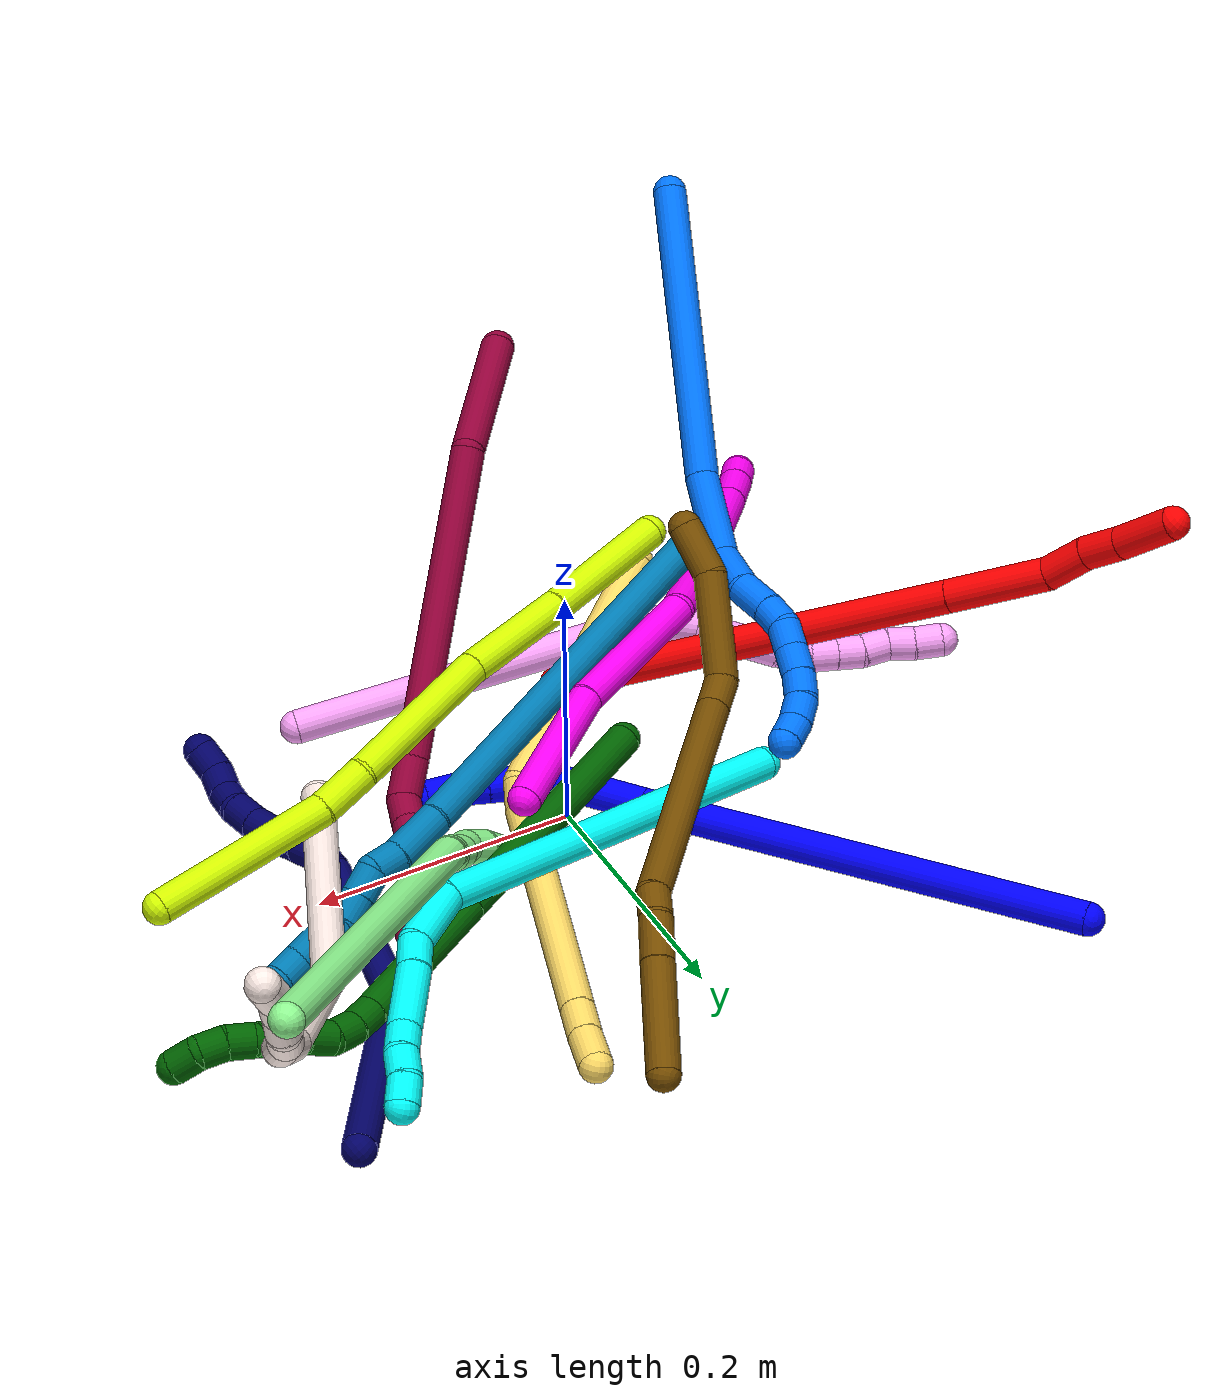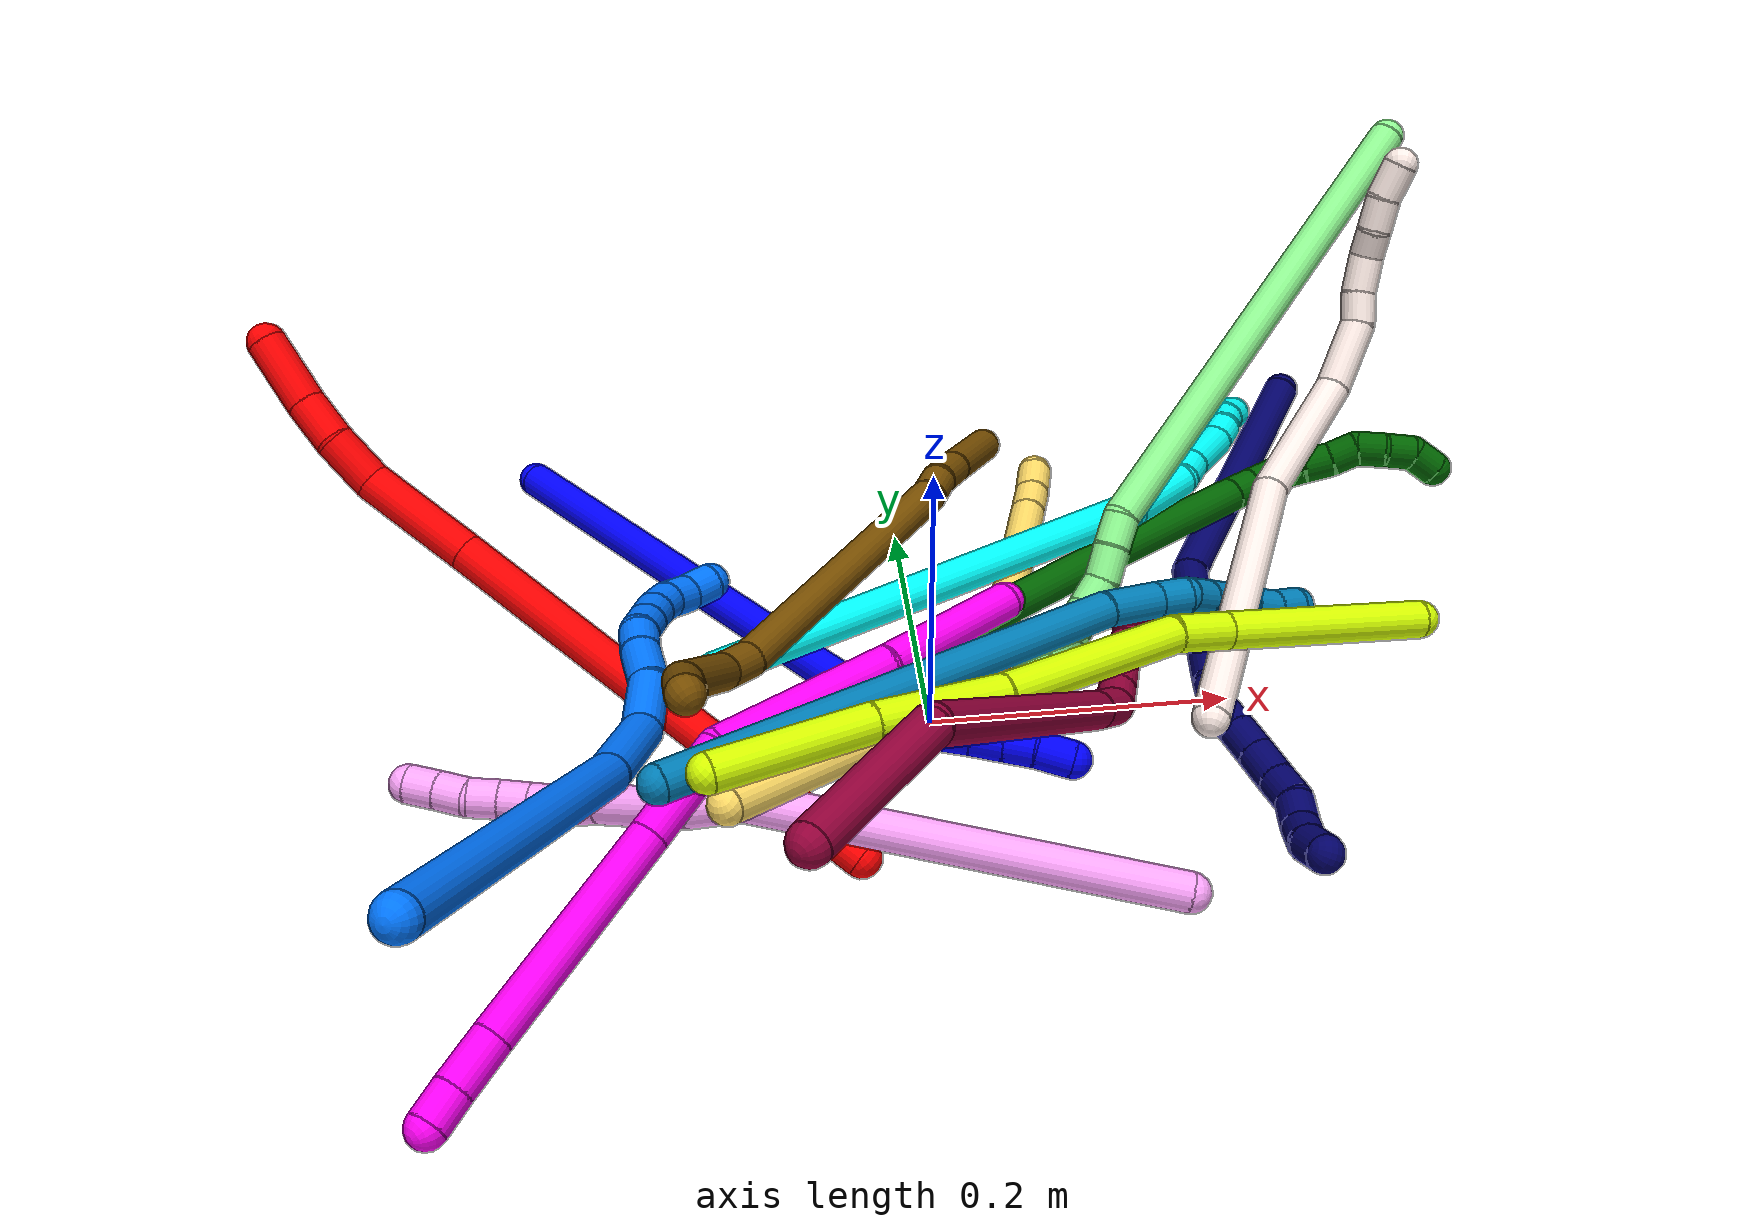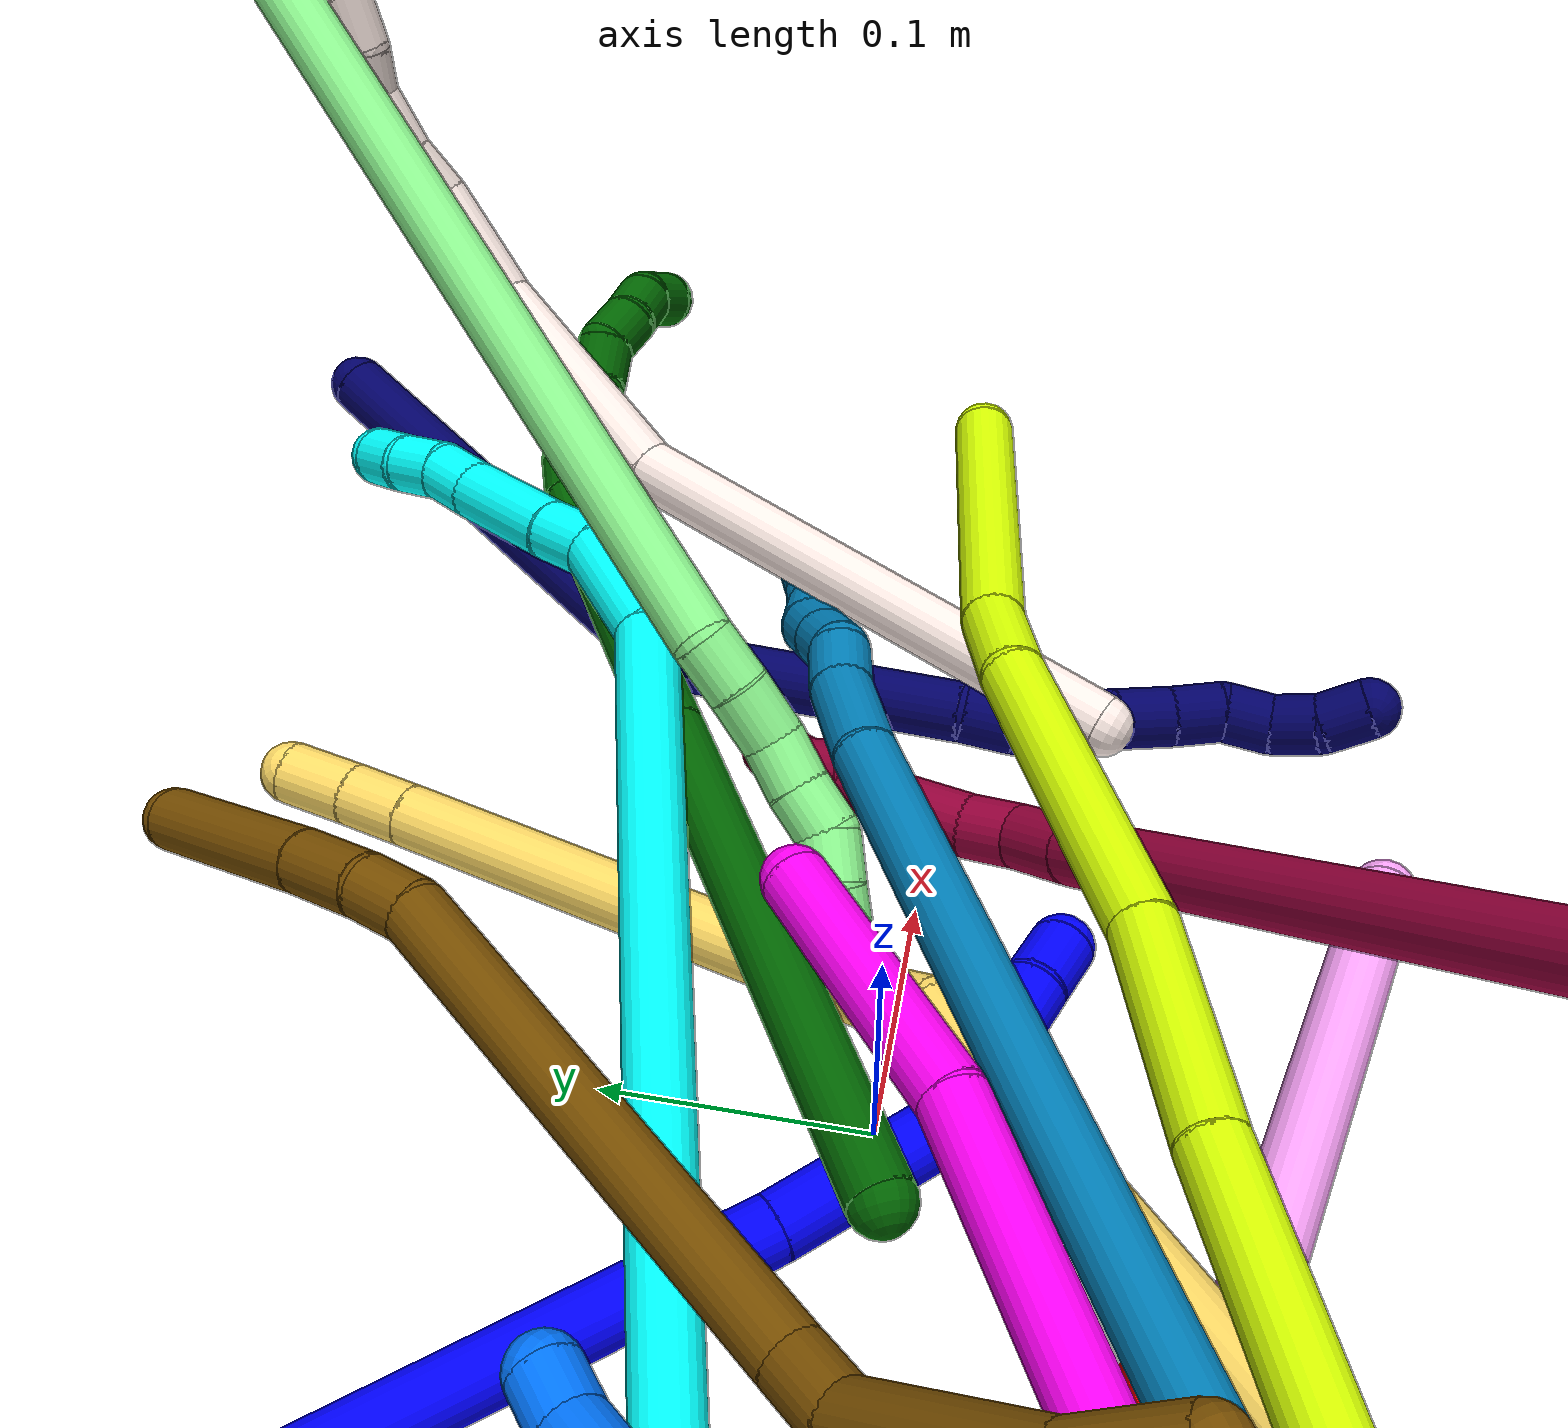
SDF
<sdf version="1.7">
 <world name="default">
  <plugin name="TubeGeneratorPlugin" filename="libtube_generator_plugin.so"/>
  <model name="photoneo_s_sensor">
   <static>1</static>
   <pose>0 0 2 1.57079 1.57079 3.14159</pose>
   <link name="link">
    <inertial><mass>0.1</mass></inertial>
    <sensor name="sensor" type="depth">
     <update_rate>30</update_rate>
     <camera>
      <horizontal_fov>1.22</horizontal_fov>
      <image><width>1920</width><height>1200</height><format>B8G8R8</format></image>
      <clip><near>0.1</near><far>4</far></clip>
      <depth_camera><output>points</output></depth_camera>
     </camera>
     <plugin name="camera_plugin" filename="libgazebo_ros_depth_camera.so">
      <baseline>0.2</baseline>
      <alwaysOn>1</alwaysOn>
      <updateRate>0.0</updateRate>
      <cameraName>camera_ir</cameraName>
      <imageTopicName>/camera/color/image_raw</imageTopicName>
      <cameraInfoTopicName>/camera/color/camera_info</cameraInfoTopicName>
      <depthImageTopicName>/camera/depth/image_raw</depthImageTopicName>
      <depthImageCameraInfoTopicName>/camera/depth/camera_info</depthImageCameraInfoTopicName>
      <pointCloudTopicName>/camera/depth/points</pointCloudTopicName>
      <frameName>fr_optical</frameName>
      <pointCloudCutoff>0.1</pointCloudCutoff>
      <pointCloudCutoffMax>2.0</pointCloudCutoffMax>
      <distortionK1>0</distortionK1>
      <distortionK2>0</distortionK2>
      <distortionK3>0</distortionK3>
      <distortionT1>0</distortionT1>
      <distortionT2>0</distortionT2>
      <CxPrime>0</CxPrime>
      <Cx>0</Cx>
      <Cy>0</Cy>
      <focalLength>0</focalLength>
      <hackBaseline>0</hackBaseline>
     </plugin>
    </sensor>
   </link>
  </model>
  <gravity>0 0 -9.8</gravity>
  <magnetic_field>6e-06 2.3e-05 -4.2e-05</magnetic_field>
  <atmosphere type="adiabatic"/>
  <physics name="default_physics" default="0" type="ode">
   <max_step_size>0.003</max_step_size>
   <real_time_factor>1</real_time_factor>
   <real_time_update_rate>1000</real_time_update_rate>
   <max_contacts>10000</max_contacts>
   <ode>
    <solver>
     <type>quick</type>
     <iters>100</iters>
     <sor>1.3</sor>
     <use_dynamic_moi_rescaling>0</use_dynamic_moi_rescaling>
    </solver>
    <constraints>
     <contact_max_correcting_vel>0</contact_max_correcting_vel>
     <contact_surface_layer>0.001</contact_surface_layer>
     <cfm>0</cfm>
     <erp>0.2</erp>
    </constraints>
   </ode>
  </physics>
  <scene><ambient>0.4 0.4 0.4 1</ambient><background>0.7 0.7 0.7 1</background><shadows>0</shadows></scene>
  <audio><device>default</device></audio>
  <spherical_coordinates>
   <surface_model>EARTH_WGS84</surface_model>
   <latitude_deg>0</latitude_deg>
   <longitude_deg>0</longitude_deg>
   <elevation>0</elevation>
   <heading_deg>0</heading_deg>
  </spherical_coordinates>
  <model name="bin">
   <static>1</static>
   <link name="bottom">
    <collision name="collision-bottom">
     <pose>0 0 -0.01 0 -0 0</pose>
     <geometry><box><size>0.8 0.6 0.02</size></box></geometry>
     <surface>
      <friction><ode><mu>100</mu><mu2>100</mu2></ode></friction>
      <contact><collide_bitmask>65535</collide_bitmask></contact>
     </surface>
    </collision>
   </link>
   <link name="west_wall">
    <collision name="collision-west_wall">
     <pose>-0.41 0 0.1 0 -0 0</pose>
     <geometry><box><size>0.02 0.6 0.2</size></box></geometry>
     <surface>
      <friction><ode><mu>100</mu><mu2>100</mu2></ode></friction>
      <contact><collide_bitmask>65535</collide_bitmask></contact>
     </surface>
    </collision>
   </link>
   <link name="east_wall">
    <collision name="collision-east_wall">
     <pose>0.41 0 0.1 0 -0 0</pose>
     <geometry><box><size>0.02 0.6 0.2</size></box></geometry>
     <surface>
      <friction><ode><mu>100</mu><mu2>100</mu2></ode></friction>
      <contact><collide_bitmask>65535</collide_bitmask></contact>
     </surface>
    </collision>
   </link>
   <link name="south_wall">
    <collision name="collision-south_wall">
     <pose>0 -0.31 0.1 0 -0 0</pose>
     <geometry><box><size>0.8 0.02 0.2</size></box></geometry>
     <surface>
      <friction><ode><mu>100</mu><mu2>100</mu2></ode></friction>
      <contact><collide_bitmask>65535</collide_bitmask></contact>
     </surface>
    </collision>
   </link>
   <link name="north_wall">
    <collision name="collision-north_wall">
     <pose>0 0.31 0.1 0 -0 0</pose>
     <geometry><box><size>0.8 0.02 0.2</size></box></geometry>
     <surface>
      <friction><ode><mu>100</mu><mu2>100</mu2></ode></friction>
      <contact><collide_bitmask>65535</collide_bitmask></contact>
     </surface>
    </collision>
   </link>
  </model>
  <model name="1">
   <static>0</static>
   <link name="1">
    <collision name="collision-cylinder-e_1_1_4">
     <pose>0.114088 -0.093492 -0.082958 2.29657 0.739822 1.42338</pose>
     <geometry><cylinder><radius>0.0125</radius><length>0.33846</length></cylinder></geometry>
     <surface>
      <friction><ode><mu>1.16</mu><mu2>1.16</mu2><slip1>0</slip1><slip2>0</slip2></ode></friction>
      <contact><ode><kp>1e+06</kp><kd>1</kd><max_vel>0</max_vel><min_depth>0.001</min_depth></ode></contact>
     </surface>
    </collision>
    <visual name="visual-cylinder-e_1_1_4">
     <pose>0.114088 -0.093492 -0.082958 2.29657 0.739822 1.42338</pose>
     <geometry><cylinder><radius>0.0125</radius><length>0.33846</length></cylinder></geometry>
     <material><ambient>0 0 1 1</ambient></material>
    </visual>
    <collision name="collision-cylinder-e_2_4_5">
     <pose>0.252128 -0.206645 -0.180238 2.20036 0.777717 1.356</pose>
     <geometry><cylinder><radius>0.0125</radius><length>0.068276</length></cylinder></geometry>
     <surface>
      <friction><ode><mu>1.16</mu><mu2>1.16</mu2><slip1>0</slip1><slip2>0</slip2></ode></friction>
      <contact><ode><kp>1e+06</kp><kd>1</kd><max_vel>0</max_vel><min_depth>0.001</min_depth></ode></contact>
     </surface>
    </collision>
    <visual name="visual-cylinder-e_2_4_5">
     <pose>0.252128 -0.206645 -0.180238 2.20036 0.777717 1.356</pose>
     <geometry><cylinder><radius>0.0125</radius><length>0.068276</length></cylinder></geometry>
     <material><ambient>0 0 1 1</ambient></material>
    </visual>
    <collision name="collision-cylinder-e_3_5_6">
     <pose>0.288882 -0.230069 -0.196656 2.07895 1.24618 1.77052</pose>
     <geometry><cylinder><radius>0.0125</radius><length>0.027013</length></cylinder></geometry>
     <surface>
      <friction><ode><mu>1.16</mu><mu2>1.16</mu2><slip1>0</slip1><slip2>0</slip2></ode></friction>
      <contact><ode><kp>1e+06</kp><kd>1</kd><max_vel>0</max_vel><min_depth>0.001</min_depth></ode></contact>
     </surface>
    </collision>
    <visual name="visual-cylinder-e_3_5_6">
     <pose>0.288882 -0.230069 -0.196656 2.07895 1.24618 1.77052</pose>
     <geometry><cylinder><radius>0.0125</radius><length>0.027013</length></cylinder></geometry>
     <material><ambient>0 0 1 1</ambient></material>
    </visual>
    <collision name="collision-cylinder-e_4_6_7">
     <pose>0.312041 -0.2364 -0.200769 2.23661 1.26547 1.97078</pose>
     <geometry><cylinder><radius>0.0125</radius><length>0.021721</length></cylinder></geometry>
     <surface>
      <friction><ode><mu>1.16</mu><mu2>1.16</mu2><slip1>0</slip1><slip2>0</slip2></ode></friction>
      <contact><ode><kp>1e+06</kp><kd>1</kd><max_vel>0</max_vel><min_depth>0.001</min_depth></ode></contact>
     </surface>
    </collision>
    <visual name="visual-cylinder-e_4_6_7">
     <pose>0.312041 -0.2364 -0.200769 2.23661 1.26547 1.97078</pose>
     <geometry><cylinder><radius>0.0125</radius><length>0.021721</length></cylinder></geometry>
     <material><ambient>0 0 1 1</ambient></material>
    </visual>
    <collision name="collision-cylinder-e_5_7_8">
     <pose>0.331968 -0.24158 -0.204646 2.18963 1.24735 1.89814</pose>
     <geometry><cylinder><radius>0.0125</radius><length>0.020184</length></cylinder></geometry>
     <surface>
      <friction><ode><mu>1.16</mu><mu2>1.16</mu2><slip1>0</slip1><slip2>0</slip2></ode></friction>
      <contact><ode><kp>1e+06</kp><kd>1</kd><max_vel>0</max_vel><min_depth>0.001</min_depth></ode></contact>
     </surface>
    </collision>
    <visual name="visual-cylinder-e_5_7_8">
     <pose>0.331968 -0.24158 -0.204646 2.18963 1.24735 1.89814</pose>
     <geometry><cylinder><radius>0.0125</radius><length>0.020184</length></cylinder></geometry>
     <material><ambient>0 0 1 1</ambient></material>
    </visual>
    <collision name="collision-cylinder-e_6_8_2">
     <pose>0.353159 -0.245519 -0.209875 2.76654 1.2688 2.63686</pose>
     <geometry><cylinder><radius>0.0125</radius><length>0.024346</length></cylinder></geometry>
     <surface>
      <friction><ode><mu>1.16</mu><mu2>1.16</mu2><slip1>0</slip1><slip2>0</slip2></ode></friction>
      <contact><ode><kp>1e+06</kp><kd>1</kd><max_vel>0</max_vel><min_depth>0.001</min_depth></ode></contact>
     </surface>
    </collision>
    <visual name="visual-cylinder-e_6_8_2">
     <pose>0.353159 -0.245519 -0.209875 2.76654 1.2688 2.63686</pose>
     <geometry><cylinder><radius>0.0125</radius><length>0.024346</length></cylinder></geometry>
     <material><ambient>0 0 1 1</ambient></material>
    </visual>
    <collision name="collision-sphere-2">
     <pose>0.364781 -0.246846 -0.213244 0 -0 0</pose>
     <geometry><sphere><radius>0.0125</radius></sphere></geometry>
     <surface>
      <friction><ode><mu>1.16</mu><mu2>1.16</mu2><slip1>0</slip1><slip2>0</slip2></ode></friction>
      <contact><ode><kp>1e+06</kp><kd>1</kd><max_vel>0</max_vel><min_depth>0.001</min_depth></ode></contact>
     </surface>
    </collision>
    <visual name="visual-sphere-2">
     <pose>0.364781 -0.246846 -0.213244 0 -0 0</pose>
     <geometry><sphere><radius>0.0125</radius></sphere></geometry>
     <material><ambient>0 0 1 1</ambient></material>
    </visual>
    <collision name="collision-sphere-4">
     <pose>0.228175 -0.186984 -0.165916 0 -0 0</pose>
     <geometry><sphere><radius>0.0125</radius></sphere></geometry>
     <surface>
      <friction><ode><mu>1.16</mu><mu2>1.16</mu2><slip1>0</slip1><slip2>0</slip2></ode></friction>
      <contact><ode><kp>1e+06</kp><kd>1</kd><max_vel>0</max_vel><min_depth>0.001</min_depth></ode></contact>
     </surface>
    </collision>
    <visual name="visual-sphere-4">
     <pose>0.228175 -0.186984 -0.165916 0 -0 0</pose>
     <geometry><sphere><radius>0.0125</radius></sphere></geometry>
     <material><ambient>0 0 1 1</ambient></material>
    </visual>
    <collision name="collision-sphere-1">
     <geometry><sphere><radius>0.0125</radius></sphere></geometry>
     <surface>
      <friction><ode><mu>1.16</mu><mu2>1.16</mu2><slip1>0</slip1><slip2>0</slip2></ode></friction>
      <contact><ode><kp>1e+06</kp><kd>1</kd><max_vel>0</max_vel><min_depth>0.001</min_depth></ode></contact>
     </surface>
    </collision>
    <visual name="visual-sphere-1">
     <geometry><sphere><radius>0.0125</radius></sphere></geometry>
     <material><ambient>0 0 1 1</ambient></material>
    </visual>
    <collision name="collision-sphere-8">
     <pose>0.341537 -0.244193 -0.206507 0 -0 0</pose>
     <geometry><sphere><radius>0.0125</radius></sphere></geometry>
     <surface>
      <friction><ode><mu>1.16</mu><mu2>1.16</mu2><slip1>0</slip1><slip2>0</slip2></ode></friction>
      <contact><ode><kp>1e+06</kp><kd>1</kd><max_vel>0</max_vel><min_depth>0.001</min_depth></ode></contact>
     </surface>
    </collision>
    <visual name="visual-sphere-8">
     <pose>0.341537 -0.244193 -0.206507 0 -0 0</pose>
     <geometry><sphere><radius>0.0125</radius></sphere></geometry>
     <material><ambient>0 0 1 1</ambient></material>
    </visual>
    <collision name="collision-sphere-5">
     <pose>0.276082 -0.226306 -0.19456 0 -0 0</pose>
     <geometry><sphere><radius>0.0125</radius></sphere></geometry>
     <surface>
      <friction><ode><mu>1.16</mu><mu2>1.16</mu2><slip1>0</slip1><slip2>0</slip2></ode></friction>
      <contact><ode><kp>1e+06</kp><kd>1</kd><max_vel>0</max_vel><min_depth>0.001</min_depth></ode></contact>
     </surface>
    </collision>
    <visual name="visual-sphere-5">
     <pose>0.276082 -0.226306 -0.19456 0 -0 0</pose>
     <geometry><sphere><radius>0.0125</radius></sphere></geometry>
     <material><ambient>0 0 1 1</ambient></material>
    </visual>
    <collision name="collision-sphere-6">
     <pose>0.301683 -0.233833 -0.198752 0 -0 0</pose>
     <geometry><sphere><radius>0.0125</radius></sphere></geometry>
     <surface>
      <friction><ode><mu>1.16</mu><mu2>1.16</mu2><slip1>0</slip1><slip2>0</slip2></ode></friction>
      <contact><ode><kp>1e+06</kp><kd>1</kd><max_vel>0</max_vel><min_depth>0.001</min_depth></ode></contact>
     </surface>
    </collision>
    <visual name="visual-sphere-6">
     <pose>0.301683 -0.233833 -0.198752 0 -0 0</pose>
     <geometry><sphere><radius>0.0125</radius></sphere></geometry>
     <material><ambient>0 0 1 1</ambient></material>
    </visual>
    <collision name="collision-sphere-7">
     <pose>0.3224 -0.238968 -0.202785 0 -0 0</pose>
     <geometry><sphere><radius>0.0125</radius></sphere></geometry>
     <surface>
      <friction><ode><mu>1.16</mu><mu2>1.16</mu2><slip1>0</slip1><slip2>0</slip2></ode></friction>
      <contact><ode><kp>1e+06</kp><kd>1</kd><max_vel>0</max_vel><min_depth>0.001</min_depth></ode></contact>
     </surface>
    </collision>
    <visual name="visual-sphere-7">
     <pose>0.3224 -0.238968 -0.202785 0 -0 0</pose>
     <geometry><sphere><radius>0.0125</radius></sphere></geometry>
     <material><ambient>0 0 1 1</ambient></material>
    </visual>
    <inertial>
     <pose>0.171416 -0.135911 -0.118595 0 -0 0</pose>
     <mass>0.5</mass>
     <inertia>
      <ixx>0.002776</ixx>
      <ixy>0</ixy>
      <ixz>0</ixz>
      <iyy>0.003695</iyy>
      <iyz>0</iyz>
      <izz>-0.000421</izz>
     </inertia>
    </inertial>
   </link>
   <pose>-0.263694 0.287398 0.011499 -0.784513 0.064266 -0.052105</pose>
  </model>
  <model name="2">
   <static>0</static>
   <link name="2">
    <collision name="collision-cylinder-e_1_1_4">
     <pose>-0.061533 0.044089 0.136308 -0.31283 -0.405687 0.064848</pose>
     <geometry><cylinder><radius>0.0125</radius><length>0.311833</length></cylinder></geometry>
     <surface>
      <friction><ode><mu>1.16</mu><mu2>1.16</mu2><slip1>0</slip1><slip2>0</slip2></ode></friction>
      <contact><ode><kp>1e+06</kp><kd>1</kd><max_vel>0</max_vel><min_depth>0.001</min_depth></ode></contact>
     </surface>
    </collision>
    <visual name="visual-cylinder-e_1_1_4">
     <pose>-0.061533 0.044089 0.136308 -0.31283 -0.405687 0.064848</pose>
     <geometry><cylinder><radius>0.0125</radius><length>0.311833</length></cylinder></geometry>
     <material><ambient>1 0 0 1</ambient></material>
    </visual>
    <collision name="collision-cylinder-e_2_4_5">
     <pose>-0.138345 0.098726 0.306045 -0.305652 -0.41107 0.064201</pose>
     <geometry><cylinder><radius>0.0125</radius><length>0.076478</length></cylinder></geometry>
     <surface>
      <friction><ode><mu>1.16</mu><mu2>1.16</mu2><slip1>0</slip1><slip2>0</slip2></ode></friction>
      <contact><ode><kp>1e+06</kp><kd>1</kd><max_vel>0</max_vel><min_depth>0.001</min_depth></ode></contact>
     </surface>
    </collision>
    <visual name="visual-cylinder-e_2_4_5">
     <pose>-0.138345 0.098726 0.306045 -0.305652 -0.41107 0.064201</pose>
     <geometry><cylinder><radius>0.0125</radius><length>0.076478</length></cylinder></geometry>
     <material><ambient>1 0 0 1</ambient></material>
    </visual>
    <collision name="collision-cylinder-e_3_5_6">
     <pose>-0.15592 0.1124 0.356253 -0.184197 -0.133643 0.012361</pose>
     <geometry><cylinder><radius>0.0125</radius><length>0.034445</length></cylinder></geometry>
     <surface>
      <friction><ode><mu>1.16</mu><mu2>1.16</mu2><slip1>0</slip1><slip2>0</slip2></ode></friction>
      <contact><ode><kp>1e+06</kp><kd>1</kd><max_vel>0</max_vel><min_depth>0.001</min_depth></ode></contact>
     </surface>
    </collision>
    <visual name="visual-cylinder-e_3_5_6">
     <pose>-0.15592 0.1124 0.356253 -0.184197 -0.133643 0.012361</pose>
     <geometry><cylinder><radius>0.0125</radius><length>0.034445</length></cylinder></geometry>
     <material><ambient>1 0 0 1</ambient></material>
    </visual>
    <collision name="collision-cylinder-e_4_6_7">
     <pose>-0.160674 0.121331 0.386768 -0.399837 -0.163487 0.033197</pose>
     <geometry><cylinder><radius>0.0125</radius><length>0.030224</length></cylinder></geometry>
     <surface>
      <friction><ode><mu>1.16</mu><mu2>1.16</mu2><slip1>0</slip1><slip2>0</slip2></ode></friction>
      <contact><ode><kp>1e+06</kp><kd>1</kd><max_vel>0</max_vel><min_depth>0.001</min_depth></ode></contact>
     </surface>
    </collision>
    <visual name="visual-cylinder-e_4_6_7">
     <pose>-0.160674 0.121331 0.386768 -0.399837 -0.163487 0.033197</pose>
     <geometry><cylinder><radius>0.0125</radius><length>0.030224</length></cylinder></geometry>
     <material><ambient>1 0 0 1</ambient></material>
    </visual>
    <collision name="collision-cylinder-e_5_7_2">
     <pose>-0.164607 0.135886 0.422274 -0.382186 -0.062694 0.012132</pose>
     <geometry><cylinder><radius>0.0125</radius><length>0.04702</length></cylinder></geometry>
     <surface>
      <friction><ode><mu>1.16</mu><mu2>1.16</mu2><slip1>0</slip1><slip2>0</slip2></ode></friction>
      <contact><ode><kp>1e+06</kp><kd>1</kd><max_vel>0</max_vel><min_depth>0.001</min_depth></ode></contact>
     </surface>
    </collision>
    <visual name="visual-cylinder-e_5_7_2">
     <pose>-0.164607 0.135886 0.422274 -0.382186 -0.062694 0.012132</pose>
     <geometry><cylinder><radius>0.0125</radius><length>0.04702</length></cylinder></geometry>
     <material><ambient>1 0 0 1</ambient></material>
    </visual>
    <collision name="collision-sphere-2">
     <pose>-0.16608 0.144637 0.444045 0 -0 0</pose>
     <geometry><sphere><radius>0.0125</radius></sphere></geometry>
     <surface>
      <friction><ode><mu>1.16</mu><mu2>1.16</mu2><slip1>0</slip1><slip2>0</slip2></ode></friction>
      <contact><ode><kp>1e+06</kp><kd>1</kd><max_vel>0</max_vel><min_depth>0.001</min_depth></ode></contact>
     </surface>
    </collision>
    <visual name="visual-sphere-2">
     <pose>-0.16608 0.144637 0.444045 0 -0 0</pose>
     <geometry><sphere><radius>0.0125</radius></sphere></geometry>
     <material><ambient>1 0 0 1</ambient></material>
    </visual>
    <collision name="collision-sphere-7">
     <pose>-0.163134 0.127135 0.400503 0 -0 0</pose>
     <geometry><sphere><radius>0.0125</radius></sphere></geometry>
     <surface>
      <friction><ode><mu>1.16</mu><mu2>1.16</mu2><slip1>0</slip1><slip2>0</slip2></ode></friction>
      <contact><ode><kp>1e+06</kp><kd>1</kd><max_vel>0</max_vel><min_depth>0.001</min_depth></ode></contact>
     </surface>
    </collision>
    <visual name="visual-sphere-7">
     <pose>-0.163134 0.127135 0.400503 0 -0 0</pose>
     <geometry><sphere><radius>0.0125</radius></sphere></geometry>
     <material><ambient>1 0 0 1</ambient></material>
    </visual>
    <collision name="collision-sphere-6">
     <pose>-0.158214 0.115527 0.373033 0 -0 0</pose>
     <geometry><sphere><radius>0.0125</radius></sphere></geometry>
     <surface>
      <friction><ode><mu>1.16</mu><mu2>1.16</mu2><slip1>0</slip1><slip2>0</slip2></ode></friction>
      <contact><ode><kp>1e+06</kp><kd>1</kd><max_vel>0</max_vel><min_depth>0.001</min_depth></ode></contact>
     </surface>
    </collision>
    <visual name="visual-sphere-6">
     <pose>-0.158214 0.115527 0.373033 0 -0 0</pose>
     <geometry><sphere><radius>0.0125</radius></sphere></geometry>
     <material><ambient>1 0 0 1</ambient></material>
    </visual>
    <collision name="collision-sphere-5">
     <pose>-0.153625 0.109274 0.339473 0 -0 0</pose>
     <geometry><sphere><radius>0.0125</radius></sphere></geometry>
     <surface>
      <friction><ode><mu>1.16</mu><mu2>1.16</mu2><slip1>0</slip1><slip2>0</slip2></ode></friction>
      <contact><ode><kp>1e+06</kp><kd>1</kd><max_vel>0</max_vel><min_depth>0.001</min_depth></ode></contact>
     </surface>
    </collision>
    <visual name="visual-sphere-5">
     <pose>-0.153625 0.109274 0.339473 0 -0 0</pose>
     <geometry><sphere><radius>0.0125</radius></sphere></geometry>
     <material><ambient>1 0 0 1</ambient></material>
    </visual>
    <collision name="collision-sphere-1">
     <geometry><sphere><radius>0.0125</radius></sphere></geometry>
     <surface>
      <friction><ode><mu>1.16</mu><mu2>1.16</mu2><slip1>0</slip1><slip2>0</slip2></ode></friction>
      <contact><ode><kp>1e+06</kp><kd>1</kd><max_vel>0</max_vel><min_depth>0.001</min_depth></ode></contact>
     </surface>
    </collision>
    <visual name="visual-sphere-1">
     <geometry><sphere><radius>0.0125</radius></sphere></geometry>
     <material><ambient>1 0 0 1</ambient></material>
    </visual>
    <collision name="collision-sphere-4">
     <pose>-0.123065 0.088178 0.272616 0 -0 0</pose>
     <geometry><sphere><radius>0.0125</radius></sphere></geometry>
     <surface>
      <friction><ode><mu>1.16</mu><mu2>1.16</mu2><slip1>0</slip1><slip2>0</slip2></ode></friction>
      <contact><ode><kp>1e+06</kp><kd>1</kd><max_vel>0</max_vel><min_depth>0.001</min_depth></ode></contact>
     </surface>
    </collision>
    <visual name="visual-sphere-4">
     <pose>-0.123065 0.088178 0.272616 0 -0 0</pose>
     <geometry><sphere><radius>0.0125</radius></sphere></geometry>
     <material><ambient>1 0 0 1</ambient></material>
    </visual>
    <inertial>
     <pose>-0.09547 0.070454 0.219454 0 -0 0</pose>
     <mass>0.5</mass>
     <inertia>
      <ixx>0.002524</ixx>
      <ixy>0</ixy>
      <ixz>0</ixz>
      <iyy>0.002652</iyy>
      <iyz>0</iyz>
      <izz>0.000319</izz>
     </inertia>
    </inertial>
   </link>
   <pose>-0.057539 -0.125732 0.012359 -0.183463 -0.686213 -0.162023</pose>
  </model>
  <model name="3">
   <static>0</static>
   <link name="3">
    <collision name="collision-cylinder-e_1_1_4">
     <pose>0.04212 0.051383 0.139013 -0.354053 0.276902 -0.049846</pose>
     <geometry><cylinder><radius>0.0125</radius><length>0.308149</length></cylinder></geometry>
     <surface>
      <friction><ode><mu>1.16</mu><mu2>1.16</mu2><slip1>0</slip1><slip2>0</slip2></ode></friction>
      <contact><ode><kp>1e+06</kp><kd>1</kd><max_vel>0</max_vel><min_depth>0.001</min_depth></ode></contact>
     </surface>
    </collision>
    <visual name="visual-cylinder-e_1_1_4">
     <pose>0.04212 0.051383 0.139013 -0.354053 0.276902 -0.049846</pose>
     <geometry><cylinder><radius>0.0125</radius><length>0.308149</length></cylinder></geometry>
     <material><ambient>0.003922 1 0.996078 1</ambient></material>
    </visual>
    <collision name="collision-cylinder-e_2_4_5">
     <pose>0.095476 0.119567 0.294439 -0.797081 0.446173 -0.190474</pose>
     <geometry><cylinder><radius>0.0125</radius><length>0.052073</length></cylinder></geometry>
     <surface>
      <friction><ode><mu>1.16</mu><mu2>1.16</mu2><slip1>0</slip1><slip2>0</slip2></ode></friction>
      <contact><ode><kp>1e+06</kp><kd>1</kd><max_vel>0</max_vel><min_depth>0.001</min_depth></ode></contact>
     </surface>
    </collision>
    <visual name="visual-cylinder-e_2_4_5">
     <pose>0.095476 0.119567 0.294439 -0.797081 0.446173 -0.190474</pose>
     <geometry><cylinder><radius>0.0125</radius><length>0.052073</length></cylinder></geometry>
     <material><ambient>0.003922 1 0.996078 1</ambient></material>
    </visual>
    <collision name="collision-cylinder-e_3_5_6">
     <pose>0.112523 0.146691 0.314008 -1.27408 0.493937 -0.368867</pose>
     <geometry><cylinder><radius>0.0125</radius><length>0.02452</length></cylinder></geometry>
     <surface>
      <friction><ode><mu>1.16</mu><mu2>1.16</mu2><slip1>0</slip1><slip2>0</slip2></ode></friction>
      <contact><ode><kp>1e+06</kp><kd>1</kd><max_vel>0</max_vel><min_depth>0.001</min_depth></ode></contact>
     </surface>
    </collision>
    <visual name="visual-cylinder-e_3_5_6">
     <pose>0.112523 0.146691 0.314008 -1.27408 0.493937 -0.368867</pose>
     <geometry><cylinder><radius>0.0125</radius><length>0.02452</length></cylinder></geometry>
     <material><ambient>0.003922 1 0.996078 1</ambient></material>
    </visual>
    <collision name="collision-cylinder-e_4_6_7">
     <pose>0.131991 0.177261 0.325444 -1.18259 0.558041 -0.380082</pose>
     <geometry><cylinder><radius>0.0125</radius><length>0.051574</length></cylinder></geometry>
     <surface>
      <friction><ode><mu>1.16</mu><mu2>1.16</mu2><slip1>0</slip1><slip2>0</slip2></ode></friction>
      <contact><ode><kp>1e+06</kp><kd>1</kd><max_vel>0</max_vel><min_depth>0.001</min_depth></ode></contact>
     </surface>
    </collision>
    <visual name="visual-cylinder-e_4_6_7">
     <pose>0.131991 0.177261 0.325444 -1.18259 0.558041 -0.380082</pose>
     <geometry><cylinder><radius>0.0125</radius><length>0.051574</length></cylinder></geometry>
     <material><ambient>0.003922 1 0.996078 1</ambient></material>
    </visual>
    <collision name="collision-cylinder-e_5_7_8">
     <pose>0.149909 0.206701 0.337307 -1.19912 0.407884 -0.280856</pose>
     <geometry><cylinder><radius>0.0125</radius><length>0.021496</length></cylinder></geometry>
     <surface>
      <friction><ode><mu>1.16</mu><mu2>1.16</mu2><slip1>0</slip1><slip2>0</slip2></ode></friction>
      <contact><ode><kp>1e+06</kp><kd>1</kd><max_vel>0</max_vel><min_depth>0.001</min_depth></ode></contact>
     </surface>
    </collision>
    <visual name="visual-cylinder-e_5_7_8">
     <pose>0.149909 0.206701 0.337307 -1.19912 0.407884 -0.280856</pose>
     <geometry><cylinder><radius>0.0125</radius><length>0.021496</length></cylinder></geometry>
     <material><ambient>0.003922 1 0.996078 1</ambient></material>
    </visual>
    <collision name="collision-cylinder-e_6_8_9">
     <pose>0.159177 0.224988 0.341814 -1.46964 0.500893 -0.454351</pose>
     <geometry><cylinder><radius>0.0125</radius><length>0.020843</length></cylinder></geometry>
     <surface>
      <friction><ode><mu>1.16</mu><mu2>1.16</mu2><slip1>0</slip1><slip2>0</slip2></ode></friction>
      <contact><ode><kp>1e+06</kp><kd>1</kd><max_vel>0</max_vel><min_depth>0.001</min_depth></ode></contact>
     </surface>
    </collision>
    <visual name="visual-cylinder-e_6_8_9">
     <pose>0.159177 0.224988 0.341814 -1.46964 0.500893 -0.454351</pose>
     <geometry><cylinder><radius>0.0125</radius><length>0.020843</length></cylinder></geometry>
     <material><ambient>0.003922 1 0.996078 1</ambient></material>
    </visual>
    <collision name="collision-cylinder-e_7_9_2">
     <pose>0.171126 0.241853 0.345041 -1.28249 0.708433 -0.538704</pose>
     <geometry><cylinder><radius>0.0125</radius><length>0.021346</length></cylinder></geometry>
     <surface>
      <friction><ode><mu>1.16</mu><mu2>1.16</mu2><slip1>0</slip1><slip2>0</slip2></ode></friction>
      <contact><ode><kp>1e+06</kp><kd>1</kd><max_vel>0</max_vel><min_depth>0.001</min_depth></ode></contact>
     </surface>
    </collision>
    <visual name="visual-cylinder-e_7_9_2">
     <pose>0.171126 0.241853 0.345041 -1.28249 0.708433 -0.538704</pose>
     <geometry><cylinder><radius>0.0125</radius><length>0.021346</length></cylinder></geometry>
     <material><ambient>0.003922 1 0.996078 1</ambient></material>
    </visual>
    <collision name="collision-sphere-2">
     <pose>0.17807 0.249623 0.347345 0 -0 0</pose>
     <geometry><sphere><radius>0.0125</radius></sphere></geometry>
     <surface>
      <friction><ode><mu>1.16</mu><mu2>1.16</mu2><slip1>0</slip1><slip2>0</slip2></ode></friction>
      <contact><ode><kp>1e+06</kp><kd>1</kd><max_vel>0</max_vel><min_depth>0.001</min_depth></ode></contact>
     </surface>
    </collision>
    <visual name="visual-sphere-2">
     <pose>0.17807 0.249623 0.347345 0 -0 0</pose>
     <geometry><sphere><radius>0.0125</radius></sphere></geometry>
     <material><ambient>0.003922 1 0.996078 1</ambient></material>
    </visual>
    <collision name="collision-sphere-9">
     <pose>0.164181 0.234083 0.342737 0 -0 0</pose>
     <geometry><sphere><radius>0.0125</radius></sphere></geometry>
     <surface>
      <friction><ode><mu>1.16</mu><mu2>1.16</mu2><slip1>0</slip1><slip2>0</slip2></ode></friction>
      <contact><ode><kp>1e+06</kp><kd>1</kd><max_vel>0</max_vel><min_depth>0.001</min_depth></ode></contact>
     </surface>
    </collision>
    <visual name="visual-sphere-9">
     <pose>0.164181 0.234083 0.342737 0 -0 0</pose>
     <geometry><sphere><radius>0.0125</radius></sphere></geometry>
     <material><ambient>0.003922 1 0.996078 1</ambient></material>
    </visual>
    <collision name="collision-sphere-4">
     <pose>0.084241 0.102766 0.278026 0 -0 0</pose>
     <geometry><sphere><radius>0.0125</radius></sphere></geometry>
     <surface>
      <friction><ode><mu>1.16</mu><mu2>1.16</mu2><slip1>0</slip1><slip2>0</slip2></ode></friction>
      <contact><ode><kp>1e+06</kp><kd>1</kd><max_vel>0</max_vel><min_depth>0.001</min_depth></ode></contact>
     </surface>
    </collision>
    <visual name="visual-sphere-4">
     <pose>0.084241 0.102766 0.278026 0 -0 0</pose>
     <geometry><sphere><radius>0.0125</radius></sphere></geometry>
     <material><ambient>0.003922 1 0.996078 1</ambient></material>
    </visual>
    <collision name="collision-sphere-1">
     <geometry><sphere><radius>0.0125</radius></sphere></geometry>
     <surface>
      <friction><ode><mu>1.16</mu><mu2>1.16</mu2><slip1>0</slip1><slip2>0</slip2></ode></friction>
      <contact><ode><kp>1e+06</kp><kd>1</kd><max_vel>0</max_vel><min_depth>0.001</min_depth></ode></contact>
     </surface>
    </collision>
    <visual name="visual-sphere-1">
     <geometry><sphere><radius>0.0125</radius></sphere></geometry>
     <material><ambient>0.003922 1 0.996078 1</ambient></material>
    </visual>
    <collision name="collision-sphere-8">
     <pose>0.154172 0.215893 0.34089 0 -0 0</pose>
     <geometry><sphere><radius>0.0125</radius></sphere></geometry>
     <surface>
      <friction><ode><mu>1.16</mu><mu2>1.16</mu2><slip1>0</slip1><slip2>0</slip2></ode></friction>
      <contact><ode><kp>1e+06</kp><kd>1</kd><max_vel>0</max_vel><min_depth>0.001</min_depth></ode></contact>
     </surface>
    </collision>
    <visual name="visual-sphere-8">
     <pose>0.154172 0.215893 0.34089 0 -0 0</pose>
     <geometry><sphere><radius>0.0125</radius></sphere></geometry>
     <material><ambient>0.003922 1 0.996078 1</ambient></material>
    </visual>
    <collision name="collision-sphere-5">
     <pose>0.106711 0.136368 0.310851 0 -0 0</pose>
     <geometry><sphere><radius>0.0125</radius></sphere></geometry>
     <surface>
      <friction><ode><mu>1.16</mu><mu2>1.16</mu2><slip1>0</slip1><slip2>0</slip2></ode></friction>
      <contact><ode><kp>1e+06</kp><kd>1</kd><max_vel>0</max_vel><min_depth>0.001</min_depth></ode></contact>
     </surface>
    </collision>
    <visual name="visual-sphere-5">
     <pose>0.106711 0.136368 0.310851 0 -0 0</pose>
     <geometry><sphere><radius>0.0125</radius></sphere></geometry>
     <material><ambient>0.003922 1 0.996078 1</ambient></material>
    </visual>
    <collision name="collision-sphere-6">
     <pose>0.118336 0.157014 0.317164 0 -0 0</pose>
     <geometry><sphere><radius>0.0125</radius></sphere></geometry>
     <surface>
      <friction><ode><mu>1.16</mu><mu2>1.16</mu2><slip1>0</slip1><slip2>0</slip2></ode></friction>
      <contact><ode><kp>1e+06</kp><kd>1</kd><max_vel>0</max_vel><min_depth>0.001</min_depth></ode></contact>
     </surface>
    </collision>
    <visual name="visual-sphere-6">
     <pose>0.118336 0.157014 0.317164 0 -0 0</pose>
     <geometry><sphere><radius>0.0125</radius></sphere></geometry>
     <material><ambient>0.003922 1 0.996078 1</ambient></material>
    </visual>
    <collision name="collision-sphere-7">
     <pose>0.145645 0.197508 0.333724 0 -0 0</pose>
     <geometry><sphere><radius>0.0125</radius></sphere></geometry>
     <surface>
      <friction><ode><mu>1.16</mu><mu2>1.16</mu2><slip1>0</slip1><slip2>0</slip2></ode></friction>
      <contact><ode><kp>1e+06</kp><kd>1</kd><max_vel>0</max_vel><min_depth>0.001</min_depth></ode></contact>
     </surface>
    </collision>
    <visual name="visual-sphere-7">
     <pose>0.145645 0.197508 0.333724 0 -0 0</pose>
     <geometry><sphere><radius>0.0125</radius></sphere></geometry>
     <material><ambient>0.003922 1 0.996078 1</ambient></material>
    </visual>
    <inertial>
     <pose>0.075421 0.098188 0.208786 0 -0 0</pose>
     <mass>0.5</mass>
     <inertia>
      <ixx>0.00227</ixx>
      <ixy>0</ixy>
      <ixz>0</ixz>
      <iyy>0.002221</iyy>
      <iyz>0</iyz>
      <izz>-0.001502</izz>
     </inertia>
    </inertial>
   </link>
   <pose>-0.139433 0.040398 0.024068 0.456976 1.11862 0.348157</pose>
  </model>
  <model name="4">
   <static>0</static>
   <link name="4">
    <collision name="collision-cylinder-e_1_1_4">
     <pose>-0.117543 -0.013818 0.064997 0.209475 -1.05626 -0.122506</pose>
     <geometry><cylinder><radius>0.0125</radius><length>0.270052</length></cylinder></geometry>
     <surface>
      <friction><ode><mu>1.16</mu><mu2>1.16</mu2><slip1>0</slip1><slip2>0</slip2></ode></friction>
      <contact><ode><kp>1e+06</kp><kd>1</kd><max_vel>0</max_vel><min_depth>0.001</min_depth></ode></contact>
     </surface>
    </collision>
    <visual name="visual-cylinder-e_1_1_4">
     <pose>-0.117543 -0.013818 0.064997 0.209475 -1.05626 -0.122506</pose>
     <geometry><cylinder><radius>0.0125</radius><length>0.270052</length></cylinder></geometry>
     <material><ambient>1 0.65098 0.996078 1</ambient></material>
    </visual>
    <collision name="collision-cylinder-e_2_4_5">
     <pose>-0.249394 -0.021034 0.139409 -0.611579 -0.893828 0.300315</pose>
     <geometry><cylinder><radius>0.0125</radius><length>0.036711</length></cylinder></geometry>
     <surface>
      <friction><ode><mu>1.16</mu><mu2>1.16</mu2><slip1>0</slip1><slip2>0</slip2></ode></friction>
      <contact><ode><kp>1e+06</kp><kd>1</kd><max_vel>0</max_vel><min_depth>0.001</min_depth></ode></contact>
     </surface>
    </collision>
    <visual name="visual-cylinder-e_2_4_5">
     <pose>-0.249394 -0.021034 0.139409 -0.611579 -0.893828 0.300315</pose>
     <geometry><cylinder><radius>0.0125</radius><length>0.036711</length></cylinder></geometry>
     <material><ambient>1 0.65098 0.996078 1</ambient></material>
    </visual>
    <collision name="collision-cylinder-e_3_5_6">
     <pose>-0.283754 -0.003081 0.171877 -0.457534 -0.662639 0.159855</pose>
     <geometry><cylinder><radius>0.0125</radius><length>0.06519</length></cylinder></geometry>
     <surface>
      <friction><ode><mu>1.16</mu><mu2>1.16</mu2><slip1>0</slip1><slip2>0</slip2></ode></friction>
      <contact><ode><kp>1e+06</kp><kd>1</kd><max_vel>0</max_vel><min_depth>0.001</min_depth></ode></contact>
     </surface>
    </collision>
    <visual name="visual-cylinder-e_3_5_6">
     <pose>-0.283754 -0.003081 0.171877 -0.457534 -0.662639 0.159855</pose>
     <geometry><cylinder><radius>0.0125</radius><length>0.06519</length></cylinder></geometry>
     <material><ambient>1 0.65098 0.996078 1</ambient></material>
    </visual>
    <collision name="collision-cylinder-e_4_6_7">
     <pose>-0.313134 0.01252 0.202619 -0.504888 -0.815385 0.221894</pose>
     <geometry><cylinder><radius>0.0125</radius><length>0.025627</length></cylinder></geometry>
     <surface>
      <friction><ode><mu>1.16</mu><mu2>1.16</mu2><slip1>0</slip1><slip2>0</slip2></ode></friction>
      <contact><ode><kp>1e+06</kp><kd>1</kd><max_vel>0</max_vel><min_depth>0.001</min_depth></ode></contact>
     </surface>
    </collision>
    <visual name="visual-cylinder-e_4_6_7">
     <pose>-0.313134 0.01252 0.202619 -0.504888 -0.815385 0.221894</pose>
     <geometry><cylinder><radius>0.0125</radius><length>0.025627</length></cylinder></geometry>
     <material><ambient>1 0.65098 0.996078 1</ambient></material>
    </visual>
    <collision name="collision-cylinder-e_5_7_8">
     <pose>-0.331106 0.017872 0.21609 -0.188429 -0.972932 0.099865</pose>
     <geometry><cylinder><radius>0.0125</radius><length>0.020915</length></cylinder></geometry>
     <surface>
      <friction><ode><mu>1.16</mu><mu2>1.16</mu2><slip1>0</slip1><slip2>0</slip2></ode></friction>
      <contact><ode><kp>1e+06</kp><kd>1</kd><max_vel>0</max_vel><min_depth>0.001</min_depth></ode></contact>
     </surface>
    </collision>
    <visual name="visual-cylinder-e_5_7_8">
     <pose>-0.331106 0.017872 0.21609 -0.188429 -0.972932 0.099865</pose>
     <geometry><cylinder><radius>0.0125</radius><length>0.020915</length></cylinder></geometry>
     <material><ambient>1 0.65098 0.996078 1</ambient></material>
    </visual>
    <collision name="collision-cylinder-e_6_8_9">
     <pose>-0.348093 0.020046 0.227468 -0.189218 -0.971684 0.100133</pose>
     <geometry><cylinder><radius>0.0125</radius><length>0.020208</length></cylinder></geometry>
     <surface>
      <friction><ode><mu>1.16</mu><mu2>1.16</mu2><slip1>0</slip1><slip2>0</slip2></ode></friction>
      <contact><ode><kp>1e+06</kp><kd>1</kd><max_vel>0</max_vel><min_depth>0.001</min_depth></ode></contact>
     </surface>
    </collision>
    <visual name="visual-cylinder-e_6_8_9">
     <pose>-0.348093 0.020046 0.227468 -0.189218 -0.971684 0.100133</pose>
     <geometry><cylinder><radius>0.0125</radius><length>0.020208</length></cylinder></geometry>
     <material><ambient>1 0.65098 0.996078 1</ambient></material>
    </visual>
    <collision name="collision-cylinder-e_7_9_10">
     <pose>-0.365698 0.021167 0.237125 -0.012321 -1.15748 0.00805</pose>
     <geometry><cylinder><radius>0.0125</radius><length>0.020223</length></cylinder></geometry>
     <surface>
      <friction><ode><mu>1.16</mu><mu2>1.16</mu2><slip1>0</slip1><slip2>0</slip2></ode></friction>
      <contact><ode><kp>1e+06</kp><kd>1</kd><max_vel>0</max_vel><min_depth>0.001</min_depth></ode></contact>
     </surface>
    </collision>
    <visual name="visual-cylinder-e_7_9_10">
     <pose>-0.365698 0.021167 0.237125 -0.012321 -1.15748 0.00805</pose>
     <geometry><cylinder><radius>0.0125</radius><length>0.020223</length></cylinder></geometry>
     <material><ambient>1 0.65098 0.996078 1</ambient></material>
    </visual>
    <collision name="collision-cylinder-e_8_10_11">
     <pose>-0.382585 0.021815 0.247991 -0.087632 -0.840372 0.039174</pose>
     <geometry><cylinder><radius>0.0125</radius><length>0.020478</length></cylinder></geometry>
     <surface>
      <friction><ode><mu>1.16</mu><mu2>1.16</mu2><slip1>0</slip1><slip2>0</slip2></ode></friction>
      <contact><ode><kp>1e+06</kp><kd>1</kd><max_vel>0</max_vel><min_depth>0.001</min_depth></ode></contact>
     </surface>
    </collision>
    <visual name="visual-cylinder-e_8_10_11">
     <pose>-0.382585 0.021815 0.247991 -0.087632 -0.840372 0.039174</pose>
     <geometry><cylinder><radius>0.0125</radius><length>0.020478</length></cylinder></geometry>
     <material><ambient>1 0.65098 0.996078 1</ambient></material>
    </visual>
    <collision name="collision-cylinder-e_9_11_2">
     <pose>-0.398524 0.022346 0.260875 0.01108 -0.939375 -0.005624</pose>
     <geometry><cylinder><radius>0.0125</radius><length>0.020597</length></cylinder></geometry>
     <surface>
      <friction><ode><mu>1.16</mu><mu2>1.16</mu2><slip1>0</slip1><slip2>0</slip2></ode></friction>
      <contact><ode><kp>1e+06</kp><kd>1</kd><max_vel>0</max_vel><min_depth>0.001</min_depth></ode></contact>
     </surface>
    </collision>
    <visual name="visual-cylinder-e_9_11_2">
     <pose>-0.398524 0.022346 0.260875 0.01108 -0.939375 -0.005624</pose>
     <geometry><cylinder><radius>0.0125</radius><length>0.020597</length></cylinder></geometry>
     <material><ambient>1 0.65098 0.996078 1</ambient></material>
    </visual>
    <collision name="collision-sphere-2">
     <pose>-0.406837 0.022279 0.266954 0 -0 0</pose>
     <geometry><sphere><radius>0.0125</radius></sphere></geometry>
     <surface>
      <friction><ode><mu>1.16</mu><mu2>1.16</mu2><slip1>0</slip1><slip2>0</slip2></ode></friction>
      <contact><ode><kp>1e+06</kp><kd>1</kd><max_vel>0</max_vel><min_depth>0.001</min_depth></ode></contact>
     </surface>
    </collision>
    <visual name="visual-sphere-2">
     <pose>-0.406837 0.022279 0.266954 0 -0 0</pose>
     <geometry><sphere><radius>0.0125</radius></sphere></geometry>
     <material><ambient>1 0.65098 0.996078 1</ambient></material>
    </visual>
    <collision name="collision-sphere-11">
     <pose>-0.390212 0.022413 0.254796 0 -0 0</pose>
     <geometry><sphere><radius>0.0125</radius></sphere></geometry>
     <surface>
      <friction><ode><mu>1.16</mu><mu2>1.16</mu2><slip1>0</slip1><slip2>0</slip2></ode></friction>
      <contact><ode><kp>1e+06</kp><kd>1</kd><max_vel>0</max_vel><min_depth>0.001</min_depth></ode></contact>
     </surface>
    </collision>
    <visual name="visual-sphere-11">
     <pose>-0.390212 0.022413 0.254796 0 -0 0</pose>
     <geometry><sphere><radius>0.0125</radius></sphere></geometry>
     <material><ambient>1 0.65098 0.996078 1</ambient></material>
    </visual>
    <collision name="collision-sphere-10">
     <pose>-0.374958 0.021218 0.241186 0 -0 0</pose>
     <geometry><sphere><radius>0.0125</radius></sphere></geometry>
     <surface>
      <friction><ode><mu>1.16</mu><mu2>1.16</mu2><slip1>0</slip1><slip2>0</slip2></ode></friction>
      <contact><ode><kp>1e+06</kp><kd>1</kd><max_vel>0</max_vel><min_depth>0.001</min_depth></ode></contact>
     </surface>
    </collision>
    <visual name="visual-sphere-10">
     <pose>-0.374958 0.021218 0.241186 0 -0 0</pose>
     <geometry><sphere><radius>0.0125</radius></sphere></geometry>
     <material><ambient>1 0.65098 0.996078 1</ambient></material>
    </visual>
    <collision name="collision-sphere-9">
     <pose>-0.356437 0.021117 0.233064 0 -0 0</pose>
     <geometry><sphere><radius>0.0125</radius></sphere></geometry>
     <surface>
      <friction><ode><mu>1.16</mu><mu2>1.16</mu2><slip1>0</slip1><slip2>0</slip2></ode></friction>
      <contact><ode><kp>1e+06</kp><kd>1</kd><max_vel>0</max_vel><min_depth>0.001</min_depth></ode></contact>
     </surface>
    </collision>
    <visual name="visual-sphere-9">
     <pose>-0.356437 0.021117 0.233064 0 -0 0</pose>
     <geometry><sphere><radius>0.0125</radius></sphere></geometry>
     <material><ambient>1 0.65098 0.996078 1</ambient></material>
    </visual>
    <collision name="collision-sphere-4">
     <pose>-0.235086 -0.027636 0.129995 0 -0 0</pose>
     <geometry><sphere><radius>0.0125</radius></sphere></geometry>
     <surface>
      <friction><ode><mu>1.16</mu><mu2>1.16</mu2><slip1>0</slip1><slip2>0</slip2></ode></friction>
      <contact><ode><kp>1e+06</kp><kd>1</kd><max_vel>0</max_vel><min_depth>0.001</min_depth></ode></contact>
     </surface>
    </collision>
    <visual name="visual-sphere-4">
     <pose>-0.235086 -0.027636 0.129995 0 -0 0</pose>
     <geometry><sphere><radius>0.0125</radius></sphere></geometry>
     <material><ambient>1 0.65098 0.996078 1</ambient></material>
    </visual>
    <collision name="collision-sphere-1">
     <geometry><sphere><radius>0.0125</radius></sphere></geometry>
     <surface>
      <friction><ode><mu>1.16</mu><mu2>1.16</mu2><slip1>0</slip1><slip2>0</slip2></ode></friction>
      <contact><ode><kp>1e+06</kp><kd>1</kd><max_vel>0</max_vel><min_depth>0.001</min_depth></ode></contact>
     </surface>
    </collision>
    <visual name="visual-sphere-1">
     <geometry><sphere><radius>0.0125</radius></sphere></geometry>
     <material><ambient>1 0.65098 0.996078 1</ambient></material>
    </visual>
    <collision name="collision-sphere-8">
     <pose>-0.339749 0.018974 0.221872 0 -0 0</pose>
     <geometry><sphere><radius>0.0125</radius></sphere></geometry>
     <surface>
      <friction><ode><mu>1.16</mu><mu2>1.16</mu2><slip1>0</slip1><slip2>0</slip2></ode></friction>
      <contact><ode><kp>1e+06</kp><kd>1</kd><max_vel>0</max_vel><min_depth>0.001</min_depth></ode></contact>
     </surface>
    </collision>
    <visual name="visual-sphere-8">
     <pose>-0.339749 0.018974 0.221872 0 -0 0</pose>
     <geometry><sphere><radius>0.0125</radius></sphere></geometry>
     <material><ambient>1 0.65098 0.996078 1</ambient></material>
    </visual>
    <collision name="collision-sphere-5">
     <pose>-0.263701 -0.014432 0.148823 0 -0 0</pose>
     <geometry><sphere><radius>0.0125</radius></sphere></geometry>
     <surface>
      <friction><ode><mu>1.16</mu><mu2>1.16</mu2><slip1>0</slip1><slip2>0</slip2></ode></friction>
      <contact><ode><kp>1e+06</kp><kd>1</kd><max_vel>0</max_vel><min_depth>0.001</min_depth></ode></contact>
     </surface>
    </collision>
    <visual name="visual-sphere-5">
     <pose>-0.263701 -0.014432 0.148823 0 -0 0</pose>
     <geometry><sphere><radius>0.0125</radius></sphere></geometry>
     <material><ambient>1 0.65098 0.996078 1</ambient></material>
    </visual>
    <collision name="collision-sphere-6">
     <pose>-0.303806 0.00827 0.194931 0 -0 0</pose>
     <geometry><sphere><radius>0.0125</radius></sphere></geometry>
     <surface>
      <friction><ode><mu>1.16</mu><mu2>1.16</mu2><slip1>0</slip1><slip2>0</slip2></ode></friction>
      <contact><ode><kp>1e+06</kp><kd>1</kd><max_vel>0</max_vel><min_depth>0.001</min_depth></ode></contact>
     </surface>
    </collision>
    <visual name="visual-sphere-6">
     <pose>-0.303806 0.00827 0.194931 0 -0 0</pose>
     <geometry><sphere><radius>0.0125</radius></sphere></geometry>
     <material><ambient>1 0.65098 0.996078 1</ambient></material>
    </visual>
    <collision name="collision-sphere-7">
     <pose>-0.322462 0.016769 0.210308 0 -0 0</pose>
     <geometry><sphere><radius>0.0125</radius></sphere></geometry>
     <surface>
      <friction><ode><mu>1.16</mu><mu2>1.16</mu2><slip1>0</slip1><slip2>0</slip2></ode></friction>
      <contact><ode><kp>1e+06</kp><kd>1</kd><max_vel>0</max_vel><min_depth>0.001</min_depth></ode></contact>
     </surface>
    </collision>
    <visual name="visual-sphere-7">
     <pose>-0.322462 0.016769 0.210308 0 -0 0</pose>
     <geometry><sphere><radius>0.0125</radius></sphere></geometry>
     <material><ambient>1 0.65098 0.996078 1</ambient></material>
    </visual>
    <inertial>
     <pose>-0.209637 -0.00454 0.126862 0 -0 0</pose>
     <mass>0.5</mass>
     <inertia>
      <ixx>0.00071</ixx>
      <ixy>0</ixy>
      <ixz>0</ixz>
      <iyy>0.001586</iyy>
      <iyz>0</iyz>
      <izz>0.001644</izz>
     </inertia>
    </inertial>
   </link>
   <pose>0.132639 -0.174076 0.011577 -1.63614 0.101618 0.279705</pose>
  </model>
  <model name="5">
   <static>0</static>
   <link name="5">
    <collision name="collision-cylinder-e_1_1_4">
     <pose>0.066175 0.056163 -0.064604 -2.42598 0.658089 -1.48015</pose>
     <geometry><cylinder><radius>0.0125</radius><length>0.216398</length></cylinder></geometry>
     <surface>
      <friction><ode><mu>1.16</mu><mu2>1.16</mu2><slip1>0</slip1><slip2>0</slip2></ode></friction>
      <contact><ode><kp>1e+06</kp><kd>1</kd><max_vel>0</max_vel><min_depth>0.001</min_depth></ode></contact>
     </surface>
    </collision>
    <visual name="visual-cylinder-e_1_1_4">
     <pose>0.066175 0.056163 -0.064604 -2.42598 0.658089 -1.48015</pose>
     <geometry><cylinder><radius>0.0125</radius><length>0.216398</length></cylinder></geometry>
     <material><ambient>1 0.858824 0.4 1</ambient></material>
    </visual>
    <collision name="collision-cylinder-e_2_4_5">
     <pose>0.134113 0.120362 -0.137154 -2.35058 0.154725 -0.367152</pose>
     <geometry><cylinder><radius>0.0125</radius><length>0.022878</length></cylinder></geometry>
     <surface>
      <friction><ode><mu>1.16</mu><mu2>1.16</mu2><slip1>0</slip1><slip2>0</slip2></ode></friction>
      <contact><ode><kp>1e+06</kp><kd>1</kd><max_vel>0</max_vel><min_depth>0.001</min_depth></ode></contact>
     </surface>
    </collision>
    <visual name="visual-cylinder-e_2_4_5">
     <pose>0.134113 0.120362 -0.137154 -2.35058 0.154725 -0.367152</pose>
     <geometry><cylinder><radius>0.0125</radius><length>0.022878</length></cylinder></geometry>
     <material><ambient>1 0.858824 0.4 1</ambient></material>
    </visual>
    <collision name="collision-cylinder-e_3_5_6">
     <pose>0.156395 0.222012 -0.18143 -1.94098 0.201563 -0.293309</pose>
     <geometry><cylinder><radius>0.0125</radius><length>0.204982</length></cylinder></geometry>
     <surface>
      <friction><ode><mu>1.16</mu><mu2>1.16</mu2><slip1>0</slip1><slip2>0</slip2></ode></friction>
      <contact><ode><kp>1e+06</kp><kd>1</kd><max_vel>0</max_vel><min_depth>0.001</min_depth></ode></contact>
     </surface>
    </collision>
    <visual name="visual-cylinder-e_3_5_6">
     <pose>0.156395 0.222012 -0.18143 -1.94098 0.201563 -0.293309</pose>
     <geometry><cylinder><radius>0.0125</radius><length>0.204982</length></cylinder></geometry>
     <material><ambient>1 0.858824 0.4 1</ambient></material>
    </visual>
    <collision name="collision-cylinder-e_4_6_7">
     <pose>0.179468 0.327752 -0.222567 -1.94829 0.193413 -0.283725</pose>
     <geometry><cylinder><radius>0.0125</radius><length>0.026584</length></cylinder></geometry>
     <surface>
      <friction><ode><mu>1.16</mu><mu2>1.16</mu2><slip1>0</slip1><slip2>0</slip2></ode></friction>
      <contact><ode><kp>1e+06</kp><kd>1</kd><max_vel>0</max_vel><min_depth>0.001</min_depth></ode></contact>
     </surface>
    </collision>
    <visual name="visual-cylinder-e_4_6_7">
     <pose>0.179468 0.327752 -0.222567 -1.94829 0.193413 -0.283725</pose>
     <geometry><cylinder><radius>0.0125</radius><length>0.026584</length></cylinder></geometry>
     <material><ambient>1 0.858824 0.4 1</ambient></material>
    </visual>
    <collision name="collision-cylinder-e_5_7_2">
     <pose>0.184397 0.353523 -0.231928 -1.89283 0.163528 -0.226483</pose>
     <geometry><cylinder><radius>0.0125</radius><length>0.029158</length></cylinder></geometry>
     <surface>
      <friction><ode><mu>1.16</mu><mu2>1.16</mu2><slip1>0</slip1><slip2>0</slip2></ode></friction>
      <contact><ode><kp>1e+06</kp><kd>1</kd><max_vel>0</max_vel><min_depth>0.001</min_depth></ode></contact>
     </surface>
    </collision>
    <visual name="visual-cylinder-e_5_7_2">
     <pose>0.184397 0.353523 -0.231928 -1.89283 0.163528 -0.226483</pose>
     <geometry><cylinder><radius>0.0125</radius><length>0.029158</length></cylinder></geometry>
     <material><ambient>1 0.858824 0.4 1</ambient></material>
    </visual>
    <collision name="collision-sphere-2">
     <pose>0.18677 0.367168 -0.23648 0 -0 0</pose>
     <geometry><sphere><radius>0.0125</radius></sphere></geometry>
     <surface>
      <friction><ode><mu>1.16</mu><mu2>1.16</mu2><slip1>0</slip1><slip2>0</slip2></ode></friction>
      <contact><ode><kp>1e+06</kp><kd>1</kd><max_vel>0</max_vel><min_depth>0.001</min_depth></ode></contact>
     </surface>
    </collision>
    <visual name="visual-sphere-2">
     <pose>0.18677 0.367168 -0.23648 0 -0 0</pose>
     <geometry><sphere><radius>0.0125</radius></sphere></geometry>
     <material><ambient>1 0.858824 0.4 1</ambient></material>
    </visual>
    <collision name="collision-sphere-7">
     <pose>0.182023 0.339878 -0.227375 0 -0 0</pose>
     <geometry><sphere><radius>0.0125</radius></sphere></geometry>
     <surface>
      <friction><ode><mu>1.16</mu><mu2>1.16</mu2><slip1>0</slip1><slip2>0</slip2></ode></friction>
      <contact><ode><kp>1e+06</kp><kd>1</kd><max_vel>0</max_vel><min_depth>0.001</min_depth></ode></contact>
     </surface>
    </collision>
    <visual name="visual-sphere-7">
     <pose>0.182023 0.339878 -0.227375 0 -0 0</pose>
     <geometry><sphere><radius>0.0125</radius></sphere></geometry>
     <material><ambient>1 0.858824 0.4 1</ambient></material>
    </visual>
    <collision name="collision-sphere-6">
     <pose>0.176914 0.315626 -0.217759 0 -0 0</pose>
     <geometry><sphere><radius>0.0125</radius></sphere></geometry>
     <surface>
      <friction><ode><mu>1.16</mu><mu2>1.16</mu2><slip1>0</slip1><slip2>0</slip2></ode></friction>
      <contact><ode><kp>1e+06</kp><kd>1</kd><max_vel>0</max_vel><min_depth>0.001</min_depth></ode></contact>
     </surface>
    </collision>
    <visual name="visual-sphere-6">
     <pose>0.176914 0.315626 -0.217759 0 -0 0</pose>
     <geometry><sphere><radius>0.0125</radius></sphere></geometry>
     <material><ambient>1 0.858824 0.4 1</ambient></material>
    </visual>
    <collision name="collision-sphere-5">
     <pose>0.135876 0.128398 -0.145101 0 -0 0</pose>
     <geometry><sphere><radius>0.0125</radius></sphere></geometry>
     <surface>
      <friction><ode><mu>1.16</mu><mu2>1.16</mu2><slip1>0</slip1><slip2>0</slip2></ode></friction>
      <contact><ode><kp>1e+06</kp><kd>1</kd><max_vel>0</max_vel><min_depth>0.001</min_depth></ode></contact>
     </surface>
    </collision>
    <visual name="visual-sphere-5">
     <pose>0.135876 0.128398 -0.145101 0 -0 0</pose>
     <geometry><sphere><radius>0.0125</radius></sphere></geometry>
     <material><ambient>1 0.858824 0.4 1</ambient></material>
    </visual>
    <collision name="collision-sphere-1">
     <geometry><sphere><radius>0.0125</radius></sphere></geometry>
     <surface>
      <friction><ode><mu>1.16</mu><mu2>1.16</mu2><slip1>0</slip1><slip2>0</slip2></ode></friction>
      <contact><ode><kp>1e+06</kp><kd>1</kd><max_vel>0</max_vel><min_depth>0.001</min_depth></ode></contact>
     </surface>
    </collision>
    <visual name="visual-sphere-1">
     <geometry><sphere><radius>0.0125</radius></sphere></geometry>
     <material><ambient>1 0.858824 0.4 1</ambient></material>
    </visual>
    <collision name="collision-sphere-4">
     <pose>0.13235 0.112325 -0.129207 0 -0 0</pose>
     <geometry><sphere><radius>0.0125</radius></sphere></geometry>
     <surface>
      <friction><ode><mu>1.16</mu><mu2>1.16</mu2><slip1>0</slip1><slip2>0</slip2></ode></friction>
      <contact><ode><kp>1e+06</kp><kd>1</kd><max_vel>0</max_vel><min_depth>0.001</min_depth></ode></contact>
     </surface>
    </collision>
    <visual name="visual-sphere-4">
     <pose>0.13235 0.112325 -0.129207 0 -0 0</pose>
     <geometry><sphere><radius>0.0125</radius></sphere></geometry>
     <material><ambient>1 0.858824 0.4 1</ambient></material>
    </visual>
    <inertial>
     <pose>0.119188 0.158873 -0.133974 0 -0 0</pose>
     <mass>0.5</mass>
     <inertia>
      <ixx>-0.000116</ixx>
      <ixy>0</ixy>
      <ixz>0</ixz>
      <iyy>-0.000783</iyy>
      <iyz>0</iyz>
      <izz>-0.001799</izz>
     </inertia>
    </inertial>
   </link>
   <pose>-0.135271 -0.143524 0.084933 0.237107 -0.338863 -0.06176</pose>
  </model>
  <model name="6">
   <static>0</static>
   <link name="6">
    <collision name="collision-cylinder-e_1_1_4">
     <pose>0.02507 0.012012 0.103257 -0.115809 0.236648 -0.013782</pose>
     <geometry><cylinder><radius>0.0125</radius><length>0.213867</length></cylinder></geometry>
     <surface>
      <friction><ode><mu>1.16</mu><mu2>1.16</mu2><slip1>0</slip1><slip2>0</slip2></ode></friction>
      <contact><ode><kp>1e+06</kp><kd>1</kd><max_vel>0</max_vel><min_depth>0.001</min_depth></ode></contact>
     </surface>
    </collision>
    <visual name="visual-cylinder-e_1_1_4">
     <pose>0.02507 0.012012 0.103257 -0.115809 0.236648 -0.013782</pose>
     <geometry><cylinder><radius>0.0125</radius><length>0.213867</length></cylinder></geometry>
     <material><ambient>0 0.392157 0.003922 1</ambient></material>
    </visual>
    <collision name="collision-cylinder-e_2_4_5">
     <pose>0.066032 0.030551 0.266769 -0.107905 0.256442 -0.013925</pose>
     <geometry><cylinder><radius>0.0125</radius><length>0.125313</length></cylinder></geometry>
     <surface>
      <friction><ode><mu>1.16</mu><mu2>1.16</mu2><slip1>0</slip1><slip2>0</slip2></ode></friction>
      <contact><ode><kp>1e+06</kp><kd>1</kd><max_vel>0</max_vel><min_depth>0.001</min_depth></ode></contact>
     </surface>
    </collision>
    <visual name="visual-cylinder-e_2_4_5">
     <pose>0.066032 0.030551 0.266769 -0.107905 0.256442 -0.013925</pose>
     <geometry><cylinder><radius>0.0125</radius><length>0.125313</length></cylinder></geometry>
     <material><ambient>0 0.392157 0.003922 1</ambient></material>
    </visual>
    <collision name="collision-cylinder-e_3_5_6">
     <pose>0.084044 0.03761 0.336793 -0.054395 0.213307 -0.005825</pose>
     <geometry><cylinder><radius>0.0125</radius><length>0.020022</length></cylinder></geometry>
     <surface>
      <friction><ode><mu>1.16</mu><mu2>1.16</mu2><slip1>0</slip1><slip2>0</slip2></ode></friction>
      <contact><ode><kp>1e+06</kp><kd>1</kd><max_vel>0</max_vel><min_depth>0.001</min_depth></ode></contact>
     </surface>
    </collision>
    <visual name="visual-cylinder-e_3_5_6">
     <pose>0.084044 0.03761 0.336793 -0.054395 0.213307 -0.005825</pose>
     <geometry><cylinder><radius>0.0125</radius><length>0.020022</length></cylinder></geometry>
     <material><ambient>0 0.392157 0.003922 1</ambient></material>
    </visual>
    <collision name="collision-cylinder-e_4_6_7">
     <pose>0.086829 0.037117 0.356861 0.099168 0.064293 0.003192</pose>
     <geometry><cylinder><radius>0.0125</radius><length>0.020741</length></cylinder></geometry>
     <surface>
      <friction><ode><mu>1.16</mu><mu2>1.16</mu2><slip1>0</slip1><slip2>0</slip2></ode></friction>
      <contact><ode><kp>1e+06</kp><kd>1</kd><max_vel>0</max_vel><min_depth>0.001</min_depth></ode></contact>
     </surface>
    </collision>
    <visual name="visual-cylinder-e_4_6_7">
     <pose>0.086829 0.037117 0.356861 0.099168 0.064293 0.003192</pose>
     <geometry><cylinder><radius>0.0125</radius><length>0.020741</length></cylinder></geometry>
     <material><ambient>0 0.392157 0.003922 1</ambient></material>
    </visual>
    <collision name="collision-cylinder-e_5_7_8">
     <pose>0.085644 0.031315 0.375757 0.507146 -0.18611 -0.048361</pose>
     <geometry><cylinder><radius>0.0125</radius><length>0.020018</length></cylinder></geometry>
     <surface>
      <friction><ode><mu>1.16</mu><mu2>1.16</mu2><slip1>0</slip1><slip2>0</slip2></ode></friction>
      <contact><ode><kp>1e+06</kp><kd>1</kd><max_vel>0</max_vel><min_depth>0.001</min_depth></ode></contact>
     </surface>
    </collision>
    <visual name="visual-cylinder-e_5_7_8">
     <pose>0.085644 0.031315 0.375757 0.507146 -0.18611 -0.048361</pose>
     <geometry><cylinder><radius>0.0125</radius><length>0.020018</length></cylinder></geometry>
     <material><ambient>0 0.392157 0.003922 1</ambient></material>
    </visual>
    <collision name="collision-cylinder-e_6_8_9">
     <pose>0.083128 0.022182 0.39334 0.451448 -0.066401 -0.015253</pose>
     <geometry><cylinder><radius>0.0125</radius><length>0.020016</length></cylinder></geometry>
     <surface>
      <friction><ode><mu>1.16</mu><mu2>1.16</mu2><slip1>0</slip1><slip2>0</slip2></ode></friction>
      <contact><ode><kp>1e+06</kp><kd>1</kd><max_vel>0</max_vel><min_depth>0.001</min_depth></ode></contact>
     </surface>
    </collision>
    <visual name="visual-cylinder-e_6_8_9">
     <pose>0.083128 0.022182 0.39334 0.451448 -0.066401 -0.015253</pose>
     <geometry><cylinder><radius>0.0125</radius><length>0.020016</length></cylinder></geometry>
     <material><ambient>0 0.392157 0.003922 1</ambient></material>
    </visual>
    <collision name="collision-cylinder-e_7_9_10">
     <pose>0.080492 0.014391 0.411521 0.357391 -0.198179 -0.035909</pose>
     <geometry><cylinder><radius>0.0125</radius><length>0.020022</length></cylinder></geometry>
     <surface>
      <friction><ode><mu>1.16</mu><mu2>1.16</mu2><slip1>0</slip1><slip2>0</slip2></ode></friction>
      <contact><ode><kp>1e+06</kp><kd>1</kd><max_vel>0</max_vel><min_depth>0.001</min_depth></ode></contact>
     </surface>
    </collision>
    <visual name="visual-cylinder-e_7_9_10">
     <pose>0.080492 0.014391 0.411521 0.357391 -0.198179 -0.035909</pose>
     <geometry><cylinder><radius>0.0125</radius><length>0.020022</length></cylinder></geometry>
     <material><ambient>0 0.392157 0.003922 1</ambient></material>
    </visual>
    <collision name="collision-cylinder-e_8_10_11">
     <pose>0.079519 0.004275 0.428089 0.736289 0.099957 0.038584</pose>
     <geometry><cylinder><radius>0.0125</radius><length>0.020001</length></cylinder></geometry>
     <surface>
      <friction><ode><mu>1.16</mu><mu2>1.16</mu2><slip1>0</slip1><slip2>0</slip2></ode></friction>
      <contact><ode><kp>1e+06</kp><kd>1</kd><max_vel>0</max_vel><min_depth>0.001</min_depth></ode></contact>
     </surface>
    </collision>
    <visual name="visual-cylinder-e_8_10_11">
     <pose>0.079519 0.004275 0.428089 0.736289 0.099957 0.038584</pose>
     <geometry><cylinder><radius>0.0125</radius><length>0.020001</length></cylinder></geometry>
     <material><ambient>0 0.392157 0.003922 1</ambient></material>
    </visual>
    <collision name="collision-cylinder-e_9_11_12">
     <pose>0.083424 -0.007547 0.443533 0.567042 0.294911 0.086503</pose>
     <geometry><cylinder><radius>0.0125</radius><length>0.02</length></cylinder></geometry>
     <surface>
      <friction><ode><mu>1.16</mu><mu2>1.16</mu2><slip1>0</slip1><slip2>0</slip2></ode></friction>
      <contact><ode><kp>1e+06</kp><kd>1</kd><max_vel>0</max_vel><min_depth>0.001</min_depth></ode></contact>
     </surface>
    </collision>
    <visual name="visual-cylinder-e_9_11_12">
     <pose>0.083424 -0.007547 0.443533 0.567042 0.294911 0.086503</pose>
     <geometry><cylinder><radius>0.0125</radius><length>0.02</length></cylinder></geometry>
     <material><ambient>0 0.392157 0.003922 1</ambient></material>
    </visual>
    <collision name="collision-cylinder-e_10_12_2">
     <pose>0.092771 -0.018871 0.456105 0.941672 0.699792 0.367306</pose>
     <geometry><cylinder><radius>0.0125</radius><length>0.02</length></cylinder></geometry>
     <surface>
      <friction><ode><mu>1.16</mu><mu2>1.16</mu2><slip1>0</slip1><slip2>0</slip2></ode></friction>
      <contact><ode><kp>1e+06</kp><kd>1</kd><max_vel>0</max_vel><min_depth>0.001</min_depth></ode></contact>
     </surface>
    </collision>
    <visual name="visual-cylinder-e_10_12_2">
     <pose>0.092771 -0.018871 0.456105 0.941672 0.699792 0.367306</pose>
     <geometry><cylinder><radius>0.0125</radius><length>0.02</length></cylinder></geometry>
     <material><ambient>0 0.392157 0.003922 1</ambient></material>
    </visual>
    <collision name="collision-sphere-2">
     <pose>0.099212 -0.025057 0.460607 0 -0 0</pose>
     <geometry><sphere><radius>0.0125</radius></sphere></geometry>
     <surface>
      <friction><ode><mu>1.16</mu><mu2>1.16</mu2><slip1>0</slip1><slip2>0</slip2></ode></friction>
      <contact><ode><kp>1e+06</kp><kd>1</kd><max_vel>0</max_vel><min_depth>0.001</min_depth></ode></contact>
     </surface>
    </collision>
    <visual name="visual-sphere-2">
     <pose>0.099212 -0.025057 0.460607 0 -0 0</pose>
     <geometry><sphere><radius>0.0125</radius></sphere></geometry>
     <material><ambient>0 0.392157 0.003922 1</ambient></material>
    </visual>
    <collision name="collision-sphere-12">
     <pose>0.086331 -0.012686 0.451604 0 -0 0</pose>
     <geometry><sphere><radius>0.0125</radius></sphere></geometry>
     <surface>
      <friction><ode><mu>1.16</mu><mu2>1.16</mu2><slip1>0</slip1><slip2>0</slip2></ode></friction>
      <contact><ode><kp>1e+06</kp><kd>1</kd><max_vel>0</max_vel><min_depth>0.001</min_depth></ode></contact>
     </surface>
    </collision>
    <visual name="visual-sphere-12">
     <pose>0.086331 -0.012686 0.451604 0 -0 0</pose>
     <geometry><sphere><radius>0.0125</radius></sphere></geometry>
     <material><ambient>0 0.392157 0.003922 1</ambient></material>
    </visual>
    <collision name="collision-sphere-11">
     <pose>0.080517 -0.002407 0.435462 0 -0 0</pose>
     <geometry><sphere><radius>0.0125</radius></sphere></geometry>
     <surface>
      <friction><ode><mu>1.16</mu><mu2>1.16</mu2><slip1>0</slip1><slip2>0</slip2></ode></friction>
      <contact><ode><kp>1e+06</kp><kd>1</kd><max_vel>0</max_vel><min_depth>0.001</min_depth></ode></contact>
     </surface>
    </collision>
    <visual name="visual-sphere-11">
     <pose>0.080517 -0.002407 0.435462 0 -0 0</pose>
     <geometry><sphere><radius>0.0125</radius></sphere></geometry>
     <material><ambient>0 0.392157 0.003922 1</ambient></material>
    </visual>
    <collision name="collision-sphere-10">
     <pose>0.078521 0.010958 0.420716 0 -0 0</pose>
     <geometry><sphere><radius>0.0125</radius></sphere></geometry>
     <surface>
      <friction><ode><mu>1.16</mu><mu2>1.16</mu2><slip1>0</slip1><slip2>0</slip2></ode></friction>
      <contact><ode><kp>1e+06</kp><kd>1</kd><max_vel>0</max_vel><min_depth>0.001</min_depth></ode></contact>
     </surface>
    </collision>
    <visual name="visual-sphere-10">
     <pose>0.078521 0.010958 0.420716 0 -0 0</pose>
     <geometry><sphere><radius>0.0125</radius></sphere></geometry>
     <material><ambient>0 0.392157 0.003922 1</ambient></material>
    </visual>
    <collision name="collision-sphere-9">
     <pose>0.082464 0.017825 0.402326 0 -0 0</pose>
     <geometry><sphere><radius>0.0125</radius></sphere></geometry>
     <surface>
      <friction><ode><mu>1.16</mu><mu2>1.16</mu2><slip1>0</slip1><slip2>0</slip2></ode></friction>
      <contact><ode><kp>1e+06</kp><kd>1</kd><max_vel>0</max_vel><min_depth>0.001</min_depth></ode></contact>
     </surface>
    </collision>
    <visual name="visual-sphere-9">
     <pose>0.082464 0.017825 0.402326 0 -0 0</pose>
     <geometry><sphere><radius>0.0125</radius></sphere></geometry>
     <material><ambient>0 0.392157 0.003922 1</ambient></material>
    </visual>
    <collision name="collision-sphere-4">
     <pose>0.05014 0.024024 0.206514 0 -0 0</pose>
     <geometry><sphere><radius>0.0125</radius></sphere></geometry>
     <surface>
      <friction><ode><mu>1.16</mu><mu2>1.16</mu2><slip1>0</slip1><slip2>0</slip2></ode></friction>
      <contact><ode><kp>1e+06</kp><kd>1</kd><max_vel>0</max_vel><min_depth>0.001</min_depth></ode></contact>
     </surface>
    </collision>
    <visual name="visual-sphere-4">
     <pose>0.05014 0.024024 0.206514 0 -0 0</pose>
     <geometry><sphere><radius>0.0125</radius></sphere></geometry>
     <material><ambient>0 0.392157 0.003922 1</ambient></material>
    </visual>
    <collision name="collision-sphere-1">
     <geometry><sphere><radius>0.0125</radius></sphere></geometry>
     <surface>
      <friction><ode><mu>1.16</mu><mu2>1.16</mu2><slip1>0</slip1><slip2>0</slip2></ode></friction>
      <contact><ode><kp>1e+06</kp><kd>1</kd><max_vel>0</max_vel><min_depth>0.001</min_depth></ode></contact>
     </surface>
    </collision>
    <visual name="visual-sphere-1">
     <geometry><sphere><radius>0.0125</radius></sphere></geometry>
     <material><ambient>0 0.392157 0.003922 1</ambient></material>
    </visual>
    <collision name="collision-sphere-8">
     <pose>0.083792 0.026538 0.384355 0 -0 0</pose>
     <geometry><sphere><radius>0.0125</radius></sphere></geometry>
     <surface>
      <friction><ode><mu>1.16</mu><mu2>1.16</mu2><slip1>0</slip1><slip2>0</slip2></ode></friction>
      <contact><ode><kp>1e+06</kp><kd>1</kd><max_vel>0</max_vel><min_depth>0.001</min_depth></ode></contact>
     </surface>
    </collision>
    <visual name="visual-sphere-8">
     <pose>0.083792 0.026538 0.384355 0 -0 0</pose>
     <geometry><sphere><radius>0.0125</radius></sphere></geometry>
     <material><ambient>0 0.392157 0.003922 1</ambient></material>
    </visual>
    <collision name="collision-sphere-5">
     <pose>0.081925 0.037078 0.327023 0 -0 0</pose>
     <geometry><sphere><radius>0.0125</radius></sphere></geometry>
     <surface>
      <friction><ode><mu>1.16</mu><mu2>1.16</mu2><slip1>0</slip1><slip2>0</slip2></ode></friction>
      <contact><ode><kp>1e+06</kp><kd>1</kd><max_vel>0</max_vel><min_depth>0.001</min_depth></ode></contact>
     </surface>
    </collision>
    <visual name="visual-sphere-5">
     <pose>0.081925 0.037078 0.327023 0 -0 0</pose>
     <geometry><sphere><radius>0.0125</radius></sphere></geometry>
     <material><ambient>0 0.392157 0.003922 1</ambient></material>
    </visual>
    <collision name="collision-sphere-6">
     <pose>0.086163 0.038142 0.346563 0 -0 0</pose>
     <geometry><sphere><radius>0.0125</radius></sphere></geometry>
     <surface>
      <friction><ode><mu>1.16</mu><mu2>1.16</mu2><slip1>0</slip1><slip2>0</slip2></ode></friction>
      <contact><ode><kp>1e+06</kp><kd>1</kd><max_vel>0</max_vel><min_depth>0.001</min_depth></ode></contact>
     </surface>
    </collision>
    <visual name="visual-sphere-6">
     <pose>0.086163 0.038142 0.346563 0 -0 0</pose>
     <geometry><sphere><radius>0.0125</radius></sphere></geometry>
     <material><ambient>0 0.392157 0.003922 1</ambient></material>
    </visual>
    <collision name="collision-sphere-7">
     <pose>0.087496 0.036092 0.367159 0 -0 0</pose>
     <geometry><sphere><radius>0.0125</radius></sphere></geometry>
     <surface>
      <friction><ode><mu>1.16</mu><mu2>1.16</mu2><slip1>0</slip1><slip2>0</slip2></ode></friction>
      <contact><ode><kp>1e+06</kp><kd>1</kd><max_vel>0</max_vel><min_depth>0.001</min_depth></ode></contact>
     </surface>
    </collision>
    <visual name="visual-sphere-7">
     <pose>0.087496 0.036092 0.367159 0 -0 0</pose>
     <geometry><sphere><radius>0.0125</radius></sphere></geometry>
     <material><ambient>0 0.392157 0.003922 1</ambient></material>
    </visual>
    <inertial>
     <pose>0.054449 0.017673 0.239695 0 -0 0</pose>
     <mass>0.5</mass>
     <inertia>
      <ixx>0.00097</ixx>
      <ixy>0</ixy>
      <ixz>0</ixz>
      <iyy>0.000982</iyy>
      <iyz>0</iyz>
      <izz>-0.000307</izz>
     </inertia>
    </inertial>
   </link>
   <pose>-0.05114 -0.009359 0.045987 0.15809 1.32774 0.581356</pose>
  </model>
  <model name="7">
   <static>0</static>
   <link name="7">
    <collision name="collision-cylinder-e_1_1_4">
     <pose>0.002598 -0.092489 -0.039218 1.97185 0.025853 0.03904</pose>
     <geometry><cylinder><radius>0.0125</radius><length>0.200987</length></cylinder></geometry>
     <surface>
      <friction><ode><mu>1.16</mu><mu2>1.16</mu2><slip1>0</slip1><slip2>0</slip2></ode></friction>
      <contact><ode><kp>1e+06</kp><kd>1</kd><max_vel>0</max_vel><min_depth>0.001</min_depth></ode></contact>
     </surface>
    </collision>
    <visual name="visual-cylinder-e_1_1_4">
     <pose>0.002598 -0.092489 -0.039218 1.97185 0.025853 0.03904</pose>
     <geometry><cylinder><radius>0.0125</radius><length>0.200987</length></cylinder></geometry>
     <material><ambient>0.003922 0 0.403922 1</ambient></material>
    </visual>
    <collision name="collision-cylinder-e_2_4_5">
     <pose>-0.023322 -0.241929 -0.089684 1.76578 -0.456618 -0.551094</pose>
     <geometry><cylinder><radius>0.0125</radius><length>0.129358</length></cylinder></geometry>
     <surface>
      <friction><ode><mu>1.16</mu><mu2>1.16</mu2><slip1>0</slip1><slip2>0</slip2></ode></friction>
      <contact><ode><kp>1e+06</kp><kd>1</kd><max_vel>0</max_vel><min_depth>0.001</min_depth></ode></contact>
     </surface>
    </collision>
    <visual name="visual-cylinder-e_2_4_5">
     <pose>-0.023322 -0.241929 -0.089684 1.76578 -0.456618 -0.551094</pose>
     <geometry><cylinder><radius>0.0125</radius><length>0.129358</length></cylinder></geometry>
     <material><ambient>0.003922 0 0.403922 1</ambient></material>
    </visual>
    <collision name="collision-cylinder-e_3_5_6">
     <pose>-0.05549 -0.309065 -0.100713 1.54938 -0.344062 -0.33691</pose>
     <geometry><cylinder><radius>0.0125</radius><length>0.02164</length></cylinder></geometry>
     <surface>
      <friction><ode><mu>1.16</mu><mu2>1.16</mu2><slip1>0</slip1><slip2>0</slip2></ode></friction>
      <contact><ode><kp>1e+06</kp><kd>1</kd><max_vel>0</max_vel><min_depth>0.001</min_depth></ode></contact>
     </surface>
    </collision>
    <visual name="visual-cylinder-e_3_5_6">
     <pose>-0.05549 -0.309065 -0.100713 1.54938 -0.344062 -0.33691</pose>
     <geometry><cylinder><radius>0.0125</radius><length>0.02164</length></cylinder></geometry>
     <material><ambient>0.003922 0 0.403922 1</ambient></material>
    </visual>
    <collision name="collision-cylinder-e_4_6_7">
     <pose>-0.064076 -0.327531 -0.096961 1.16744 -0.501439 -0.335145</pose>
     <geometry><cylinder><radius>0.0125</radius><length>0.020537</length></cylinder></geometry>
     <surface>
      <friction><ode><mu>1.16</mu><mu2>1.16</mu2><slip1>0</slip1><slip2>0</slip2></ode></friction>
      <contact><ode><kp>1e+06</kp><kd>1</kd><max_vel>0</max_vel><min_depth>0.001</min_depth></ode></contact>
     </surface>
    </collision>
    <visual name="visual-cylinder-e_4_6_7">
     <pose>-0.064076 -0.327531 -0.096961 1.16744 -0.501439 -0.335145</pose>
     <geometry><cylinder><radius>0.0125</radius><length>0.020537</length></cylinder></geometry>
     <material><ambient>0.003922 0 0.403922 1</ambient></material>
    </visual>
    <collision name="collision-cylinder-e_5_7_8">
     <pose>-0.074206 -0.34462 -0.08973 1.17337 -0.498037 -0.334929</pose>
     <geometry><cylinder><radius>0.0125</radius><length>0.021745</length></cylinder></geometry>
     <surface>
      <friction><ode><mu>1.16</mu><mu2>1.16</mu2><slip1>0</slip1><slip2>0</slip2></ode></friction>
      <contact><ode><kp>1e+06</kp><kd>1</kd><max_vel>0</max_vel><min_depth>0.001</min_depth></ode></contact>
     </surface>
    </collision>
    <visual name="visual-cylinder-e_5_7_8">
     <pose>-0.074206 -0.34462 -0.08973 1.17337 -0.498037 -0.334929</pose>
     <geometry><cylinder><radius>0.0125</radius><length>0.021745</length></cylinder></geometry>
     <material><ambient>0.003922 0 0.403922 1</ambient></material>
    </visual>
    <collision name="collision-cylinder-e_6_8_9">
     <pose>-0.085403 -0.363205 -0.082697 1.24201 -0.526388 -0.380865</pose>
     <geometry><cylinder><radius>0.0125</radius><length>0.023897</length></cylinder></geometry>
     <surface>
      <friction><ode><mu>1.16</mu><mu2>1.16</mu2><slip1>0</slip1><slip2>0</slip2></ode></friction>
      <contact><ode><kp>1e+06</kp><kd>1</kd><max_vel>0</max_vel><min_depth>0.001</min_depth></ode></contact>
     </surface>
    </collision>
    <visual name="visual-cylinder-e_6_8_9">
     <pose>-0.085403 -0.363205 -0.082697 1.24201 -0.526388 -0.380865</pose>
     <geometry><cylinder><radius>0.0125</radius><length>0.023897</length></cylinder></geometry>
     <material><ambient>0.003922 0 0.403922 1</ambient></material>
    </visual>
    <collision name="collision-cylinder-e_7_9_10">
     <pose>-0.097638 -0.381341 -0.077604 1.36353 -0.630374 -0.517383</pose>
     <geometry><cylinder><radius>0.0125</radius><length>0.021148</length></cylinder></geometry>
     <surface>
      <friction><ode><mu>1.16</mu><mu2>1.16</mu2><slip1>0</slip1><slip2>0</slip2></ode></friction>
      <contact><ode><kp>1e+06</kp><kd>1</kd><max_vel>0</max_vel><min_depth>0.001</min_depth></ode></contact>
     </surface>
    </collision>
    <visual name="visual-cylinder-e_7_9_10">
     <pose>-0.097638 -0.381341 -0.077604 1.36353 -0.630374 -0.517383</pose>
     <geometry><cylinder><radius>0.0125</radius><length>0.021148</length></cylinder></geometry>
     <material><ambient>0.003922 0 0.403922 1</ambient></material>
    </visual>
    <collision name="collision-cylinder-e_8_10_11">
     <pose>-0.107131 -0.399415 -0.075976 1.58416 -0.32371 -0.327988</pose>
     <geometry><cylinder><radius>0.0125</radius><length>0.020497</length></cylinder></geometry>
     <surface>
      <friction><ode><mu>1.16</mu><mu2>1.16</mu2><slip1>0</slip1><slip2>0</slip2></ode></friction>
      <contact><ode><kp>1e+06</kp><kd>1</kd><max_vel>0</max_vel><min_depth>0.001</min_depth></ode></contact>
     </surface>
    </collision>
    <visual name="visual-cylinder-e_8_10_11">
     <pose>-0.107131 -0.399415 -0.075976 1.58416 -0.32371 -0.327988</pose>
     <geometry><cylinder><radius>0.0125</radius><length>0.020497</length></cylinder></geometry>
     <material><ambient>0.003922 0 0.403922 1</ambient></material>
    </visual>
    <collision name="collision-cylinder-e_9_11_12">
     <pose>-0.116572 -0.416609 -0.07877 1.91308 -0.661549 -0.906206</pose>
     <geometry><cylinder><radius>0.0125</radius><length>0.020123</length></cylinder></geometry>
     <surface>
      <friction><ode><mu>1.16</mu><mu2>1.16</mu2><slip1>0</slip1><slip2>0</slip2></ode></friction>
      <contact><ode><kp>1e+06</kp><kd>1</kd><max_vel>0</max_vel><min_depth>0.001</min_depth></ode></contact>
     </surface>
    </collision>
    <visual name="visual-cylinder-e_9_11_12">
     <pose>-0.116572 -0.416609 -0.07877 1.91308 -0.661549 -0.906206</pose>
     <geometry><cylinder><radius>0.0125</radius><length>0.020123</length></cylinder></geometry>
     <material><ambient>0.003922 0 0.403922 1</ambient></material>
    </visual>
    <collision name="collision-cylinder-e_10_12_2">
     <pose>-0.130898 -0.429923 -0.081981 1.66409 -0.947081 -1.02495</pose>
     <geometry><cylinder><radius>0.0125</radius><length>0.020068</length></cylinder></geometry>
     <surface>
      <friction><ode><mu>1.16</mu><mu2>1.16</mu2><slip1>0</slip1><slip2>0</slip2></ode></friction>
      <contact><ode><kp>1e+06</kp><kd>1</kd><max_vel>0</max_vel><min_depth>0.001</min_depth></ode></contact>
     </surface>
    </collision>
    <visual name="visual-cylinder-e_10_12_2">
     <pose>-0.130898 -0.429923 -0.081981 1.66409 -0.947081 -1.02495</pose>
     <geometry><cylinder><radius>0.0125</radius><length>0.020068</length></cylinder></geometry>
     <material><ambient>0.003922 0 0.403922 1</ambient></material>
    </visual>
    <collision name="collision-sphere-2">
     <pose>-0.139043 -0.435758 -0.082527 0 -0 0</pose>
     <geometry><sphere><radius>0.0125</radius></sphere></geometry>
     <surface>
      <friction><ode><mu>1.16</mu><mu2>1.16</mu2><slip1>0</slip1><slip2>0</slip2></ode></friction>
      <contact><ode><kp>1e+06</kp><kd>1</kd><max_vel>0</max_vel><min_depth>0.001</min_depth></ode></contact>
     </surface>
    </collision>
    <visual name="visual-sphere-2">
     <pose>-0.139043 -0.435758 -0.082527 0 -0 0</pose>
     <geometry><sphere><radius>0.0125</radius></sphere></geometry>
     <material><ambient>0.003922 0 0.403922 1</ambient></material>
    </visual>
    <collision name="collision-sphere-12">
     <pose>-0.122753 -0.424088 -0.081435 0 -0 0</pose>
     <geometry><sphere><radius>0.0125</radius></sphere></geometry>
     <surface>
      <friction><ode><mu>1.16</mu><mu2>1.16</mu2><slip1>0</slip1><slip2>0</slip2></ode></friction>
      <contact><ode><kp>1e+06</kp><kd>1</kd><max_vel>0</max_vel><min_depth>0.001</min_depth></ode></contact>
     </surface>
    </collision>
    <visual name="visual-sphere-12">
     <pose>-0.122753 -0.424088 -0.081435 0 -0 0</pose>
     <geometry><sphere><radius>0.0125</radius></sphere></geometry>
     <material><ambient>0.003922 0 0.403922 1</ambient></material>
    </visual>
    <collision name="collision-sphere-11">
     <pose>-0.110391 -0.409131 -0.076105 0 -0 0</pose>
     <geometry><sphere><radius>0.0125</radius></sphere></geometry>
     <surface>
      <friction><ode><mu>1.16</mu><mu2>1.16</mu2><slip1>0</slip1><slip2>0</slip2></ode></friction>
      <contact><ode><kp>1e+06</kp><kd>1</kd><max_vel>0</max_vel><min_depth>0.001</min_depth></ode></contact>
     </surface>
    </collision>
    <visual name="visual-sphere-11">
     <pose>-0.110391 -0.409131 -0.076105 0 -0 0</pose>
     <geometry><sphere><radius>0.0125</radius></sphere></geometry>
     <material><ambient>0.003922 0 0.403922 1</ambient></material>
    </visual>
    <collision name="collision-sphere-10">
     <pose>-0.103871 -0.3897 -0.075846 0 -0 0</pose>
     <geometry><sphere><radius>0.0125</radius></sphere></geometry>
     <surface>
      <friction><ode><mu>1.16</mu><mu2>1.16</mu2><slip1>0</slip1><slip2>0</slip2></ode></friction>
      <contact><ode><kp>1e+06</kp><kd>1</kd><max_vel>0</max_vel><min_depth>0.001</min_depth></ode></contact>
     </surface>
    </collision>
    <visual name="visual-sphere-10">
     <pose>-0.103871 -0.3897 -0.075846 0 -0 0</pose>
     <geometry><sphere><radius>0.0125</radius></sphere></geometry>
     <material><ambient>0.003922 0 0.403922 1</ambient></material>
    </visual>
    <collision name="collision-sphere-9">
     <pose>-0.091406 -0.372982 -0.079361 0 -0 0</pose>
     <geometry><sphere><radius>0.0125</radius></sphere></geometry>
     <surface>
      <friction><ode><mu>1.16</mu><mu2>1.16</mu2><slip1>0</slip1><slip2>0</slip2></ode></friction>
      <contact><ode><kp>1e+06</kp><kd>1</kd><max_vel>0</max_vel><min_depth>0.001</min_depth></ode></contact>
     </surface>
    </collision>
    <visual name="visual-sphere-9">
     <pose>-0.091406 -0.372982 -0.079361 0 -0 0</pose>
     <geometry><sphere><radius>0.0125</radius></sphere></geometry>
     <material><ambient>0.003922 0 0.403922 1</ambient></material>
    </visual>
    <collision name="collision-sphere-4">
     <pose>0.005195 -0.184977 -0.078436 0 -0 0</pose>
     <geometry><sphere><radius>0.0125</radius></sphere></geometry>
     <surface>
      <friction><ode><mu>1.16</mu><mu2>1.16</mu2><slip1>0</slip1><slip2>0</slip2></ode></friction>
      <contact><ode><kp>1e+06</kp><kd>1</kd><max_vel>0</max_vel><min_depth>0.001</min_depth></ode></contact>
     </surface>
    </collision>
    <visual name="visual-sphere-4">
     <pose>0.005195 -0.184977 -0.078436 0 -0 0</pose>
     <geometry><sphere><radius>0.0125</radius></sphere></geometry>
     <material><ambient>0.003922 0 0.403922 1</ambient></material>
    </visual>
    <collision name="collision-sphere-1">
     <geometry><sphere><radius>0.0125</radius></sphere></geometry>
     <surface>
      <friction><ode><mu>1.16</mu><mu2>1.16</mu2><slip1>0</slip1><slip2>0</slip2></ode></friction>
      <contact><ode><kp>1e+06</kp><kd>1</kd><max_vel>0</max_vel><min_depth>0.001</min_depth></ode></contact>
     </surface>
    </collision>
    <visual name="visual-sphere-1">
     <geometry><sphere><radius>0.0125</radius></sphere></geometry>
     <material><ambient>0.003922 0 0.403922 1</ambient></material>
    </visual>
    <collision name="collision-sphere-8">
     <pose>-0.079399 -0.353427 -0.086033 0 -0 0</pose>
     <geometry><sphere><radius>0.0125</radius></sphere></geometry>
     <surface>
      <friction><ode><mu>1.16</mu><mu2>1.16</mu2><slip1>0</slip1><slip2>0</slip2></ode></friction>
      <contact><ode><kp>1e+06</kp><kd>1</kd><max_vel>0</max_vel><min_depth>0.001</min_depth></ode></contact>
     </surface>
    </collision>
    <visual name="visual-sphere-8">
     <pose>-0.079399 -0.353427 -0.086033 0 -0 0</pose>
     <geometry><sphere><radius>0.0125</radius></sphere></geometry>
     <material><ambient>0.003922 0 0.403922 1</ambient></material>
    </visual>
    <collision name="collision-sphere-5">
     <pose>-0.05184 -0.298882 -0.100932 0 -0 0</pose>
     <geometry><sphere><radius>0.0125</radius></sphere></geometry>
     <surface>
      <friction><ode><mu>1.16</mu><mu2>1.16</mu2><slip1>0</slip1><slip2>0</slip2></ode></friction>
      <contact><ode><kp>1e+06</kp><kd>1</kd><max_vel>0</max_vel><min_depth>0.001</min_depth></ode></contact>
     </surface>
    </collision>
    <visual name="visual-sphere-5">
     <pose>-0.05184 -0.298882 -0.100932 0 -0 0</pose>
     <geometry><sphere><radius>0.0125</radius></sphere></geometry>
     <material><ambient>0.003922 0 0.403922 1</ambient></material>
    </visual>
    <collision name="collision-sphere-6">
     <pose>-0.05914 -0.319249 -0.100495 0 -0 0</pose>
     <geometry><sphere><radius>0.0125</radius></sphere></geometry>
     <surface>
      <friction><ode><mu>1.16</mu><mu2>1.16</mu2><slip1>0</slip1><slip2>0</slip2></ode></friction>
      <contact><ode><kp>1e+06</kp><kd>1</kd><max_vel>0</max_vel><min_depth>0.001</min_depth></ode></contact>
     </surface>
    </collision>
    <visual name="visual-sphere-6">
     <pose>-0.05914 -0.319249 -0.100495 0 -0 0</pose>
     <geometry><sphere><radius>0.0125</radius></sphere></geometry>
     <material><ambient>0.003922 0 0.403922 1</ambient></material>
    </visual>
    <collision name="collision-sphere-7">
     <pose>-0.069012 -0.335812 -0.093427 0 -0 0</pose>
     <geometry><sphere><radius>0.0125</radius></sphere></geometry>
     <surface>
      <friction><ode><mu>1.16</mu><mu2>1.16</mu2><slip1>0</slip1><slip2>0</slip2></ode></friction>
      <contact><ode><kp>1e+06</kp><kd>1</kd><max_vel>0</max_vel><min_depth>0.001</min_depth></ode></contact>
     </surface>
    </collision>
    <visual name="visual-sphere-7">
     <pose>-0.069012 -0.335812 -0.093427 0 -0 0</pose>
     <geometry><sphere><radius>0.0125</radius></sphere></geometry>
     <material><ambient>0.003922 0 0.403922 1</ambient></material>
    </visual>
    <inertial>
     <pose>-0.035799 -0.22547 -0.068021 0 -0 0</pose>
     <mass>0.5</mass>
     <inertia>
      <ixx>0.000759</ixx>
      <ixy>0</ixy>
      <ixz>0</ixz>
      <iyy>-0.000349</iyy>
      <iyz>0</iyz>
      <izz>0.000868</izz>
     </inertia>
    </inertial>
   </link>
   <pose>0.310541 0.287462 0.050059 2.46351 0.890984 2.36248</pose>
  </model>
  <model name="8">
   <static>0</static>
   <link name="8">
    <collision name="collision-cylinder-e_1_1_4">
     <pose>0.002922 0.000674 -0.056444 -3.12965 0.051716 -2.68773</pose>
     <geometry><cylinder><radius>0.0125</radius><length>0.113047</length></cylinder></geometry>
     <surface>
      <friction><ode><mu>1.16</mu><mu2>1.16</mu2><slip1>0</slip1><slip2>0</slip2></ode></friction>
      <contact><ode><kp>1e+06</kp><kd>1</kd><max_vel>0</max_vel><min_depth>0.001</min_depth></ode></contact>
     </surface>
    </collision>
    <visual name="visual-cylinder-e_1_1_4">
     <pose>0.002922 0.000674 -0.056444 -3.12965 0.051716 -2.68773</pose>
     <geometry><cylinder><radius>0.0125</radius><length>0.113047</length></cylinder></geometry>
     <material><ambient>0.584314 0 0.227451 1</ambient></material>
    </visual>
    <collision name="collision-cylinder-e_2_4_5">
     <pose>0.008992 0.059596 -0.214756 -2.62217 0.026827 -0.100882</pose>
     <geometry><cylinder><radius>0.0125</radius><length>0.234776</length></cylinder></geometry>
     <surface>
      <friction><ode><mu>1.16</mu><mu2>1.16</mu2><slip1>0</slip1><slip2>0</slip2></ode></friction>
      <contact><ode><kp>1e+06</kp><kd>1</kd><max_vel>0</max_vel><min_depth>0.001</min_depth></ode></contact>
     </surface>
    </collision>
    <visual name="visual-cylinder-e_2_4_5">
     <pose>0.008992 0.059596 -0.214756 -2.62217 0.026827 -0.100882</pose>
     <geometry><cylinder><radius>0.0125</radius><length>0.234776</length></cylinder></geometry>
     <material><ambient>0.584314 0 0.227451 1</ambient></material>
    </visual>
    <collision name="collision-cylinder-e_3_5_6">
     <pose>0.012373 0.124667 -0.330588 -2.68702 0.014887 -0.064346</pose>
     <geometry><cylinder><radius>0.0125</radius><length>0.031085</length></cylinder></geometry>
     <surface>
      <friction><ode><mu>1.16</mu><mu2>1.16</mu2><slip1>0</slip1><slip2>0</slip2></ode></friction>
      <contact><ode><kp>1e+06</kp><kd>1</kd><max_vel>0</max_vel><min_depth>0.001</min_depth></ode></contact>
     </surface>
    </collision>
    <visual name="visual-cylinder-e_3_5_6">
     <pose>0.012373 0.124667 -0.330588 -2.68702 0.014887 -0.064346</pose>
     <geometry><cylinder><radius>0.0125</radius><length>0.031085</length></cylinder></geometry>
     <material><ambient>0.584314 0 0.227451 1</ambient></material>
    </visual>
    <collision name="collision-cylinder-e_4_6_7">
     <pose>0.017081 0.133121 -0.354391 -2.97747 0.421894 -2.40816</pose>
     <geometry><cylinder><radius>0.0125</radius><length>0.021868</length></cylinder></geometry>
     <surface>
      <friction><ode><mu>1.16</mu><mu2>1.16</mu2><slip1>0</slip1><slip2>0</slip2></ode></friction>
      <contact><ode><kp>1e+06</kp><kd>1</kd><max_vel>0</max_vel><min_depth>0.001</min_depth></ode></contact>
     </surface>
    </collision>
    <visual name="visual-cylinder-e_4_6_7">
     <pose>0.017081 0.133121 -0.354391 -2.97747 0.421894 -2.40816</pose>
     <geometry><cylinder><radius>0.0125</radius><length>0.021868</length></cylinder></geometry>
     <material><ambient>0.584314 0 0.227451 1</ambient></material>
    </visual>
    <collision name="collision-cylinder-e_5_7_8">
     <pose>0.027931 0.134835 -0.377859 -3.13542 0.437459 -3.11384</pose>
     <geometry><cylinder><radius>0.0125</radius><length>0.030086</length></cylinder></geometry>
     <surface>
      <friction><ode><mu>1.16</mu><mu2>1.16</mu2><slip1>0</slip1><slip2>0</slip2></ode></friction>
      <contact><ode><kp>1e+06</kp><kd>1</kd><max_vel>0</max_vel><min_depth>0.001</min_depth></ode></contact>
     </surface>
    </collision>
    <visual name="visual-cylinder-e_5_7_8">
     <pose>0.027931 0.134835 -0.377859 -3.13542 0.437459 -3.11384</pose>
     <geometry><cylinder><radius>0.0125</radius><length>0.030086</length></cylinder></geometry>
     <material><ambient>0.584314 0 0.227451 1</ambient></material>
    </visual>
    <collision name="collision-cylinder-e_6_8_9">
     <pose>0.037045 0.132841 -0.401997 2.9465 0.250387 1.8198</pose>
     <geometry><cylinder><radius>0.0125</radius><length>0.022121</length></cylinder></geometry>
     <surface>
      <friction><ode><mu>1.16</mu><mu2>1.16</mu2><slip1>0</slip1><slip2>0</slip2></ode></friction>
      <contact><ode><kp>1e+06</kp><kd>1</kd><max_vel>0</max_vel><min_depth>0.001</min_depth></ode></contact>
     </surface>
    </collision>
    <visual name="visual-cylinder-e_6_8_9">
     <pose>0.037045 0.132841 -0.401997 2.9465 0.250387 1.8198</pose>
     <geometry><cylinder><radius>0.0125</radius><length>0.022121</length></cylinder></geometry>
     <material><ambient>0.584314 0 0.227451 1</ambient></material>
    </visual>
    <collision name="collision-cylinder-e_7_9_10">
     <pose>0.043956 0.133396 -0.421819 -2.86603 0.40707 -1.95846</pose>
     <geometry><cylinder><radius>0.0125</radius><length>0.021071</length></cylinder></geometry>
     <surface>
      <friction><ode><mu>1.16</mu><mu2>1.16</mu2><slip1>0</slip1><slip2>0</slip2></ode></friction>
      <contact><ode><kp>1e+06</kp><kd>1</kd><max_vel>0</max_vel><min_depth>0.001</min_depth></ode></contact>
     </surface>
    </collision>
    <visual name="visual-cylinder-e_7_9_10">
     <pose>0.043956 0.133396 -0.421819 -2.86603 0.40707 -1.95846</pose>
     <geometry><cylinder><radius>0.0125</radius><length>0.021071</length></cylinder></geometry>
     <material><ambient>0.584314 0 0.227451 1</ambient></material>
    </visual>
    <collision name="collision-cylinder-e_8_10_2">
     <pose>0.047347 0.140051 -0.443438 -2.82575 -0.060212 0.373806</pose>
     <geometry><cylinder><radius>0.0125</radius><length>0.025947</length></cylinder></geometry>
     <surface>
      <friction><ode><mu>1.16</mu><mu2>1.16</mu2><slip1>0</slip1><slip2>0</slip2></ode></friction>
      <contact><ode><kp>1e+06</kp><kd>1</kd><max_vel>0</max_vel><min_depth>0.001</min_depth></ode></contact>
     </surface>
    </collision>
    <visual name="visual-cylinder-e_8_10_2">
     <pose>0.047347 0.140051 -0.443438 -2.82575 -0.060212 0.373806</pose>
     <geometry><cylinder><radius>0.0125</radius><length>0.025947</length></cylinder></geometry>
     <material><ambient>0.584314 0 0.227451 1</ambient></material>
    </visual>
    <collision name="collision-sphere-2">
     <pose>0.046566 0.144074 -0.455747 0 -0 0</pose>
     <geometry><sphere><radius>0.0125</radius></sphere></geometry>
     <surface>
      <friction><ode><mu>1.16</mu><mu2>1.16</mu2><slip1>0</slip1><slip2>0</slip2></ode></friction>
      <contact><ode><kp>1e+06</kp><kd>1</kd><max_vel>0</max_vel><min_depth>0.001</min_depth></ode></contact>
     </surface>
    </collision>
    <visual name="visual-sphere-2">
     <pose>0.046566 0.144074 -0.455747 0 -0 0</pose>
     <geometry><sphere><radius>0.0125</radius></sphere></geometry>
     <material><ambient>0.584314 0 0.227451 1</ambient></material>
    </visual>
    <collision name="collision-sphere-10">
     <pose>0.048128 0.136029 -0.431128 0 -0 0</pose>
     <geometry><sphere><radius>0.0125</radius></sphere></geometry>
     <surface>
      <friction><ode><mu>1.16</mu><mu2>1.16</mu2><slip1>0</slip1><slip2>0</slip2></ode></friction>
      <contact><ode><kp>1e+06</kp><kd>1</kd><max_vel>0</max_vel><min_depth>0.001</min_depth></ode></contact>
     </surface>
    </collision>
    <visual name="visual-sphere-10">
     <pose>0.048128 0.136029 -0.431128 0 -0 0</pose>
     <geometry><sphere><radius>0.0125</radius></sphere></geometry>
     <material><ambient>0.584314 0 0.227451 1</ambient></material>
    </visual>
    <collision name="collision-sphere-9">
     <pose>0.039785 0.130764 -0.412509 0 -0 0</pose>
     <geometry><sphere><radius>0.0125</radius></sphere></geometry>
     <surface>
      <friction><ode><mu>1.16</mu><mu2>1.16</mu2><slip1>0</slip1><slip2>0</slip2></ode></friction>
      <contact><ode><kp>1e+06</kp><kd>1</kd><max_vel>0</max_vel><min_depth>0.001</min_depth></ode></contact>
     </surface>
    </collision>
    <visual name="visual-sphere-9">
     <pose>0.039785 0.130764 -0.412509 0 -0 0</pose>
     <geometry><sphere><radius>0.0125</radius></sphere></geometry>
     <material><ambient>0.584314 0 0.227451 1</ambient></material>
    </visual>
    <collision name="collision-sphere-4">
     <pose>0.005844 0.001348 -0.112887 0 -0 0</pose>
     <geometry><sphere><radius>0.0125</radius></sphere></geometry>
     <surface>
      <friction><ode><mu>1.16</mu><mu2>1.16</mu2><slip1>0</slip1><slip2>0</slip2></ode></friction>
      <contact><ode><kp>1e+06</kp><kd>1</kd><max_vel>0</max_vel><min_depth>0.001</min_depth></ode></contact>
     </surface>
    </collision>
    <visual name="visual-sphere-4">
     <pose>0.005844 0.001348 -0.112887 0 -0 0</pose>
     <geometry><sphere><radius>0.0125</radius></sphere></geometry>
     <material><ambient>0.584314 0 0.227451 1</ambient></material>
    </visual>
    <collision name="collision-sphere-1">
     <geometry><sphere><radius>0.0125</radius></sphere></geometry>
     <surface>
      <friction><ode><mu>1.16</mu><mu2>1.16</mu2><slip1>0</slip1><slip2>0</slip2></ode></friction>
      <contact><ode><kp>1e+06</kp><kd>1</kd><max_vel>0</max_vel><min_depth>0.001</min_depth></ode></contact>
     </surface>
    </collision>
    <visual name="visual-sphere-1">
     <geometry><sphere><radius>0.0125</radius></sphere></geometry>
     <material><ambient>0.584314 0 0.227451 1</ambient></material>
    </visual>
    <collision name="collision-sphere-8">
     <pose>0.034304 0.134919 -0.391485 0 -0 0</pose>
     <geometry><sphere><radius>0.0125</radius></sphere></geometry>
     <surface>
      <friction><ode><mu>1.16</mu><mu2>1.16</mu2><slip1>0</slip1><slip2>0</slip2></ode></friction>
      <contact><ode><kp>1e+06</kp><kd>1</kd><max_vel>0</max_vel><min_depth>0.001</min_depth></ode></contact>
     </surface>
    </collision>
    <visual name="visual-sphere-8">
     <pose>0.034304 0.134919 -0.391485 0 -0 0</pose>
     <geometry><sphere><radius>0.0125</radius></sphere></geometry>
     <material><ambient>0.584314 0 0.227451 1</ambient></material>
    </visual>
    <collision name="collision-sphere-5">
     <pose>0.012141 0.117843 -0.316625 0 -0 0</pose>
     <geometry><sphere><radius>0.0125</radius></sphere></geometry>
     <surface>
      <friction><ode><mu>1.16</mu><mu2>1.16</mu2><slip1>0</slip1><slip2>0</slip2></ode></friction>
      <contact><ode><kp>1e+06</kp><kd>1</kd><max_vel>0</max_vel><min_depth>0.001</min_depth></ode></contact>
     </surface>
    </collision>
    <visual name="visual-sphere-5">
     <pose>0.012141 0.117843 -0.316625 0 -0 0</pose>
     <geometry><sphere><radius>0.0125</radius></sphere></geometry>
     <material><ambient>0.584314 0 0.227451 1</ambient></material>
    </visual>
    <collision name="collision-sphere-6">
     <pose>0.012604 0.131491 -0.34455 0 -0 0</pose>
     <geometry><sphere><radius>0.0125</radius></sphere></geometry>
     <surface>
      <friction><ode><mu>1.16</mu><mu2>1.16</mu2><slip1>0</slip1><slip2>0</slip2></ode></friction>
      <contact><ode><kp>1e+06</kp><kd>1</kd><max_vel>0</max_vel><min_depth>0.001</min_depth></ode></contact>
     </surface>
    </collision>
    <visual name="visual-sphere-6">
     <pose>0.012604 0.131491 -0.34455 0 -0 0</pose>
     <geometry><sphere><radius>0.0125</radius></sphere></geometry>
     <material><ambient>0.584314 0 0.227451 1</ambient></material>
    </visual>
    <collision name="collision-sphere-7">
     <pose>0.021559 0.13475 -0.364233 0 -0 0</pose>
     <geometry><sphere><radius>0.0125</radius></sphere></geometry>
     <surface>
      <friction><ode><mu>1.16</mu><mu2>1.16</mu2><slip1>0</slip1><slip2>0</slip2></ode></friction>
      <contact><ode><kp>1e+06</kp><kd>1</kd><max_vel>0</max_vel><min_depth>0.001</min_depth></ode></contact>
     </surface>
    </collision>
    <visual name="visual-sphere-7">
     <pose>0.021559 0.13475 -0.364233 0 -0 0</pose>
     <geometry><sphere><radius>0.0125</radius></sphere></geometry>
     <material><ambient>0.584314 0 0.227451 1</ambient></material>
    </visual>
    <inertial>
     <pose>0.014028 0.068588 -0.230962 0 -0 0</pose>
     <mass>0.5</mass>
     <inertia>
      <ixx>0.00081</ixx>
      <ixy>0</ixy>
      <ixz>0</ixz>
      <iyy>-0.000978</iyy>
      <iyz>0</iyz>
      <izz>-0.000618</izz>
     </inertia>
    </inertial>
   </link>
   <pose>-0.097322 -0.28875 0.202373 -1.46781 0.015844 2.4151</pose>
  </model>
  <model name="9">
   <static>0</static>
   <link name="9">
    <collision name="collision-cylinder-e_1_1_4">
     <pose>0.124955 0.059549 -0.092405 -2.56914 0.849274 -1.98756</pose>
     <geometry><cylinder><radius>0.0125</radius><length>0.332857</length></cylinder></geometry>
     <surface>
      <friction><ode><mu>1.16</mu><mu2>1.16</mu2><slip1>0</slip1><slip2>0</slip2></ode></friction>
      <contact><ode><kp>1e+06</kp><kd>1</kd><max_vel>0</max_vel><min_depth>0.001</min_depth></ode></contact>
     </surface>
    </collision>
    <visual name="visual-cylinder-e_1_1_4">
     <pose>0.124955 0.059549 -0.092405 -2.56914 0.849274 -1.98756</pose>
     <geometry><cylinder><radius>0.0125</radius><length>0.332857</length></cylinder></geometry>
     <material><ambient>0 0.490196 0.709804 1</ambient></material>
    </visual>
    <collision name="collision-cylinder-e_2_4_5">
     <pose>0.265092 0.123998 -0.198081 -2.78791 0.820723 -2.36209</pose>
     <geometry><cylinder><radius>0.0125</radius><length>0.041503</length></cylinder></geometry>
     <surface>
      <friction><ode><mu>1.16</mu><mu2>1.16</mu2><slip1>0</slip1><slip2>0</slip2></ode></friction>
      <contact><ode><kp>1e+06</kp><kd>1</kd><max_vel>0</max_vel><min_depth>0.001</min_depth></ode></contact>
     </surface>
    </collision>
    <visual name="visual-cylinder-e_2_4_5">
     <pose>0.265092 0.123998 -0.198081 -2.78791 0.820723 -2.36209</pose>
     <geometry><cylinder><radius>0.0125</radius><length>0.041503</length></cylinder></geometry>
     <material><ambient>0 0.490196 0.709804 1</ambient></material>
    </visual>
    <collision name="collision-cylinder-e_3_5_6">
     <pose>0.28964 0.12983 -0.21744 -2.98956 0.989001 -2.86094</pose>
     <geometry><cylinder><radius>0.0125</radius><length>0.02242</length></cylinder></geometry>
     <surface>
      <friction><ode><mu>1.16</mu><mu2>1.16</mu2><slip1>0</slip1><slip2>0</slip2></ode></friction>
      <contact><ode><kp>1e+06</kp><kd>1</kd><max_vel>0</max_vel><min_depth>0.001</min_depth></ode></contact>
     </surface>
    </collision>
    <visual name="visual-cylinder-e_3_5_6">
     <pose>0.28964 0.12983 -0.21744 -2.98956 0.989001 -2.86094</pose>
     <geometry><cylinder><radius>0.0125</radius><length>0.02242</length></cylinder></geometry>
     <material><ambient>0 0.490196 0.709804 1</ambient></material>
    </visual>
    <collision name="collision-cylinder-e_4_6_7">
     <pose>0.30396 0.133483 -0.23262 -2.85082 0.481206 -2.06552</pose>
     <geometry><cylinder><radius>0.0125</radius><length>0.02141</length></cylinder></geometry>
     <surface>
      <friction><ode><mu>1.16</mu><mu2>1.16</mu2><slip1>0</slip1><slip2>0</slip2></ode></friction>
      <contact><ode><kp>1e+06</kp><kd>1</kd><max_vel>0</max_vel><min_depth>0.001</min_depth></ode></contact>
     </surface>
    </collision>
    <visual name="visual-cylinder-e_4_6_7">
     <pose>0.30396 0.133483 -0.23262 -2.85082 0.481206 -2.06552</pose>
     <geometry><cylinder><radius>0.0125</radius><length>0.02141</length></cylinder></geometry>
     <material><ambient>0 0.490196 0.709804 1</ambient></material>
    </visual>
    <collision name="collision-cylinder-e_5_7_8">
     <pose>0.313711 0.138699 -0.250462 -2.86385 0.485031 -2.11304</pose>
     <geometry><cylinder><radius>0.0125</radius><length>0.020574</length></cylinder></geometry>
     <surface>
      <friction><ode><mu>1.16</mu><mu2>1.16</mu2><slip1>0</slip1><slip2>0</slip2></ode></friction>
      <contact><ode><kp>1e+06</kp><kd>1</kd><max_vel>0</max_vel><min_depth>0.001</min_depth></ode></contact>
     </surface>
    </collision>
    <visual name="visual-cylinder-e_5_7_8">
     <pose>0.313711 0.138699 -0.250462 -2.86385 0.485031 -2.11304</pose>
     <geometry><cylinder><radius>0.0125</radius><length>0.020574</length></cylinder></geometry>
     <material><ambient>0 0.490196 0.709804 1</ambient></material>
    </visual>
    <collision name="collision-cylinder-e_6_8_9">
     <pose>0.325301 0.140191 -0.26684 3.01081 0.723505 2.79888</pose>
     <geometry><cylinder><radius>0.0125</radius><length>0.020524</length></cylinder></geometry>
     <surface>
      <friction><ode><mu>1.16</mu><mu2>1.16</mu2><slip1>0</slip1><slip2>0</slip2></ode></friction>
      <contact><ode><kp>1e+06</kp><kd>1</kd><max_vel>0</max_vel><min_depth>0.001</min_depth></ode></contact>
     </surface>
    </collision>
    <visual name="visual-cylinder-e_6_8_9">
     <pose>0.325301 0.140191 -0.26684 3.01081 0.723505 2.79888</pose>
     <geometry><cylinder><radius>0.0125</radius><length>0.020524</length></cylinder></geometry>
     <material><ambient>0 0.490196 0.709804 1</ambient></material>
    </visual>
    <collision name="collision-cylinder-e_7_9_10">
     <pose>0.33859 0.139738 -0.282468 -3.07295 0.680621 -2.94826</pose>
     <geometry><cylinder><radius>0.0125</radius><length>0.020644</length></cylinder></geometry>
     <surface>
      <friction><ode><mu>1.16</mu><mu2>1.16</mu2><slip1>0</slip1><slip2>0</slip2></ode></friction>
      <contact><ode><kp>1e+06</kp><kd>1</kd><max_vel>0</max_vel><min_depth>0.001</min_depth></ode></contact>
     </surface>
    </collision>
    <visual name="visual-cylinder-e_7_9_10">
     <pose>0.33859 0.139738 -0.282468 -3.07295 0.680621 -2.94826</pose>
     <geometry><cylinder><radius>0.0125</radius><length>0.020644</length></cylinder></geometry>
     <material><ambient>0 0.490196 0.709804 1</ambient></material>
    </visual>
    <collision name="collision-cylinder-e_8_10_2">
     <pose>0.352263 0.142298 -0.297189 -2.8509 0.79712 -2.4725</pose>
     <geometry><cylinder><radius>0.0125</radius><length>0.020069</length></cylinder></geometry>
     <surface>
      <friction><ode><mu>1.16</mu><mu2>1.16</mu2><slip1>0</slip1><slip2>0</slip2></ode></friction>
      <contact><ode><kp>1e+06</kp><kd>1</kd><max_vel>0</max_vel><min_depth>0.001</min_depth></ode></contact>
     </surface>
    </collision>
    <visual name="visual-cylinder-e_8_10_2">
     <pose>0.352263 0.142298 -0.297189 -2.8509 0.79712 -2.4725</pose>
     <geometry><cylinder><radius>0.0125</radius><length>0.020069</length></cylinder></geometry>
     <material><ambient>0 0.490196 0.709804 1</ambient></material>
    </visual>
    <collision name="collision-sphere-2">
     <pose>0.359442 0.144308 -0.303907 0 -0 0</pose>
     <geometry><sphere><radius>0.0125</radius></sphere></geometry>
     <surface>
      <friction><ode><mu>1.16</mu><mu2>1.16</mu2><slip1>0</slip1><slip2>0</slip2></ode></friction>
      <contact><ode><kp>1e+06</kp><kd>1</kd><max_vel>0</max_vel><min_depth>0.001</min_depth></ode></contact>
     </surface>
    </collision>
    <visual name="visual-sphere-2">
     <pose>0.359442 0.144308 -0.303907 0 -0 0</pose>
     <geometry><sphere><radius>0.0125</radius></sphere></geometry>
     <material><ambient>0 0.490196 0.709804 1</ambient></material>
    </visual>
    <collision name="collision-sphere-10">
     <pose>0.345085 0.140289 -0.290471 0 -0 0</pose>
     <geometry><sphere><radius>0.0125</radius></sphere></geometry>
     <surface>
      <friction><ode><mu>1.16</mu><mu2>1.16</mu2><slip1>0</slip1><slip2>0</slip2></ode></friction>
      <contact><ode><kp>1e+06</kp><kd>1</kd><max_vel>0</max_vel><min_depth>0.001</min_depth></ode></contact>
     </surface>
    </collision>
    <visual name="visual-sphere-10">
     <pose>0.345085 0.140289 -0.290471 0 -0 0</pose>
     <geometry><sphere><radius>0.0125</radius></sphere></geometry>
     <material><ambient>0 0.490196 0.709804 1</ambient></material>
    </visual>
    <collision name="collision-sphere-9">
     <pose>0.332095 0.139188 -0.274465 0 -0 0</pose>
     <geometry><sphere><radius>0.0125</radius></sphere></geometry>
     <surface>
      <friction><ode><mu>1.16</mu><mu2>1.16</mu2><slip1>0</slip1><slip2>0</slip2></ode></friction>
      <contact><ode><kp>1e+06</kp><kd>1</kd><max_vel>0</max_vel><min_depth>0.001</min_depth></ode></contact>
     </surface>
    </collision>
    <visual name="visual-sphere-9">
     <pose>0.332095 0.139188 -0.274465 0 -0 0</pose>
     <geometry><sphere><radius>0.0125</radius></sphere></geometry>
     <material><ambient>0 0.490196 0.709804 1</ambient></material>
    </visual>
    <collision name="collision-sphere-4">
     <pose>0.24991 0.119098 -0.18481 0 -0 0</pose>
     <geometry><sphere><radius>0.0125</radius></sphere></geometry>
     <surface>
      <friction><ode><mu>1.16</mu><mu2>1.16</mu2><slip1>0</slip1><slip2>0</slip2></ode></friction>
      <contact><ode><kp>1e+06</kp><kd>1</kd><max_vel>0</max_vel><min_depth>0.001</min_depth></ode></contact>
     </surface>
    </collision>
    <visual name="visual-sphere-4">
     <pose>0.24991 0.119098 -0.18481 0 -0 0</pose>
     <geometry><sphere><radius>0.0125</radius></sphere></geometry>
     <material><ambient>0 0.490196 0.709804 1</ambient></material>
    </visual>
    <collision name="collision-sphere-1">
     <geometry><sphere><radius>0.0125</radius></sphere></geometry>
     <surface>
      <friction><ode><mu>1.16</mu><mu2>1.16</mu2><slip1>0</slip1><slip2>0</slip2></ode></friction>
      <contact><ode><kp>1e+06</kp><kd>1</kd><max_vel>0</max_vel><min_depth>0.001</min_depth></ode></contact>
     </surface>
    </collision>
    <visual name="visual-sphere-1">
     <geometry><sphere><radius>0.0125</radius></sphere></geometry>
     <material><ambient>0 0.490196 0.709804 1</ambient></material>
    </visual>
    <collision name="collision-sphere-8">
     <pose>0.318507 0.141194 -0.259214 0 -0 0</pose>
     <geometry><sphere><radius>0.0125</radius></sphere></geometry>
     <surface>
      <friction><ode><mu>1.16</mu><mu2>1.16</mu2><slip1>0</slip1><slip2>0</slip2></ode></friction>
      <contact><ode><kp>1e+06</kp><kd>1</kd><max_vel>0</max_vel><min_depth>0.001</min_depth></ode></contact>
     </surface>
    </collision>
    <visual name="visual-sphere-8">
     <pose>0.318507 0.141194 -0.259214 0 -0 0</pose>
     <geometry><sphere><radius>0.0125</radius></sphere></geometry>
     <material><ambient>0 0.490196 0.709804 1</ambient></material>
    </visual>
    <collision name="collision-sphere-5">
     <pose>0.280275 0.128897 -0.211351 0 -0 0</pose>
     <geometry><sphere><radius>0.0125</radius></sphere></geometry>
     <surface>
      <friction><ode><mu>1.16</mu><mu2>1.16</mu2><slip1>0</slip1><slip2>0</slip2></ode></friction>
      <contact><ode><kp>1e+06</kp><kd>1</kd><max_vel>0</max_vel><min_depth>0.001</min_depth></ode></contact>
     </surface>
    </collision>
    <visual name="visual-sphere-5">
     <pose>0.280275 0.128897 -0.211351 0 -0 0</pose>
     <geometry><sphere><radius>0.0125</radius></sphere></geometry>
     <material><ambient>0 0.490196 0.709804 1</ambient></material>
    </visual>
    <collision name="collision-sphere-6">
     <pose>0.299006 0.130763 -0.223529 0 -0 0</pose>
     <geometry><sphere><radius>0.0125</radius></sphere></geometry>
     <surface>
      <friction><ode><mu>1.16</mu><mu2>1.16</mu2><slip1>0</slip1><slip2>0</slip2></ode></friction>
      <contact><ode><kp>1e+06</kp><kd>1</kd><max_vel>0</max_vel><min_depth>0.001</min_depth></ode></contact>
     </surface>
    </collision>
    <visual name="visual-sphere-6">
     <pose>0.299006 0.130763 -0.223529 0 -0 0</pose>
     <geometry><sphere><radius>0.0125</radius></sphere></geometry>
     <material><ambient>0 0.490196 0.709804 1</ambient></material>
    </visual>
    <collision name="collision-sphere-7">
     <pose>0.308915 0.136204 -0.241711 0 -0 0</pose>
     <geometry><sphere><radius>0.0125</radius></sphere></geometry>
     <surface>
      <friction><ode><mu>1.16</mu><mu2>1.16</mu2><slip1>0</slip1><slip2>0</slip2></ode></friction>
      <contact><ode><kp>1e+06</kp><kd>1</kd><max_vel>0</max_vel><min_depth>0.001</min_depth></ode></contact>
     </surface>
    </collision>
    <visual name="visual-sphere-7">
     <pose>0.308915 0.136204 -0.241711 0 -0 0</pose>
     <geometry><sphere><radius>0.0125</radius></sphere></geometry>
     <material><ambient>0 0.490196 0.709804 1</ambient></material>
    </visual>
    <inertial>
     <pose>0.185571 0.084415 -0.142518 0 -0 0</pose>
     <mass>0.5</mass>
     <inertia>
      <ixx>-0.002677</ixx>
      <ixy>0</ixy>
      <ixz>0</ixz>
      <iyy>0.000353</iyy>
      <iyz>0</iyz>
      <izz>-0.00346</izz>
     </inertia>
    </inertial>
   </link>
   <pose>-0.173712 -0.132947 0.095427 0.155484 -0.48087 0.036841</pose>
  </model>
  <model name="10">
   <static>0</static>
   <link name="10">
    <collision name="collision-cylinder-e_1_1_4">
     <pose>-0.007457 -0.000494 0.053374 0.009246 -0.138799 -0.000643</pose>
     <geometry><cylinder><radius>0.0125</radius><length>0.10779</length></cylinder></geometry>
     <surface>
      <friction><ode><mu>1.16</mu><mu2>1.16</mu2><slip1>0</slip1><slip2>0</slip2></ode></friction>
      <contact><ode><kp>1e+06</kp><kd>1</kd><max_vel>0</max_vel><min_depth>0.001</min_depth></ode></contact>
     </surface>
    </collision>
    <visual name="visual-cylinder-e_1_1_4">
     <pose>-0.007457 -0.000494 0.053374 0.009246 -0.138799 -0.000643</pose>
     <geometry><cylinder><radius>0.0125</radius><length>0.10779</length></cylinder></geometry>
     <material><ambient>1 0 0.964706 1</ambient></material>
    </visual>
    <collision name="collision-cylinder-e_2_4_5">
     <pose>-0.032376 -0.009422 0.165905 0.141632 -0.284317 -0.020304</pose>
     <geometry><cylinder><radius>0.0125</radius><length>0.124509</length></cylinder></geometry>
     <surface>
      <friction><ode><mu>1.16</mu><mu2>1.16</mu2><slip1>0</slip1><slip2>0</slip2></ode></friction>
      <contact><ode><kp>1e+06</kp><kd>1</kd><max_vel>0</max_vel><min_depth>0.001</min_depth></ode></contact>
     </surface>
    </collision>
    <visual name="visual-cylinder-e_2_4_5">
     <pose>-0.032376 -0.009422 0.165905 0.141632 -0.284317 -0.020304</pose>
     <geometry><cylinder><radius>0.0125</radius><length>0.124509</length></cylinder></geometry>
     <material><ambient>1 0 0.964706 1</ambient></material>
    </visual>
    <collision name="collision-cylinder-e_3_5_6">
     <pose>-0.047392 -0.031421 0.255994 0.413272 0.072289 0.01516</pose>
     <geometry><cylinder><radius>0.0125</radius><length>0.067727</length></cylinder></geometry>
     <surface>
      <friction><ode><mu>1.16</mu><mu2>1.16</mu2><slip1>0</slip1><slip2>0</slip2></ode></friction>
      <contact><ode><kp>1e+06</kp><kd>1</kd><max_vel>0</max_vel><min_depth>0.001</min_depth></ode></contact>
     </surface>
    </collision>
    <visual name="visual-cylinder-e_3_5_6">
     <pose>-0.047392 -0.031421 0.255994 0.413272 0.072289 0.01516</pose>
     <geometry><cylinder><radius>0.0125</radius><length>0.067727</length></cylinder></geometry>
     <material><ambient>1 0 0.964706 1</ambient></material>
    </visual>
    <collision name="collision-cylinder-e_4_6_7">
     <pose>-0.037578 -0.06862 0.353999 0.338782 0.103237 0.017672</pose>
     <geometry><cylinder><radius>0.0125</radius><length>0.142992</length></cylinder></geometry>
     <surface>
      <friction><ode><mu>1.16</mu><mu2>1.16</mu2><slip1>0</slip1><slip2>0</slip2></ode></friction>
      <contact><ode><kp>1e+06</kp><kd>1</kd><max_vel>0</max_vel><min_depth>0.001</min_depth></ode></contact>
     </surface>
    </collision>
    <visual name="visual-cylinder-e_4_6_7">
     <pose>-0.037578 -0.06862 0.353999 0.338782 0.103237 0.017672</pose>
     <geometry><cylinder><radius>0.0125</radius><length>0.142992</length></cylinder></geometry>
     <material><ambient>1 0 0.964706 1</ambient></material>
    </visual>
    <collision name="collision-cylinder-e_5_7_8">
     <pose>-0.028009 -0.097655 0.437081 0.32533 0.129588 0.021296</pose>
     <geometry><cylinder><radius>0.0125</radius><length>0.034077</length></cylinder></geometry>
     <surface>
      <friction><ode><mu>1.16</mu><mu2>1.16</mu2><slip1>0</slip1><slip2>0</slip2></ode></friction>
      <contact><ode><kp>1e+06</kp><kd>1</kd><max_vel>0</max_vel><min_depth>0.001</min_depth></ode></contact>
     </surface>
    </collision>
    <visual name="visual-cylinder-e_5_7_8">
     <pose>-0.028009 -0.097655 0.437081 0.32533 0.129588 0.021296</pose>
     <geometry><cylinder><radius>0.0125</radius><length>0.034077</length></cylinder></geometry>
     <material><ambient>1 0 0.964706 1</ambient></material>
    </visual>
    <collision name="collision-cylinder-e_6_8_2">
     <pose>-0.023889 -0.106598 0.463811 0.319166 0.16822 0.027138</pose>
     <geometry><cylinder><radius>0.0125</radius><length>0.022906</length></cylinder></geometry>
     <surface>
      <friction><ode><mu>1.16</mu><mu2>1.16</mu2><slip1>0</slip1><slip2>0</slip2></ode></friction>
      <contact><ode><kp>1e+06</kp><kd>1</kd><max_vel>0</max_vel><min_depth>0.001</min_depth></ode></contact>
     </surface>
    </collision>
    <visual name="visual-cylinder-e_6_8_2">
     <pose>-0.023889 -0.106598 0.463811 0.319166 0.16822 0.027138</pose>
     <geometry><cylinder><radius>0.0125</radius><length>0.022906</length></cylinder></geometry>
     <material><ambient>1 0 0.964706 1</ambient></material>
    </visual>
    <collision name="collision-sphere-2">
     <pose>-0.021972 -0.110141 0.474532 0 -0 0</pose>
     <geometry><sphere><radius>0.0125</radius></sphere></geometry>
     <surface>
      <friction><ode><mu>1.16</mu><mu2>1.16</mu2><slip1>0</slip1><slip2>0</slip2></ode></friction>
      <contact><ode><kp>1e+06</kp><kd>1</kd><max_vel>0</max_vel><min_depth>0.001</min_depth></ode></contact>
     </surface>
    </collision>
    <visual name="visual-sphere-2">
     <pose>-0.021972 -0.110141 0.474532 0 -0 0</pose>
     <geometry><sphere><radius>0.0125</radius></sphere></geometry>
     <material><ambient>1 0 0.964706 1</ambient></material>
    </visual>
    <collision name="collision-sphere-4">
     <pose>-0.014913 -0.000987 0.106749 0 -0 0</pose>
     <geometry><sphere><radius>0.0125</radius></sphere></geometry>
     <surface>
      <friction><ode><mu>1.16</mu><mu2>1.16</mu2><slip1>0</slip1><slip2>0</slip2></ode></friction>
      <contact><ode><kp>1e+06</kp><kd>1</kd><max_vel>0</max_vel><min_depth>0.001</min_depth></ode></contact>
     </surface>
    </collision>
    <visual name="visual-sphere-4">
     <pose>-0.014913 -0.000987 0.106749 0 -0 0</pose>
     <geometry><sphere><radius>0.0125</radius></sphere></geometry>
     <material><ambient>1 0 0.964706 1</ambient></material>
    </visual>
    <collision name="collision-sphere-1">
     <geometry><sphere><radius>0.0125</radius></sphere></geometry>
     <surface>
      <friction><ode><mu>1.16</mu><mu2>1.16</mu2><slip1>0</slip1><slip2>0</slip2></ode></friction>
      <contact><ode><kp>1e+06</kp><kd>1</kd><max_vel>0</max_vel><min_depth>0.001</min_depth></ode></contact>
     </surface>
    </collision>
    <visual name="visual-sphere-1">
     <geometry><sphere><radius>0.0125</radius></sphere></geometry>
     <material><ambient>1 0 0.964706 1</ambient></material>
    </visual>
    <collision name="collision-sphere-8">
     <pose>-0.025807 -0.103055 0.45309 0 -0 0</pose>
     <geometry><sphere><radius>0.0125</radius></sphere></geometry>
     <surface>
      <friction><ode><mu>1.16</mu><mu2>1.16</mu2><slip1>0</slip1><slip2>0</slip2></ode></friction>
      <contact><ode><kp>1e+06</kp><kd>1</kd><max_vel>0</max_vel><min_depth>0.001</min_depth></ode></contact>
     </surface>
    </collision>
    <visual name="visual-sphere-8">
     <pose>-0.025807 -0.103055 0.45309 0 -0 0</pose>
     <geometry><sphere><radius>0.0125</radius></sphere></geometry>
     <material><ambient>1 0 0.964706 1</ambient></material>
    </visual>
    <collision name="collision-sphere-5">
     <pose>-0.049838 -0.017857 0.225062 0 -0 0</pose>
     <geometry><sphere><radius>0.0125</radius></sphere></geometry>
     <surface>
      <friction><ode><mu>1.16</mu><mu2>1.16</mu2><slip1>0</slip1><slip2>0</slip2></ode></friction>
      <contact><ode><kp>1e+06</kp><kd>1</kd><max_vel>0</max_vel><min_depth>0.001</min_depth></ode></contact>
     </surface>
    </collision>
    <visual name="visual-sphere-5">
     <pose>-0.049838 -0.017857 0.225062 0 -0 0</pose>
     <geometry><sphere><radius>0.0125</radius></sphere></geometry>
     <material><ambient>1 0 0.964706 1</ambient></material>
    </visual>
    <collision name="collision-sphere-6">
     <pose>-0.044946 -0.044986 0.286926 0 -0 0</pose>
     <geometry><sphere><radius>0.0125</radius></sphere></geometry>
     <surface>
      <friction><ode><mu>1.16</mu><mu2>1.16</mu2><slip1>0</slip1><slip2>0</slip2></ode></friction>
      <contact><ode><kp>1e+06</kp><kd>1</kd><max_vel>0</max_vel><min_depth>0.001</min_depth></ode></contact>
     </surface>
    </collision>
    <visual name="visual-sphere-6">
     <pose>-0.044946 -0.044986 0.286926 0 -0 0</pose>
     <geometry><sphere><radius>0.0125</radius></sphere></geometry>
     <material><ambient>1 0 0.964706 1</ambient></material>
    </visual>
    <collision name="collision-sphere-7">
     <pose>-0.030211 -0.092255 0.421072 0 -0 0</pose>
     <geometry><sphere><radius>0.0125</radius></sphere></geometry>
     <surface>
      <friction><ode><mu>1.16</mu><mu2>1.16</mu2><slip1>0</slip1><slip2>0</slip2></ode></friction>
      <contact><ode><kp>1e+06</kp><kd>1</kd><max_vel>0</max_vel><min_depth>0.001</min_depth></ode></contact>
     </surface>
    </collision>
    <visual name="visual-sphere-7">
     <pose>-0.030211 -0.092255 0.421072 0 -0 0</pose>
     <geometry><sphere><radius>0.0125</radius></sphere></geometry>
     <material><ambient>1 0 0.964706 1</ambient></material>
    </visual>
    <inertial>
     <pose>-0.029839 -0.037872 0.239769 0 -0 0</pose>
     <mass>0.5</mass>
     <inertia>
      <ixx>0.000549</ixx>
      <ixy>0</ixy>
      <ixz>0</ixz>
      <iyy>0.000533</iyy>
      <iyz>0</iyz>
      <izz>0.000189</izz>
     </inertia>
    </inertial>
   </link>
   <pose>0.054202 0.038405 0.067372 1.45975 0.065915 -0.777161</pose>
  </model>
  <model name="11">
   <static>0</static>
   <link name="11">
    <collision name="collision-cylinder-e_1_1_4">
     <pose>-0.002443 0.017254 0.109311 -0.156555 -0.022075 0.001732</pose>
     <geometry><cylinder><radius>0.0125</radius><length>0.221383</length></cylinder></geometry>
     <surface>
      <friction><ode><mu>1.16</mu><mu2>1.16</mu2><slip1>0</slip1><slip2>0</slip2></ode></friction>
      <contact><ode><kp>1e+06</kp><kd>1</kd><max_vel>0</max_vel><min_depth>0.001</min_depth></ode></contact>
     </surface>
    </collision>
    <visual name="visual-cylinder-e_1_1_4">
     <pose>-0.002443 0.017254 0.109311 -0.156555 -0.022075 0.001732</pose>
     <geometry><cylinder><radius>0.0125</radius><length>0.221383</length></cylinder></geometry>
     <material><ambient>1 0.933333 0.909804 1</ambient></material>
    </visual>
    <collision name="collision-cylinder-e_2_4_5">
     <pose>0.010103 0.046509 0.267754 -0.239561 0.288126 -0.034916</pose>
     <geometry><cylinder><radius>0.0125</radius><length>0.105501</length></cylinder></geometry>
     <surface>
      <friction><ode><mu>1.16</mu><mu2>1.16</mu2><slip1>0</slip1><slip2>0</slip2></ode></friction>
      <contact><ode><kp>1e+06</kp><kd>1</kd><max_vel>0</max_vel><min_depth>0.001</min_depth></ode></contact>
     </surface>
    </collision>
    <visual name="visual-cylinder-e_2_4_5">
     <pose>0.010103 0.046509 0.267754 -0.239561 0.288126 -0.034916</pose>
     <geometry><cylinder><radius>0.0125</radius><length>0.105501</length></cylinder></geometry>
     <material><ambient>1 0.933333 0.909804 1</ambient></material>
    </visual>
    <collision name="collision-cylinder-e_3_5_6">
     <pose>0.038041 0.05642 0.339541 0.09201 0.517438 0.024367</pose>
     <geometry><cylinder><radius>0.0125</radius><length>0.052356</length></cylinder></geometry>
     <surface>
      <friction><ode><mu>1.16</mu><mu2>1.16</mu2><slip1>0</slip1><slip2>0</slip2></ode></friction>
      <contact><ode><kp>1e+06</kp><kd>1</kd><max_vel>0</max_vel><min_depth>0.001</min_depth></ode></contact>
     </surface>
    </collision>
    <visual name="visual-cylinder-e_3_5_6">
     <pose>0.038041 0.05642 0.339541 0.09201 0.517438 0.024367</pose>
     <geometry><cylinder><radius>0.0125</radius><length>0.052356</length></cylinder></geometry>
     <material><ambient>1 0.933333 0.909804 1</ambient></material>
    </visual>
    <collision name="collision-cylinder-e_4_6_7">
     <pose>0.055958 0.048906 0.371249 0.539642 0.439971 0.123525</pose>
     <geometry><cylinder><radius>0.0125</radius><length>0.023329</length></cylinder></geometry>
     <surface>
      <friction><ode><mu>1.16</mu><mu2>1.16</mu2><slip1>0</slip1><slip2>0</slip2></ode></friction>
      <contact><ode><kp>1e+06</kp><kd>1</kd><max_vel>0</max_vel><min_depth>0.001</min_depth></ode></contact>
     </surface>
    </collision>
    <visual name="visual-cylinder-e_4_6_7">
     <pose>0.055958 0.048906 0.371249 0.539642 0.439971 0.123525</pose>
     <geometry><cylinder><radius>0.0125</radius><length>0.023329</length></cylinder></geometry>
     <material><ambient>1 0.933333 0.909804 1</ambient></material>
    </visual>
    <collision name="collision-cylinder-e_5_7_8">
     <pose>0.06904 0.038514 0.390534 0.452225 0.619657 0.147028</pose>
     <geometry><cylinder><radius>0.0125</radius><length>0.027943</length></cylinder></geometry>
     <surface>
      <friction><ode><mu>1.16</mu><mu2>1.16</mu2><slip1>0</slip1><slip2>0</slip2></ode></friction>
      <contact><ode><kp>1e+06</kp><kd>1</kd><max_vel>0</max_vel><min_depth>0.001</min_depth></ode></contact>
     </surface>
    </collision>
    <visual name="visual-cylinder-e_5_7_8">
     <pose>0.06904 0.038514 0.390534 0.452225 0.619657 0.147028</pose>
     <geometry><cylinder><radius>0.0125</radius><length>0.027943</length></cylinder></geometry>
     <material><ambient>1 0.933333 0.909804 1</ambient></material>
    </visual>
    <collision name="collision-cylinder-e_6_8_9">
     <pose>0.085293 0.028699 0.404474 0.91728 0.927497 0.484194</pose>
     <geometry><cylinder><radius>0.0125</radius><length>0.020344</length></cylinder></geometry>
     <surface>
      <friction><ode><mu>1.16</mu><mu2>1.16</mu2><slip1>0</slip1><slip2>0</slip2></ode></friction>
      <contact><ode><kp>1e+06</kp><kd>1</kd><max_vel>0</max_vel><min_depth>0.001</min_depth></ode></contact>
     </surface>
    </collision>
    <visual name="visual-cylinder-e_6_8_9">
     <pose>0.085293 0.028699 0.404474 0.91728 0.927497 0.484194</pose>
     <geometry><cylinder><radius>0.0125</radius><length>0.020344</length></cylinder></geometry>
     <material><ambient>1 0.933333 0.909804 1</ambient></material>
    </visual>
    <collision name="collision-cylinder-e_7_9_10">
     <pose>0.10178 0.019199 0.414678 0.622009 0.807249 0.272847</pose>
     <geometry><cylinder><radius>0.0125</radius><length>0.023112</length></cylinder></geometry>
     <surface>
      <friction><ode><mu>1.16</mu><mu2>1.16</mu2><slip1>0</slip1><slip2>0</slip2></ode></friction>
      <contact><ode><kp>1e+06</kp><kd>1</kd><max_vel>0</max_vel><min_depth>0.001</min_depth></ode></contact>
     </surface>
    </collision>
    <visual name="visual-cylinder-e_7_9_10">
     <pose>0.10178 0.019199 0.414678 0.622009 0.807249 0.272847</pose>
     <geometry><cylinder><radius>0.0125</radius><length>0.023112</length></cylinder></geometry>
     <material><ambient>1 0.933333 0.909804 1</ambient></material>
    </visual>
    <collision name="collision-cylinder-e_8_10_2">
     <pose>0.120428 0.011703 0.428605 0.364969 0.913062 0.180772</pose>
     <geometry><cylinder><radius>0.0125</radius><length>0.026032</length></cylinder></geometry>
     <surface>
      <friction><ode><mu>1.16</mu><mu2>1.16</mu2><slip1>0</slip1><slip2>0</slip2></ode></friction>
      <contact><ode><kp>1e+06</kp><kd>1</kd><max_vel>0</max_vel><min_depth>0.001</min_depth></ode></contact>
     </surface>
    </collision>
    <visual name="visual-cylinder-e_8_10_2">
     <pose>0.120428 0.011703 0.428605 0.364969 0.913062 0.180772</pose>
     <geometry><cylinder><radius>0.0125</radius><length>0.026032</length></cylinder></geometry>
     <material><ambient>1 0.933333 0.909804 1</ambient></material>
    </visual>
    <collision name="collision-sphere-2">
     <pose>0.130729 0.008863 0.436038 0 -0 0</pose>
     <geometry><sphere><radius>0.0125</radius></sphere></geometry>
     <surface>
      <friction><ode><mu>1.16</mu><mu2>1.16</mu2><slip1>0</slip1><slip2>0</slip2></ode></friction>
      <contact><ode><kp>1e+06</kp><kd>1</kd><max_vel>0</max_vel><min_depth>0.001</min_depth></ode></contact>
     </surface>
    </collision>
    <visual name="visual-sphere-2">
     <pose>0.130729 0.008863 0.436038 0 -0 0</pose>
     <geometry><sphere><radius>0.0125</radius></sphere></geometry>
     <material><ambient>1 0.933333 0.909804 1</ambient></material>
    </visual>
    <collision name="collision-sphere-10">
     <pose>0.110128 0.014543 0.421172 0 -0 0</pose>
     <geometry><sphere><radius>0.0125</radius></sphere></geometry>
     <surface>
      <friction><ode><mu>1.16</mu><mu2>1.16</mu2><slip1>0</slip1><slip2>0</slip2></ode></friction>
      <contact><ode><kp>1e+06</kp><kd>1</kd><max_vel>0</max_vel><min_depth>0.001</min_depth></ode></contact>
     </surface>
    </collision>
    <visual name="visual-sphere-10">
     <pose>0.110128 0.014543 0.421172 0 -0 0</pose>
     <geometry><sphere><radius>0.0125</radius></sphere></geometry>
     <material><ambient>1 0.933333 0.909804 1</ambient></material>
    </visual>
    <collision name="collision-sphere-9">
     <pose>0.093432 0.023855 0.408183 0 -0 0</pose>
     <geometry><sphere><radius>0.0125</radius></sphere></geometry>
     <surface>
      <friction><ode><mu>1.16</mu><mu2>1.16</mu2><slip1>0</slip1><slip2>0</slip2></ode></friction>
      <contact><ode><kp>1e+06</kp><kd>1</kd><max_vel>0</max_vel><min_depth>0.001</min_depth></ode></contact>
     </surface>
    </collision>
    <visual name="visual-sphere-9">
     <pose>0.093432 0.023855 0.408183 0 -0 0</pose>
     <geometry><sphere><radius>0.0125</radius></sphere></geometry>
     <material><ambient>1 0.933333 0.909804 1</ambient></material>
    </visual>
    <collision name="collision-sphere-4">
     <pose>-0.004887 0.034509 0.218623 0 -0 0</pose>
     <geometry><sphere><radius>0.0125</radius></sphere></geometry>
     <surface>
      <friction><ode><mu>1.16</mu><mu2>1.16</mu2><slip1>0</slip1><slip2>0</slip2></ode></friction>
      <contact><ode><kp>1e+06</kp><kd>1</kd><max_vel>0</max_vel><min_depth>0.001</min_depth></ode></contact>
     </surface>
    </collision>
    <visual name="visual-sphere-4">
     <pose>-0.004887 0.034509 0.218623 0 -0 0</pose>
     <geometry><sphere><radius>0.0125</radius></sphere></geometry>
     <material><ambient>1 0.933333 0.909804 1</ambient></material>
    </visual>
    <collision name="collision-sphere-1">
     <geometry><sphere><radius>0.0125</radius></sphere></geometry>
     <surface>
      <friction><ode><mu>1.16</mu><mu2>1.16</mu2><slip1>0</slip1><slip2>0</slip2></ode></friction>
      <contact><ode><kp>1e+06</kp><kd>1</kd><max_vel>0</max_vel><min_depth>0.001</min_depth></ode></contact>
     </surface>
    </collision>
    <visual name="visual-sphere-1">
     <geometry><sphere><radius>0.0125</radius></sphere></geometry>
     <material><ambient>1 0.933333 0.909804 1</ambient></material>
    </visual>
    <collision name="collision-sphere-8">
     <pose>0.077154 0.033544 0.400764 0 -0 0</pose>
     <geometry><sphere><radius>0.0125</radius></sphere></geometry>
     <surface>
      <friction><ode><mu>1.16</mu><mu2>1.16</mu2><slip1>0</slip1><slip2>0</slip2></ode></friction>
      <contact><ode><kp>1e+06</kp><kd>1</kd><max_vel>0</max_vel><min_depth>0.001</min_depth></ode></contact>
     </surface>
    </collision>
    <visual name="visual-sphere-8">
     <pose>0.077154 0.033544 0.400764 0 -0 0</pose>
     <geometry><sphere><radius>0.0125</radius></sphere></geometry>
     <material><ambient>1 0.933333 0.909804 1</ambient></material>
    </visual>
    <collision name="collision-sphere-5">
     <pose>0.025092 0.05851 0.316886 0 -0 0</pose>
     <geometry><sphere><radius>0.0125</radius></sphere></geometry>
     <surface>
      <friction><ode><mu>1.16</mu><mu2>1.16</mu2><slip1>0</slip1><slip2>0</slip2></ode></friction>
      <contact><ode><kp>1e+06</kp><kd>1</kd><max_vel>0</max_vel><min_depth>0.001</min_depth></ode></contact>
     </surface>
    </collision>
    <visual name="visual-sphere-5">
     <pose>0.025092 0.05851 0.316886 0 -0 0</pose>
     <geometry><sphere><radius>0.0125</radius></sphere></geometry>
     <material><ambient>1 0.933333 0.909804 1</ambient></material>
    </visual>
    <collision name="collision-sphere-6">
     <pose>0.05099 0.054329 0.362195 0 -0 0</pose>
     <geometry><sphere><radius>0.0125</radius></sphere></geometry>
     <surface>
      <friction><ode><mu>1.16</mu><mu2>1.16</mu2><slip1>0</slip1><slip2>0</slip2></ode></friction>
      <contact><ode><kp>1e+06</kp><kd>1</kd><max_vel>0</max_vel><min_depth>0.001</min_depth></ode></contact>
     </surface>
    </collision>
    <visual name="visual-sphere-6">
     <pose>0.05099 0.054329 0.362195 0 -0 0</pose>
     <geometry><sphere><radius>0.0125</radius></sphere></geometry>
     <material><ambient>1 0.933333 0.909804 1</ambient></material>
    </visual>
    <collision name="collision-sphere-7">
     <pose>0.060926 0.043484 0.380303 0 -0 0</pose>
     <geometry><sphere><radius>0.0125</radius></sphere></geometry>
     <surface>
      <friction><ode><mu>1.16</mu><mu2>1.16</mu2><slip1>0</slip1><slip2>0</slip2></ode></friction>
      <contact><ode><kp>1e+06</kp><kd>1</kd><max_vel>0</max_vel><min_depth>0.001</min_depth></ode></contact>
     </surface>
    </collision>
    <visual name="visual-sphere-7">
     <pose>0.060926 0.043484 0.380303 0 -0 0</pose>
     <geometry><sphere><radius>0.0125</radius></sphere></geometry>
     <material><ambient>1 0.933333 0.909804 1</ambient></material>
    </visual>
    <inertial>
     <pose>0.025948 0.03046 0.237537 0 -0 0</pose>
     <mass>0.5</mass>
     <inertia>
      <ixx>0.00104</ixx>
      <ixy>0</ixy>
      <ixz>0</ixz>
      <iyy>0.001025</iyy>
      <iyz>0</iyz>
      <izz>-0.000149</izz>
     </inertia>
    </inertial>
   </link>
   <pose>0.169733 -0.060931 0.042861 -1.22384 -0.864456 -0.580204</pose>
  </model>
  <model name="12">
   <static>0</static>
   <link name="12">
    <collision name="collision-cylinder-e_1_1_4">
     <pose>0.014368 0.006511 -0.012511 -2.66175 0.794689 -2.08607</pose>
     <geometry><cylinder><radius>0.0125</radius><length>0.040267</length></cylinder></geometry>
     <surface>
      <friction><ode><mu>1.16</mu><mu2>1.16</mu2><slip1>0</slip1><slip2>0</slip2></ode></friction>
      <contact><ode><kp>1e+06</kp><kd>1</kd><max_vel>0</max_vel><min_depth>0.001</min_depth></ode></contact>
     </surface>
    </collision>
    <visual name="visual-cylinder-e_1_1_4">
     <pose>0.014368 0.006511 -0.012511 -2.66175 0.794689 -2.08607</pose>
     <geometry><cylinder><radius>0.0125</radius><length>0.040267</length></cylinder></geometry>
     <material><ambient>0.466667 0.301961 0 1</ambient></material>
    </visual>
    <collision name="collision-cylinder-e_2_4_5">
     <pose>0.058419 0.035991 -0.039275 -2.12615 0.832097 -1.34233</pose>
     <geometry><cylinder><radius>0.0125</radius><length>0.080294</length></cylinder></geometry>
     <surface>
      <friction><ode><mu>1.16</mu><mu2>1.16</mu2><slip1>0</slip1><slip2>0</slip2></ode></friction>
      <contact><ode><kp>1e+06</kp><kd>1</kd><max_vel>0</max_vel><min_depth>0.001</min_depth></ode></contact>
     </surface>
    </collision>
    <visual name="visual-cylinder-e_2_4_5">
     <pose>0.058419 0.035991 -0.039275 -2.12615 0.832097 -1.34233</pose>
     <geometry><cylinder><radius>0.0125</radius><length>0.080294</length></cylinder></geometry>
     <material><ambient>0.466667 0.301961 0 1</ambient></material>
    </visual>
    <collision name="collision-cylinder-e_3_5_6">
     <pose>0.093017 0.070997 -0.056384 -1.80385 0.378218 -0.475145</pose>
     <geometry><cylinder><radius>0.0125</radius><length>0.026625</length></cylinder></geometry>
     <surface>
      <friction><ode><mu>1.16</mu><mu2>1.16</mu2><slip1>0</slip1><slip2>0</slip2></ode></friction>
      <contact><ode><kp>1e+06</kp><kd>1</kd><max_vel>0</max_vel><min_depth>0.001</min_depth></ode></contact>
     </surface>
    </collision>
    <visual name="visual-cylinder-e_3_5_6">
     <pose>0.093017 0.070997 -0.056384 -1.80385 0.378218 -0.475145</pose>
     <geometry><cylinder><radius>0.0125</radius><length>0.026625</length></cylinder></geometry>
     <material><ambient>0.466667 0.301961 0 1</ambient></material>
    </visual>
    <collision name="collision-cylinder-e_4_6_7">
     <pose>0.11173 0.179695 -0.095785 -1.93225 0.132727 -0.191767</pose>
     <geometry><cylinder><radius>0.0125</radius><length>0.20851</length></cylinder></geometry>
     <surface>
      <friction><ode><mu>1.16</mu><mu2>1.16</mu2><slip1>0</slip1><slip2>0</slip2></ode></friction>
      <contact><ode><kp>1e+06</kp><kd>1</kd><max_vel>0</max_vel><min_depth>0.001</min_depth></ode></contact>
     </surface>
    </collision>
    <visual name="visual-cylinder-e_4_6_7">
     <pose>0.11173 0.179695 -0.095785 -1.93225 0.132727 -0.191767</pose>
     <geometry><cylinder><radius>0.0125</radius><length>0.20851</length></cylinder></geometry>
     <material><ambient>0.466667 0.301961 0 1</ambient></material>
    </visual>
    <collision name="collision-cylinder-e_5_7_8">
     <pose>0.129083 0.2854 -0.138886 -2.19816 0.308211 -0.591175</pose>
     <geometry><cylinder><radius>0.0125</radius><length>0.023447</length></cylinder></geometry>
     <surface>
      <friction><ode><mu>1.16</mu><mu2>1.16</mu2><slip1>0</slip1><slip2>0</slip2></ode></friction>
      <contact><ode><kp>1e+06</kp><kd>1</kd><max_vel>0</max_vel><min_depth>0.001</min_depth></ode></contact>
     </surface>
    </collision>
    <visual name="visual-cylinder-e_5_7_8">
     <pose>0.129083 0.2854 -0.138886 -2.19816 0.308211 -0.591175</pose>
     <geometry><cylinder><radius>0.0125</radius><length>0.023447</length></cylinder></geometry>
     <material><ambient>0.466667 0.301961 0 1</ambient></material>
    </visual>
    <collision name="collision-cylinder-e_6_8_9">
     <pose>0.141403 0.30762 -0.153232 -2.1046 0.520009 -0.872569</pose>
     <geometry><cylinder><radius>0.0125</radius><length>0.035276</length></cylinder></geometry>
     <surface>
      <friction><ode><mu>1.16</mu><mu2>1.16</mu2><slip1>0</slip1><slip2>0</slip2></ode></friction>
      <contact><ode><kp>1e+06</kp><kd>1</kd><max_vel>0</max_vel><min_depth>0.001</min_depth></ode></contact>
     </surface>
    </collision>
    <visual name="visual-cylinder-e_6_8_9">
     <pose>0.141403 0.30762 -0.153232 -2.1046 0.520009 -0.872569</pose>
     <geometry><cylinder><radius>0.0125</radius><length>0.035276</length></cylinder></geometry>
     <material><ambient>0.466667 0.301961 0 1</ambient></material>
    </visual>
    <collision name="collision-cylinder-e_7_9_2">
     <pose>0.173232 0.3517 -0.17957 -2.11144 0.569263 -0.954121</pose>
     <geometry><cylinder><radius>0.0125</radius><length>0.085582</length></cylinder></geometry>
     <surface>
      <friction><ode><mu>1.16</mu><mu2>1.16</mu2><slip1>0</slip1><slip2>0</slip2></ode></friction>
      <contact><ode><kp>1e+06</kp><kd>1</kd><max_vel>0</max_vel><min_depth>0.001</min_depth></ode></contact>
     </surface>
    </collision>
    <visual name="visual-cylinder-e_7_9_2">
     <pose>0.173232 0.3517 -0.17957 -2.11144 0.569263 -0.954121</pose>
     <geometry><cylinder><radius>0.0125</radius><length>0.085582</length></cylinder></geometry>
     <material><ambient>0.466667 0.301961 0 1</ambient></material>
    </visual>
    <collision name="collision-sphere-2">
     <pose>0.196297 0.382602 -0.198121 0 -0 0</pose>
     <geometry><sphere><radius>0.0125</radius></sphere></geometry>
     <surface>
      <friction><ode><mu>1.16</mu><mu2>1.16</mu2><slip1>0</slip1><slip2>0</slip2></ode></friction>
      <contact><ode><kp>1e+06</kp><kd>1</kd><max_vel>0</max_vel><min_depth>0.001</min_depth></ode></contact>
     </surface>
    </collision>
    <visual name="visual-sphere-2">
     <pose>0.196297 0.382602 -0.198121 0 -0 0</pose>
     <geometry><sphere><radius>0.0125</radius></sphere></geometry>
     <material><ambient>0.466667 0.301961 0 1</ambient></material>
    </visual>
    <collision name="collision-sphere-9">
     <pose>0.150167 0.320797 -0.16102 0 -0 0</pose>
     <geometry><sphere><radius>0.0125</radius></sphere></geometry>
     <surface>
      <friction><ode><mu>1.16</mu><mu2>1.16</mu2><slip1>0</slip1><slip2>0</slip2></ode></friction>
      <contact><ode><kp>1e+06</kp><kd>1</kd><max_vel>0</max_vel><min_depth>0.001</min_depth></ode></contact>
     </surface>
    </collision>
    <visual name="visual-sphere-9">
     <pose>0.150167 0.320797 -0.16102 0 -0 0</pose>
     <geometry><sphere><radius>0.0125</radius></sphere></geometry>
     <material><ambient>0.466667 0.301961 0 1</ambient></material>
    </visual>
    <collision name="collision-sphere-4">
     <pose>0.028737 0.013022 -0.025022 0 -0 0</pose>
     <geometry><sphere><radius>0.0125</radius></sphere></geometry>
     <surface>
      <friction><ode><mu>1.16</mu><mu2>1.16</mu2><slip1>0</slip1><slip2>0</slip2></ode></friction>
      <contact><ode><kp>1e+06</kp><kd>1</kd><max_vel>0</max_vel><min_depth>0.001</min_depth></ode></contact>
     </surface>
    </collision>
    <visual name="visual-sphere-4">
     <pose>0.028737 0.013022 -0.025022 0 -0 0</pose>
     <geometry><sphere><radius>0.0125</radius></sphere></geometry>
     <material><ambient>0.466667 0.301961 0 1</ambient></material>
    </visual>
    <collision name="collision-sphere-1">
     <geometry><sphere><radius>0.0125</radius></sphere></geometry>
     <surface>
      <friction><ode><mu>1.16</mu><mu2>1.16</mu2><slip1>0</slip1><slip2>0</slip2></ode></friction>
      <contact><ode><kp>1e+06</kp><kd>1</kd><max_vel>0</max_vel><min_depth>0.001</min_depth></ode></contact>
     </surface>
    </collision>
    <visual name="visual-sphere-1">
     <geometry><sphere><radius>0.0125</radius></sphere></geometry>
     <material><ambient>0.466667 0.301961 0 1</ambient></material>
    </visual>
    <collision name="collision-sphere-8">
     <pose>0.132639 0.294444 -0.145444 0 -0 0</pose>
     <geometry><sphere><radius>0.0125</radius></sphere></geometry>
     <surface>
      <friction><ode><mu>1.16</mu><mu2>1.16</mu2><slip1>0</slip1><slip2>0</slip2></ode></friction>
      <contact><ode><kp>1e+06</kp><kd>1</kd><max_vel>0</max_vel><min_depth>0.001</min_depth></ode></contact>
     </surface>
    </collision>
    <visual name="visual-sphere-8">
     <pose>0.132639 0.294444 -0.145444 0 -0 0</pose>
     <geometry><sphere><radius>0.0125</radius></sphere></geometry>
     <material><ambient>0.466667 0.301961 0 1</ambient></material>
    </visual>
    <collision name="collision-sphere-5">
     <pose>0.088102 0.05896 -0.053527 0 -0 0</pose>
     <geometry><sphere><radius>0.0125</radius></sphere></geometry>
     <surface>
      <friction><ode><mu>1.16</mu><mu2>1.16</mu2><slip1>0</slip1><slip2>0</slip2></ode></friction>
      <contact><ode><kp>1e+06</kp><kd>1</kd><max_vel>0</max_vel><min_depth>0.001</min_depth></ode></contact>
     </surface>
    </collision>
    <visual name="visual-sphere-5">
     <pose>0.088102 0.05896 -0.053527 0 -0 0</pose>
     <geometry><sphere><radius>0.0125</radius></sphere></geometry>
     <material><ambient>0.466667 0.301961 0 1</ambient></material>
    </visual>
    <collision name="collision-sphere-6">
     <pose>0.097933 0.083034 -0.059242 0 -0 0</pose>
     <geometry><sphere><radius>0.0125</radius></sphere></geometry>
     <surface>
      <friction><ode><mu>1.16</mu><mu2>1.16</mu2><slip1>0</slip1><slip2>0</slip2></ode></friction>
      <contact><ode><kp>1e+06</kp><kd>1</kd><max_vel>0</max_vel><min_depth>0.001</min_depth></ode></contact>
     </surface>
    </collision>
    <visual name="visual-sphere-6">
     <pose>0.097933 0.083034 -0.059242 0 -0 0</pose>
     <geometry><sphere><radius>0.0125</radius></sphere></geometry>
     <material><ambient>0.466667 0.301961 0 1</ambient></material>
    </visual>
    <collision name="collision-sphere-7">
     <pose>0.125527 0.276356 -0.132329 0 -0 0</pose>
     <geometry><sphere><radius>0.0125</radius></sphere></geometry>
     <surface>
      <friction><ode><mu>1.16</mu><mu2>1.16</mu2><slip1>0</slip1><slip2>0</slip2></ode></friction>
      <contact><ode><kp>1e+06</kp><kd>1</kd><max_vel>0</max_vel><min_depth>0.001</min_depth></ode></contact>
     </surface>
    </collision>
    <visual name="visual-sphere-7">
     <pose>0.125527 0.276356 -0.132329 0 -0 0</pose>
     <geometry><sphere><radius>0.0125</radius></sphere></geometry>
     <material><ambient>0.466667 0.301961 0 1</ambient></material>
    </visual>
    <inertial>
     <pose>0.107766 0.180306 -0.098321 0 -0 0</pose>
     <mass>0.5</mass>
     <inertia>
      <ixx>0.000574</ixx>
      <ixy>0</ixy>
      <ixz>0</ixz>
      <iyy>-0.000408</iyy>
      <iyz>0</iyz>
      <izz>-0.000974</izz>
     </inertia>
    </inertial>
   </link>
   <pose>-0.154733 -0.104962 0.1364 2.92858 1.31658 1.84607</pose>
  </model>
  <model name="13">
   <static>0</static>
   <link name="13">
    <collision name="collision-cylinder-e_1_1_4">
     <pose>-5e-06 -1.6e-05 -0.1866 3.14151 -2.5e-05 -0.568688</pose>
     <geometry><cylinder><radius>0.0125</radius><length>0.373199</length></cylinder></geometry>
     <surface>
      <friction><ode><mu>1.16</mu><mu2>1.16</mu2><slip1>0</slip1><slip2>0</slip2></ode></friction>
      <contact><ode><kp>1e+06</kp><kd>1</kd><max_vel>0</max_vel><min_depth>0.001</min_depth></ode></contact>
     </surface>
    </collision>
    <visual name="visual-cylinder-e_1_1_4">
     <pose>-5e-06 -1.6e-05 -0.1866 3.14151 -2.5e-05 -0.568688</pose>
     <geometry><cylinder><radius>0.0125</radius><length>0.373199</length></cylinder></geometry>
     <material><ambient>0.564706 0.984314 0.572549 1</ambient></material>
    </visual>
    <collision name="collision-cylinder-e_2_4_5">
     <pose>-0.001883 -0.003247 -0.383755 2.84592 -0.168177 -1.03007</pose>
     <geometry><cylinder><radius>0.0125</radius><length>0.022383</length></cylinder></geometry>
     <surface>
      <friction><ode><mu>1.16</mu><mu2>1.16</mu2><slip1>0</slip1><slip2>0</slip2></ode></friction>
      <contact><ode><kp>1e+06</kp><kd>1</kd><max_vel>0</max_vel><min_depth>0.001</min_depth></ode></contact>
     </surface>
    </collision>
    <visual name="visual-cylinder-e_2_4_5">
     <pose>-0.001883 -0.003247 -0.383755 2.84592 -0.168177 -1.03007</pose>
     <geometry><cylinder><radius>0.0125</radius><length>0.022383</length></cylinder></geometry>
     <material><ambient>0.564706 0.984314 0.572549 1</ambient></material>
    </visual>
    <collision name="collision-cylinder-e_3_5_6">
     <pose>-0.00562 -0.011078 -0.405042 2.73545 -0.158205 -0.73496</pose>
     <geometry><cylinder><radius>0.0125</radius><length>0.023661</length></cylinder></geometry>
     <surface>
      <friction><ode><mu>1.16</mu><mu2>1.16</mu2><slip1>0</slip1><slip2>0</slip2></ode></friction>
      <contact><ode><kp>1e+06</kp><kd>1</kd><max_vel>0</max_vel><min_depth>0.001</min_depth></ode></contact>
     </surface>
    </collision>
    <visual name="visual-cylinder-e_3_5_6">
     <pose>-0.00562 -0.011078 -0.405042 2.73545 -0.158205 -0.73496</pose>
     <geometry><cylinder><radius>0.0125</radius><length>0.023661</length></cylinder></geometry>
     <material><ambient>0.564706 0.984314 0.572549 1</ambient></material>
    </visual>
    <collision name="collision-cylinder-e_4_6_7">
     <pose>-0.007133 -0.017609 -0.425814 2.95302 0.034291 0.358747</pose>
     <geometry><cylinder><radius>0.0125</radius><length>0.020455</length></cylinder></geometry>
     <surface>
      <friction><ode><mu>1.16</mu><mu2>1.16</mu2><slip1>0</slip1><slip2>0</slip2></ode></friction>
      <contact><ode><kp>1e+06</kp><kd>1</kd><max_vel>0</max_vel><min_depth>0.001</min_depth></ode></contact>
     </surface>
    </collision>
    <visual name="visual-cylinder-e_4_6_7">
     <pose>-0.007133 -0.017609 -0.425814 2.95302 0.034291 0.358747</pose>
     <geometry><cylinder><radius>0.0125</radius><length>0.020455</length></cylinder></geometry>
     <material><ambient>0.564706 0.984314 0.572549 1</ambient></material>
    </visual>
    <collision name="collision-cylinder-e_5_7_8">
     <pose>-0.007358 -0.020788 -0.445772 3.015 -0.057461 -0.851373</pose>
     <geometry><cylinder><radius>0.0125</radius><length>0.020028</length></cylinder></geometry>
     <surface>
      <friction><ode><mu>1.16</mu><mu2>1.16</mu2><slip1>0</slip1><slip2>0</slip2></ode></friction>
      <contact><ode><kp>1e+06</kp><kd>1</kd><max_vel>0</max_vel><min_depth>0.001</min_depth></ode></contact>
     </surface>
    </collision>
    <visual name="visual-cylinder-e_5_7_8">
     <pose>-0.007358 -0.020788 -0.445772 3.015 -0.057461 -0.851373</pose>
     <geometry><cylinder><radius>0.0125</radius><length>0.020028</length></cylinder></geometry>
     <material><ambient>0.564706 0.984314 0.572549 1</ambient></material>
    </visual>
    <collision name="collision-cylinder-e_6_8_9">
     <pose>-0.003726 -0.023606 -0.46471 2.97075 0.430752 2.39543</pose>
     <geometry><cylinder><radius>0.0125</radius><length>0.020148</length></cylinder></geometry>
     <surface>
      <friction><ode><mu>1.16</mu><mu2>1.16</mu2><slip1>0</slip1><slip2>0</slip2></ode></friction>
      <contact><ode><kp>1e+06</kp><kd>1</kd><max_vel>0</max_vel><min_depth>0.001</min_depth></ode></contact>
     </surface>
    </collision>
    <visual name="visual-cylinder-e_6_8_9">
     <pose>-0.003726 -0.023606 -0.46471 2.97075 0.430752 2.39543</pose>
     <geometry><cylinder><radius>0.0125</radius><length>0.020148</length></cylinder></geometry>
     <material><ambient>0.564706 0.984314 0.572549 1</ambient></material>
    </visual>
    <collision name="collision-cylinder-e_7_9_2">
     <pose>0.003657 -0.028843 -0.482541 2.74587 0.321228 1.35931</pose>
     <geometry><cylinder><radius>0.0125</radius><length>0.020125</length></cylinder></geometry>
     <surface>
      <friction><ode><mu>1.16</mu><mu2>1.16</mu2><slip1>0</slip1><slip2>0</slip2></ode></friction>
      <contact><ode><kp>1e+06</kp><kd>1</kd><max_vel>0</max_vel><min_depth>0.001</min_depth></ode></contact>
     </surface>
    </collision>
    <visual name="visual-cylinder-e_7_9_2">
     <pose>0.003657 -0.028843 -0.482541 2.74587 0.321228 1.35931</pose>
     <geometry><cylinder><radius>0.0125</radius><length>0.020125</length></cylinder></geometry>
     <material><ambient>0.564706 0.984314 0.572549 1</ambient></material>
    </visual>
    <collision name="collision-sphere-2">
     <pose>0.006834 -0.032523 -0.491351 0 -0 0</pose>
     <geometry><sphere><radius>0.0125</radius></sphere></geometry>
     <surface>
      <friction><ode><mu>1.16</mu><mu2>1.16</mu2><slip1>0</slip1><slip2>0</slip2></ode></friction>
      <contact><ode><kp>1e+06</kp><kd>1</kd><max_vel>0</max_vel><min_depth>0.001</min_depth></ode></contact>
     </surface>
    </collision>
    <visual name="visual-sphere-2">
     <pose>0.006834 -0.032523 -0.491351 0 -0 0</pose>
     <geometry><sphere><radius>0.0125</radius></sphere></geometry>
     <material><ambient>0.564706 0.984314 0.572549 1</ambient></material>
    </visual>
    <collision name="collision-sphere-9">
     <pose>0.00048 -0.025163 -0.473731 0 -0 0</pose>
     <geometry><sphere><radius>0.0125</radius></sphere></geometry>
     <surface>
      <friction><ode><mu>1.16</mu><mu2>1.16</mu2><slip1>0</slip1><slip2>0</slip2></ode></friction>
      <contact><ode><kp>1e+06</kp><kd>1</kd><max_vel>0</max_vel><min_depth>0.001</min_depth></ode></contact>
     </surface>
    </collision>
    <visual name="visual-sphere-9">
     <pose>0.00048 -0.025163 -0.473731 0 -0 0</pose>
     <geometry><sphere><radius>0.0125</radius></sphere></geometry>
     <material><ambient>0.564706 0.984314 0.572549 1</ambient></material>
    </visual>
    <collision name="collision-sphere-4">
     <pose>-9e-06 -3.2e-05 -0.373199 0 -0 0</pose>
     <geometry><sphere><radius>0.0125</radius></sphere></geometry>
     <surface>
      <friction><ode><mu>1.16</mu><mu2>1.16</mu2><slip1>0</slip1><slip2>0</slip2></ode></friction>
      <contact><ode><kp>1e+06</kp><kd>1</kd><max_vel>0</max_vel><min_depth>0.001</min_depth></ode></contact>
     </surface>
    </collision>
    <visual name="visual-sphere-4">
     <pose>-9e-06 -3.2e-05 -0.373199 0 -0 0</pose>
     <geometry><sphere><radius>0.0125</radius></sphere></geometry>
     <material><ambient>0.564706 0.984314 0.572549 1</ambient></material>
    </visual>
    <collision name="collision-sphere-1">
     <geometry><sphere><radius>0.0125</radius></sphere></geometry>
     <surface>
      <friction><ode><mu>1.16</mu><mu2>1.16</mu2><slip1>0</slip1><slip2>0</slip2></ode></friction>
      <contact><ode><kp>1e+06</kp><kd>1</kd><max_vel>0</max_vel><min_depth>0.001</min_depth></ode></contact>
     </surface>
    </collision>
    <visual name="visual-sphere-1">
     <geometry><sphere><radius>0.0125</radius></sphere></geometry>
     <material><ambient>0.564706 0.984314 0.572549 1</ambient></material>
    </visual>
    <collision name="collision-sphere-8">
     <pose>-0.007933 -0.02205 -0.45569 0 -0 0</pose>
     <geometry><sphere><radius>0.0125</radius></sphere></geometry>
     <surface>
      <friction><ode><mu>1.16</mu><mu2>1.16</mu2><slip1>0</slip1><slip2>0</slip2></ode></friction>
      <contact><ode><kp>1e+06</kp><kd>1</kd><max_vel>0</max_vel><min_depth>0.001</min_depth></ode></contact>
     </surface>
    </collision>
    <visual name="visual-sphere-8">
     <pose>-0.007933 -0.02205 -0.45569 0 -0 0</pose>
     <geometry><sphere><radius>0.0125</radius></sphere></geometry>
     <material><ambient>0.564706 0.984314 0.572549 1</ambient></material>
    </visual>
    <collision name="collision-sphere-5">
     <pose>-0.003756 -0.006462 -0.39431 0 -0 0</pose>
     <geometry><sphere><radius>0.0125</radius></sphere></geometry>
     <surface>
      <friction><ode><mu>1.16</mu><mu2>1.16</mu2><slip1>0</slip1><slip2>0</slip2></ode></friction>
      <contact><ode><kp>1e+06</kp><kd>1</kd><max_vel>0</max_vel><min_depth>0.001</min_depth></ode></contact>
     </surface>
    </collision>
    <visual name="visual-sphere-5">
     <pose>-0.003756 -0.006462 -0.39431 0 -0 0</pose>
     <geometry><sphere><radius>0.0125</radius></sphere></geometry>
     <material><ambient>0.564706 0.984314 0.572549 1</ambient></material>
    </visual>
    <collision name="collision-sphere-6">
     <pose>-0.007484 -0.015693 -0.415774 0 -0 0</pose>
     <geometry><sphere><radius>0.0125</radius></sphere></geometry>
     <surface>
      <friction><ode><mu>1.16</mu><mu2>1.16</mu2><slip1>0</slip1><slip2>0</slip2></ode></friction>
      <contact><ode><kp>1e+06</kp><kd>1</kd><max_vel>0</max_vel><min_depth>0.001</min_depth></ode></contact>
     </surface>
    </collision>
    <visual name="visual-sphere-6">
     <pose>-0.007484 -0.015693 -0.415774 0 -0 0</pose>
     <geometry><sphere><radius>0.0125</radius></sphere></geometry>
     <material><ambient>0.564706 0.984314 0.572549 1</ambient></material>
    </visual>
    <collision name="collision-sphere-7">
     <pose>-0.006782 -0.019525 -0.435855 0 -0 0</pose>
     <geometry><sphere><radius>0.0125</radius></sphere></geometry>
     <surface>
      <friction><ode><mu>1.16</mu><mu2>1.16</mu2><slip1>0</slip1><slip2>0</slip2></ode></friction>
      <contact><ode><kp>1e+06</kp><kd>1</kd><max_vel>0</max_vel><min_depth>0.001</min_depth></ode></contact>
     </surface>
    </collision>
    <visual name="visual-sphere-7">
     <pose>-0.006782 -0.019525 -0.435855 0 -0 0</pose>
     <geometry><sphere><radius>0.0125</radius></sphere></geometry>
     <material><ambient>0.564706 0.984314 0.572549 1</ambient></material>
    </visual>
    <inertial>
     <pose>-0.000943 -0.004347 -0.249049 0 -0 0</pose>
     <mass>0.5</mass>
     <inertia>
      <ixx>0.001325</ixx>
      <ixy>0</ixy>
      <ixz>0</ixz>
      <iyy>-0.00601</iyy>
      <iyz>0</iyz>
      <izz>-3.6e-05</izz>
     </inertia>
    </inertial>
   </link>
   <pose>0.380067 0.336121 0.235976 1.1707 0.055992 2.34708</pose>
  </model>
  <model name="14">
   <static>0</static>
   <link name="14">
    <collision name="collision-cylinder-e_1_1_4">
     <pose>-0.001948 0.001385 -0.118748 -3.12993 -0.016403 1.9051</pose>
     <geometry><cylinder><radius>0.0125</radius><length>0.237544</length></cylinder></geometry>
     <surface>
      <friction><ode><mu>1.16</mu><mu2>1.16</mu2><slip1>0</slip1><slip2>0</slip2></ode></friction>
      <contact><ode><kp>1e+06</kp><kd>1</kd><max_vel>0</max_vel><min_depth>0.001</min_depth></ode></contact>
     </surface>
    </collision>
    <visual name="visual-cylinder-e_1_1_4">
     <pose>-0.001948 0.001385 -0.118748 -3.12993 -0.016403 1.9051</pose>
     <geometry><cylinder><radius>0.0125</radius><length>0.237544</length></cylinder></geometry>
     <material><ambient>0 0.462745 1 1</ambient></material>
    </visual>
    <collision name="collision-cylinder-e_2_4_5">
     <pose>-0.00545 0.008038 -0.271407 -2.98751 -0.04525 0.57032</pose>
     <geometry><cylinder><radius>0.0125</radius><length>0.068707</length></cylinder></geometry>
     <surface>
      <friction><ode><mu>1.16</mu><mu2>1.16</mu2><slip1>0</slip1><slip2>0</slip2></ode></friction>
      <contact><ode><kp>1e+06</kp><kd>1</kd><max_vel>0</max_vel><min_depth>0.001</min_depth></ode></contact>
     </surface>
    </collision>
    <visual name="visual-cylinder-e_2_4_5">
     <pose>-0.00545 0.008038 -0.271407 -2.98751 -0.04525 0.57032</pose>
     <geometry><cylinder><radius>0.0125</radius><length>0.068707</length></cylinder></geometry>
     <material><ambient>0 0.462745 1 1</ambient></material>
    </visual>
    <collision name="collision-cylinder-e_3_5_6">
     <pose>-0.005347 0.024435 -0.321772 -2.54684 0.083208 -0.270013</pose>
     <geometry><cylinder><radius>0.0125</radius><length>0.039867</length></cylinder></geometry>
     <surface>
      <friction><ode><mu>1.16</mu><mu2>1.16</mu2><slip1>0</slip1><slip2>0</slip2></ode></friction>
      <contact><ode><kp>1e+06</kp><kd>1</kd><max_vel>0</max_vel><min_depth>0.001</min_depth></ode></contact>
     </surface>
    </collision>
    <visual name="visual-cylinder-e_3_5_6">
     <pose>-0.005347 0.024435 -0.321772 -2.54684 0.083208 -0.270013</pose>
     <geometry><cylinder><radius>0.0125</radius><length>0.039867</length></cylinder></geometry>
     <material><ambient>0 0.462745 1 1</ambient></material>
    </visual>
    <collision name="collision-cylinder-e_4_6_7">
     <pose>-0.006585 0.044983 -0.349605 -2.45024 -0.193461 0.52637</pose>
     <geometry><cylinder><radius>0.0125</radius><length>0.030104</length></cylinder></geometry>
     <surface>
      <friction><ode><mu>1.16</mu><mu2>1.16</mu2><slip1>0</slip1><slip2>0</slip2></ode></friction>
      <contact><ode><kp>1e+06</kp><kd>1</kd><max_vel>0</max_vel><min_depth>0.001</min_depth></ode></contact>
     </surface>
    </collision>
    <visual name="visual-cylinder-e_4_6_7">
     <pose>-0.006585 0.044983 -0.349605 -2.45024 -0.193461 0.52637</pose>
     <geometry><cylinder><radius>0.0125</radius><length>0.030104</length></cylinder></geometry>
     <material><ambient>0 0.462745 1 1</ambient></material>
    </visual>
    <collision name="collision-cylinder-e_5_7_8">
     <pose>-0.010786 0.060078 -0.369618 -2.55989 -0.12584 0.414894</pose>
     <geometry><cylinder><radius>0.0125</radius><length>0.02083</length></cylinder></geometry>
     <surface>
      <friction><ode><mu>1.16</mu><mu2>1.16</mu2><slip1>0</slip1><slip2>0</slip2></ode></friction>
      <contact><ode><kp>1e+06</kp><kd>1</kd><max_vel>0</max_vel><min_depth>0.001</min_depth></ode></contact>
     </surface>
    </collision>
    <visual name="visual-cylinder-e_5_7_8">
     <pose>-0.010786 0.060078 -0.369618 -2.55989 -0.12584 0.414894</pose>
     <geometry><cylinder><radius>0.0125</radius><length>0.02083</length></cylinder></geometry>
     <material><ambient>0 0.462745 1 1</ambient></material>
    </visual>
    <collision name="collision-cylinder-e_6_8_9">
     <pose>-0.012699 0.067863 -0.388512 -2.93896 -0.057763 0.553722</pose>
     <geometry><cylinder><radius>0.0125</radius><length>0.020984</length></cylinder></geometry>
     <surface>
      <friction><ode><mu>1.16</mu><mu2>1.16</mu2><slip1>0</slip1><slip2>0</slip2></ode></friction>
      <contact><ode><kp>1e+06</kp><kd>1</kd><max_vel>0</max_vel><min_depth>0.001</min_depth></ode></contact>
     </surface>
    </collision>
    <visual name="visual-cylinder-e_6_8_9">
     <pose>-0.012699 0.067863 -0.388512 -2.93896 -0.057763 0.553722</pose>
     <geometry><cylinder><radius>0.0125</radius><length>0.020984</length></cylinder></geometry>
     <material><ambient>0 0.462745 1 1</ambient></material>
    </visual>
    <collision name="collision-cylinder-e_7_9_10">
     <pose>-0.013705 0.072218 -0.40922 -2.92979 -0.037527 0.349478</pose>
     <geometry><cylinder><radius>0.0125</radius><length>0.021389</length></cylinder></geometry>
     <surface>
      <friction><ode><mu>1.16</mu><mu2>1.16</mu2><slip1>0</slip1><slip2>0</slip2></ode></friction>
      <contact><ode><kp>1e+06</kp><kd>1</kd><max_vel>0</max_vel><min_depth>0.001</min_depth></ode></contact>
     </surface>
    </collision>
    <visual name="visual-cylinder-e_7_9_10">
     <pose>-0.013705 0.072218 -0.40922 -2.92979 -0.037527 0.349478</pose>
     <geometry><cylinder><radius>0.0125</radius><length>0.021389</length></cylinder></geometry>
     <material><ambient>0 0.462745 1 1</ambient></material>
    </visual>
    <collision name="collision-cylinder-e_8_10_11">
     <pose>-0.013018 0.075744 -0.429599 -3.01352 0.108336 -1.40386</pose>
     <geometry><cylinder><radius>0.0125</radius><length>0.020145</length></cylinder></geometry>
     <surface>
      <friction><ode><mu>1.16</mu><mu2>1.16</mu2><slip1>0</slip1><slip2>0</slip2></ode></friction>
      <contact><ode><kp>1e+06</kp><kd>1</kd><max_vel>0</max_vel><min_depth>0.001</min_depth></ode></contact>
     </surface>
    </collision>
    <visual name="visual-cylinder-e_8_10_11">
     <pose>-0.013018 0.075744 -0.429599 -3.01352 0.108336 -1.40386</pose>
     <geometry><cylinder><radius>0.0125</radius><length>0.020145</length></cylinder></geometry>
     <material><ambient>0 0.462745 1 1</ambient></material>
    </visual>
    <collision name="collision-cylinder-e_9_11_12">
     <pose>-0.008628 0.076028 -0.44911 3.03817 0.330166 2.53915</pose>
     <geometry><cylinder><radius>0.0125</radius><length>0.02036</length></cylinder></geometry>
     <surface>
      <friction><ode><mu>1.16</mu><mu2>1.16</mu2><slip1>0</slip1><slip2>0</slip2></ode></friction>
      <contact><ode><kp>1e+06</kp><kd>1</kd><max_vel>0</max_vel><min_depth>0.001</min_depth></ode></contact>
     </surface>
    </collision>
    <visual name="visual-cylinder-e_9_11_12">
     <pose>-0.008628 0.076028 -0.44911 3.03817 0.330166 2.53915</pose>
     <geometry><cylinder><radius>0.0125</radius><length>0.02036</length></cylinder></geometry>
     <material><ambient>0 0.462745 1 1</ambient></material>
    </visual>
    <collision name="collision-cylinder-e_10_12_2">
     <pose>0.000397 0.07483 -0.466928 3.11686 0.607055 3.06266</pose>
     <geometry><cylinder><radius>0.0125</radius><length>0.020071</length></cylinder></geometry>
     <surface>
      <friction><ode><mu>1.16</mu><mu2>1.16</mu2><slip1>0</slip1><slip2>0</slip2></ode></friction>
      <contact><ode><kp>1e+06</kp><kd>1</kd><max_vel>0</max_vel><min_depth>0.001</min_depth></ode></contact>
     </surface>
    </collision>
    <visual name="visual-cylinder-e_10_12_2">
     <pose>0.000397 0.07483 -0.466928 3.11686 0.607055 3.06266</pose>
     <geometry><cylinder><radius>0.0125</radius><length>0.020071</length></cylinder></geometry>
     <material><ambient>0 0.462745 1 1</ambient></material>
    </visual>
    <collision name="collision-sphere-2">
     <pose>0.006121 0.074626 -0.475168 0 -0 0</pose>
     <geometry><sphere><radius>0.0125</radius></sphere></geometry>
     <surface>
      <friction><ode><mu>1.16</mu><mu2>1.16</mu2><slip1>0</slip1><slip2>0</slip2></ode></friction>
      <contact><ode><kp>1e+06</kp><kd>1</kd><max_vel>0</max_vel><min_depth>0.001</min_depth></ode></contact>
     </surface>
    </collision>
    <visual name="visual-sphere-2">
     <pose>0.006121 0.074626 -0.475168 0 -0 0</pose>
     <geometry><sphere><radius>0.0125</radius></sphere></geometry>
     <material><ambient>0 0.462745 1 1</ambient></material>
    </visual>
    <collision name="collision-sphere-12">
     <pose>-0.005328 0.075034 -0.458688 0 -0 0</pose>
     <geometry><sphere><radius>0.0125</radius></sphere></geometry>
     <surface>
      <friction><ode><mu>1.16</mu><mu2>1.16</mu2><slip1>0</slip1><slip2>0</slip2></ode></friction>
      <contact><ode><kp>1e+06</kp><kd>1</kd><max_vel>0</max_vel><min_depth>0.001</min_depth></ode></contact>
     </surface>
    </collision>
    <visual name="visual-sphere-12">
     <pose>-0.005328 0.075034 -0.458688 0 -0 0</pose>
     <geometry><sphere><radius>0.0125</radius></sphere></geometry>
     <material><ambient>0 0.462745 1 1</ambient></material>
    </visual>
    <collision name="collision-sphere-11">
     <pose>-0.011929 0.077022 -0.439531 0 -0 0</pose>
     <geometry><sphere><radius>0.0125</radius></sphere></geometry>
     <surface>
      <friction><ode><mu>1.16</mu><mu2>1.16</mu2><slip1>0</slip1><slip2>0</slip2></ode></friction>
      <contact><ode><kp>1e+06</kp><kd>1</kd><max_vel>0</max_vel><min_depth>0.001</min_depth></ode></contact>
     </surface>
    </collision>
    <visual name="visual-sphere-11">
     <pose>-0.011929 0.077022 -0.439531 0 -0 0</pose>
     <geometry><sphere><radius>0.0125</radius></sphere></geometry>
     <material><ambient>0 0.462745 1 1</ambient></material>
    </visual>
    <collision name="collision-sphere-10">
     <pose>-0.014107 0.074465 -0.419668 0 -0 0</pose>
     <geometry><sphere><radius>0.0125</radius></sphere></geometry>
     <surface>
      <friction><ode><mu>1.16</mu><mu2>1.16</mu2><slip1>0</slip1><slip2>0</slip2></ode></friction>
      <contact><ode><kp>1e+06</kp><kd>1</kd><max_vel>0</max_vel><min_depth>0.001</min_depth></ode></contact>
     </surface>
    </collision>
    <visual name="visual-sphere-10">
     <pose>-0.014107 0.074465 -0.419668 0 -0 0</pose>
     <geometry><sphere><radius>0.0125</radius></sphere></geometry>
     <material><ambient>0 0.462745 1 1</ambient></material>
    </visual>
    <collision name="collision-sphere-9">
     <pose>-0.013304 0.069971 -0.398772 0 -0 0</pose>
     <geometry><sphere><radius>0.0125</radius></sphere></geometry>
     <surface>
      <friction><ode><mu>1.16</mu><mu2>1.16</mu2><slip1>0</slip1><slip2>0</slip2></ode></friction>
      <contact><ode><kp>1e+06</kp><kd>1</kd><max_vel>0</max_vel><min_depth>0.001</min_depth></ode></contact>
     </surface>
    </collision>
    <visual name="visual-sphere-9">
     <pose>-0.013304 0.069971 -0.398772 0 -0 0</pose>
     <geometry><sphere><radius>0.0125</radius></sphere></geometry>
     <material><ambient>0 0.462745 1 1</ambient></material>
    </visual>
    <collision name="collision-sphere-4">
     <pose>-0.003896 0.002771 -0.237496 0 -0 0</pose>
     <geometry><sphere><radius>0.0125</radius></sphere></geometry>
     <surface>
      <friction><ode><mu>1.16</mu><mu2>1.16</mu2><slip1>0</slip1><slip2>0</slip2></ode></friction>
      <contact><ode><kp>1e+06</kp><kd>1</kd><max_vel>0</max_vel><min_depth>0.001</min_depth></ode></contact>
     </surface>
    </collision>
    <visual name="visual-sphere-4">
     <pose>-0.003896 0.002771 -0.237496 0 -0 0</pose>
     <geometry><sphere><radius>0.0125</radius></sphere></geometry>
     <material><ambient>0 0.462745 1 1</ambient></material>
    </visual>
    <collision name="collision-sphere-1">
     <geometry><sphere><radius>0.0125</radius></sphere></geometry>
     <surface>
      <friction><ode><mu>1.16</mu><mu2>1.16</mu2><slip1>0</slip1><slip2>0</slip2></ode></friction>
      <contact><ode><kp>1e+06</kp><kd>1</kd><max_vel>0</max_vel><min_depth>0.001</min_depth></ode></contact>
     </surface>
    </collision>
    <visual name="visual-sphere-1">
     <geometry><sphere><radius>0.0125</radius></sphere></geometry>
     <material><ambient>0 0.462745 1 1</ambient></material>
    </visual>
    <collision name="collision-sphere-8">
     <pose>-0.012093 0.065755 -0.378252 0 -0 0</pose>
     <geometry><sphere><radius>0.0125</radius></sphere></geometry>
     <surface>
      <friction><ode><mu>1.16</mu><mu2>1.16</mu2><slip1>0</slip1><slip2>0</slip2></ode></friction>
      <contact><ode><kp>1e+06</kp><kd>1</kd><max_vel>0</max_vel><min_depth>0.001</min_depth></ode></contact>
     </surface>
    </collision>
    <visual name="visual-sphere-8">
     <pose>-0.012093 0.065755 -0.378252 0 -0 0</pose>
     <geometry><sphere><radius>0.0125</radius></sphere></geometry>
     <material><ambient>0 0.462745 1 1</ambient></material>
    </visual>
    <collision name="collision-sphere-5">
     <pose>-0.007004 0.013305 -0.305319 0 -0 0</pose>
     <geometry><sphere><radius>0.0125</radius></sphere></geometry>
     <surface>
      <friction><ode><mu>1.16</mu><mu2>1.16</mu2><slip1>0</slip1><slip2>0</slip2></ode></friction>
      <contact><ode><kp>1e+06</kp><kd>1</kd><max_vel>0</max_vel><min_depth>0.001</min_depth></ode></contact>
     </surface>
    </collision>
    <visual name="visual-sphere-5">
     <pose>-0.007004 0.013305 -0.305319 0 -0 0</pose>
     <geometry><sphere><radius>0.0125</radius></sphere></geometry>
     <material><ambient>0 0.462745 1 1</ambient></material>
    </visual>
    <collision name="collision-sphere-6">
     <pose>-0.003691 0.035565 -0.338226 0 -0 0</pose>
     <geometry><sphere><radius>0.0125</radius></sphere></geometry>
     <surface>
      <friction><ode><mu>1.16</mu><mu2>1.16</mu2><slip1>0</slip1><slip2>0</slip2></ode></friction>
      <contact><ode><kp>1e+06</kp><kd>1</kd><max_vel>0</max_vel><min_depth>0.001</min_depth></ode></contact>
     </surface>
    </collision>
    <visual name="visual-sphere-6">
     <pose>-0.003691 0.035565 -0.338226 0 -0 0</pose>
     <geometry><sphere><radius>0.0125</radius></sphere></geometry>
     <material><ambient>0 0.462745 1 1</ambient></material>
    </visual>
    <collision name="collision-sphere-7">
     <pose>-0.009478 0.054401 -0.360985 0 -0 0</pose>
     <geometry><sphere><radius>0.0125</radius></sphere></geometry>
     <surface>
      <friction><ode><mu>1.16</mu><mu2>1.16</mu2><slip1>0</slip1><slip2>0</slip2></ode></friction>
      <contact><ode><kp>1e+06</kp><kd>1</kd><max_vel>0</max_vel><min_depth>0.001</min_depth></ode></contact>
     </surface>
    </collision>
    <visual name="visual-sphere-7">
     <pose>-0.009478 0.054401 -0.360985 0 -0 0</pose>
     <geometry><sphere><radius>0.0125</radius></sphere></geometry>
     <material><ambient>0 0.462745 1 1</ambient></material>
    </visual>
    <inertial>
     <pose>-0.004926 0.024011 -0.243964 0 -0 0</pose>
     <mass>0.5</mass>
     <inertia>
      <ixx>0.000749</ixx>
      <ixy>0</ixy>
      <ixz>0</ixz>
      <iyy>0.001423</iyy>
      <iyz>0</iyz>
      <izz>-4.4e-05</izz>
     </inertia>
    </inertial>
   </link>
   <pose>-0.277117 -0.350698 0.244591 0.960138 -0.577953 -0.045208</pose>
  </model>
  <model name="15">
   <static>0</static>
   <link name="15">
    <collision name="collision-cylinder-e_1_1_4">
     <pose>0.040559 0.012392 -0.030769 -2.75872 0.88527 -2.36532</pose>
     <geometry><cylinder><radius>0.0125</radius><length>0.104791</length></cylinder></geometry>
     <surface>
      <friction><ode><mu>1.16</mu><mu2>1.16</mu2><slip1>0</slip1><slip2>0</slip2></ode></friction>
      <contact><ode><kp>1e+06</kp><kd>1</kd><max_vel>0</max_vel><min_depth>0.001</min_depth></ode></contact>
     </surface>
    </collision>
    <visual name="visual-cylinder-e_1_1_4">
     <pose>0.040559 0.012392 -0.030769 -2.75872 0.88527 -2.36532</pose>
     <geometry><cylinder><radius>0.0125</radius><length>0.104791</length></cylinder></geometry>
     <material><ambient>0.835294 1 0 1</ambient></material>
    </visual>
    <collision name="collision-cylinder-e_2_4_5">
     <pose>0.113343 0.032577 -0.088842 -2.86358 0.848507 -2.54084</pose>
     <geometry><cylinder><radius>0.0125</radius><length>0.085901</length></cylinder></geometry>
     <surface>
      <friction><ode><mu>1.16</mu><mu2>1.16</mu2><slip1>0</slip1><slip2>0</slip2></ode></friction>
      <contact><ode><kp>1e+06</kp><kd>1</kd><max_vel>0</max_vel><min_depth>0.001</min_depth></ode></contact>
     </surface>
    </collision>
    <visual name="visual-cylinder-e_2_4_5">
     <pose>0.113343 0.032577 -0.088842 -2.86358 0.848507 -2.54084</pose>
     <geometry><cylinder><radius>0.0125</radius><length>0.085901</length></cylinder></geometry>
     <material><ambient>0.835294 1 0 1</ambient></material>
    </visual>
    <collision name="collision-cylinder-e_3_5_6">
     <pose>0.19419 0.060591 -0.153636 -2.64693 0.851375 -2.12535</pose>
     <geometry><cylinder><radius>0.0125</radius><length>0.129281</length></cylinder></geometry>
     <surface>
      <friction><ode><mu>1.16</mu><mu2>1.16</mu2><slip1>0</slip1><slip2>0</slip2></ode></friction>
      <contact><ode><kp>1e+06</kp><kd>1</kd><max_vel>0</max_vel><min_depth>0.001</min_depth></ode></contact>
     </surface>
    </collision>
    <visual name="visual-cylinder-e_3_5_6">
     <pose>0.19419 0.060591 -0.153636 -2.64693 0.851375 -2.12535</pose>
     <geometry><cylinder><radius>0.0125</radius><length>0.129281</length></cylinder></geometry>
     <material><ambient>0.835294 1 0 1</ambient></material>
    </visual>
    <collision name="collision-cylinder-e_4_6_7">
     <pose>0.255511 0.085257 -0.205997 -2.85121 0.685684 -2.36398</pose>
     <geometry><cylinder><radius>0.0125</radius><length>0.04011</length></cylinder></geometry>
     <surface>
      <friction><ode><mu>1.16</mu><mu2>1.16</mu2><slip1>0</slip1><slip2>0</slip2></ode></friction>
      <contact><ode><kp>1e+06</kp><kd>1</kd><max_vel>0</max_vel><min_depth>0.001</min_depth></ode></contact>
     </surface>
    </collision>
    <visual name="visual-cylinder-e_4_6_7">
     <pose>0.255511 0.085257 -0.205997 -2.85121 0.685684 -2.36398</pose>
     <geometry><cylinder><radius>0.0125</radius><length>0.04011</length></cylinder></geometry>
     <material><ambient>0.835294 1 0 1</ambient></material>
    </visual>
    <collision name="collision-cylinder-e_5_7_2">
     <pose>0.317203 0.093018 -0.270697 -3.07512 0.775853 -2.97923</pose>
     <geometry><cylinder><radius>0.0125</radius><length>0.139917</length></cylinder></geometry>
     <surface>
      <friction><ode><mu>1.16</mu><mu2>1.16</mu2><slip1>0</slip1><slip2>0</slip2></ode></friction>
      <contact><ode><kp>1e+06</kp><kd>1</kd><max_vel>0</max_vel><min_depth>0.001</min_depth></ode></contact>
     </surface>
    </collision>
    <visual name="visual-cylinder-e_5_7_2">
     <pose>0.317203 0.093018 -0.270697 -3.07512 0.775853 -2.97923</pose>
     <geometry><cylinder><radius>0.0125</radius><length>0.139917</length></cylinder></geometry>
     <material><ambient>0.835294 1 0 1</ambient></material>
    </visual>
    <collision name="collision-sphere-2">
     <pose>0.366197 0.096335 -0.320525 0 -0 0</pose>
     <geometry><sphere><radius>0.0125</radius></sphere></geometry>
     <surface>
      <friction><ode><mu>1.16</mu><mu2>1.16</mu2><slip1>0</slip1><slip2>0</slip2></ode></friction>
      <contact><ode><kp>1e+06</kp><kd>1</kd><max_vel>0</max_vel><min_depth>0.001</min_depth></ode></contact>
     </surface>
    </collision>
    <visual name="visual-sphere-2">
     <pose>0.366197 0.096335 -0.320525 0 -0 0</pose>
     <geometry><sphere><radius>0.0125</radius></sphere></geometry>
     <material><ambient>0.835294 1 0 1</ambient></material>
    </visual>
    <collision name="collision-sphere-7">
     <pose>0.268209 0.089701 -0.220869 0 -0 0</pose>
     <geometry><sphere><radius>0.0125</radius></sphere></geometry>
     <surface>
      <friction><ode><mu>1.16</mu><mu2>1.16</mu2><slip1>0</slip1><slip2>0</slip2></ode></friction>
      <contact><ode><kp>1e+06</kp><kd>1</kd><max_vel>0</max_vel><min_depth>0.001</min_depth></ode></contact>
     </surface>
    </collision>
    <visual name="visual-sphere-7">
     <pose>0.268209 0.089701 -0.220869 0 -0 0</pose>
     <geometry><sphere><radius>0.0125</radius></sphere></geometry>
     <material><ambient>0.835294 1 0 1</ambient></material>
    </visual>
    <collision name="collision-sphere-6">
     <pose>0.242812 0.080812 -0.191124 0 -0 0</pose>
     <geometry><sphere><radius>0.0125</radius></sphere></geometry>
     <surface>
      <friction><ode><mu>1.16</mu><mu2>1.16</mu2><slip1>0</slip1><slip2>0</slip2></ode></friction>
      <contact><ode><kp>1e+06</kp><kd>1</kd><max_vel>0</max_vel><min_depth>0.001</min_depth></ode></contact>
     </surface>
    </collision>
    <visual name="visual-sphere-6">
     <pose>0.242812 0.080812 -0.191124 0 -0 0</pose>
     <geometry><sphere><radius>0.0125</radius></sphere></geometry>
     <material><ambient>0.835294 1 0 1</ambient></material>
    </visual>
    <collision name="collision-sphere-5">
     <pose>0.145569 0.04037 -0.116147 0 -0 0</pose>
     <geometry><sphere><radius>0.0125</radius></sphere></geometry>
     <surface>
      <friction><ode><mu>1.16</mu><mu2>1.16</mu2><slip1>0</slip1><slip2>0</slip2></ode></friction>
      <contact><ode><kp>1e+06</kp><kd>1</kd><max_vel>0</max_vel><min_depth>0.001</min_depth></ode></contact>
     </surface>
    </collision>
    <visual name="visual-sphere-5">
     <pose>0.145569 0.04037 -0.116147 0 -0 0</pose>
     <geometry><sphere><radius>0.0125</radius></sphere></geometry>
     <material><ambient>0.835294 1 0 1</ambient></material>
    </visual>
    <collision name="collision-sphere-1">
     <geometry><sphere><radius>0.0125</radius></sphere></geometry>
     <surface>
      <friction><ode><mu>1.16</mu><mu2>1.16</mu2><slip1>0</slip1><slip2>0</slip2></ode></friction>
      <contact><ode><kp>1e+06</kp><kd>1</kd><max_vel>0</max_vel><min_depth>0.001</min_depth></ode></contact>
     </surface>
    </collision>
    <visual name="visual-sphere-1">
     <geometry><sphere><radius>0.0125</radius></sphere></geometry>
     <material><ambient>0.835294 1 0 1</ambient></material>
    </visual>
    <collision name="collision-sphere-4">
     <pose>0.081117 0.024784 -0.061538 0 -0 0</pose>
     <geometry><sphere><radius>0.0125</radius></sphere></geometry>
     <surface>
      <friction><ode><mu>1.16</mu><mu2>1.16</mu2><slip1>0</slip1><slip2>0</slip2></ode></friction>
      <contact><ode><kp>1e+06</kp><kd>1</kd><max_vel>0</max_vel><min_depth>0.001</min_depth></ode></contact>
     </surface>
    </collision>
    <visual name="visual-sphere-4">
     <pose>0.081117 0.024784 -0.061538 0 -0 0</pose>
     <geometry><sphere><radius>0.0125</radius></sphere></geometry>
     <material><ambient>0.835294 1 0 1</ambient></material>
    </visual>
    <inertial>
     <pose>0.187444 0.056729 -0.153712 0 -0 0</pose>
     <mass>0.5</mass>
     <inertia>
      <ixx>-0.00048</ixx>
      <ixy>0</ixy>
      <ixz>0</ixz>
      <iyy>0.000325</iyy>
      <iyz>0</iyz>
      <izz>-0.000556</izz>
     </inertia>
    </inertial>
   </link>
   <pose>-0.145297 -0.142559 0.110121 -0.382025 -0.62453 0.365132</pose>
  </model>
 </world>
</sdf>
